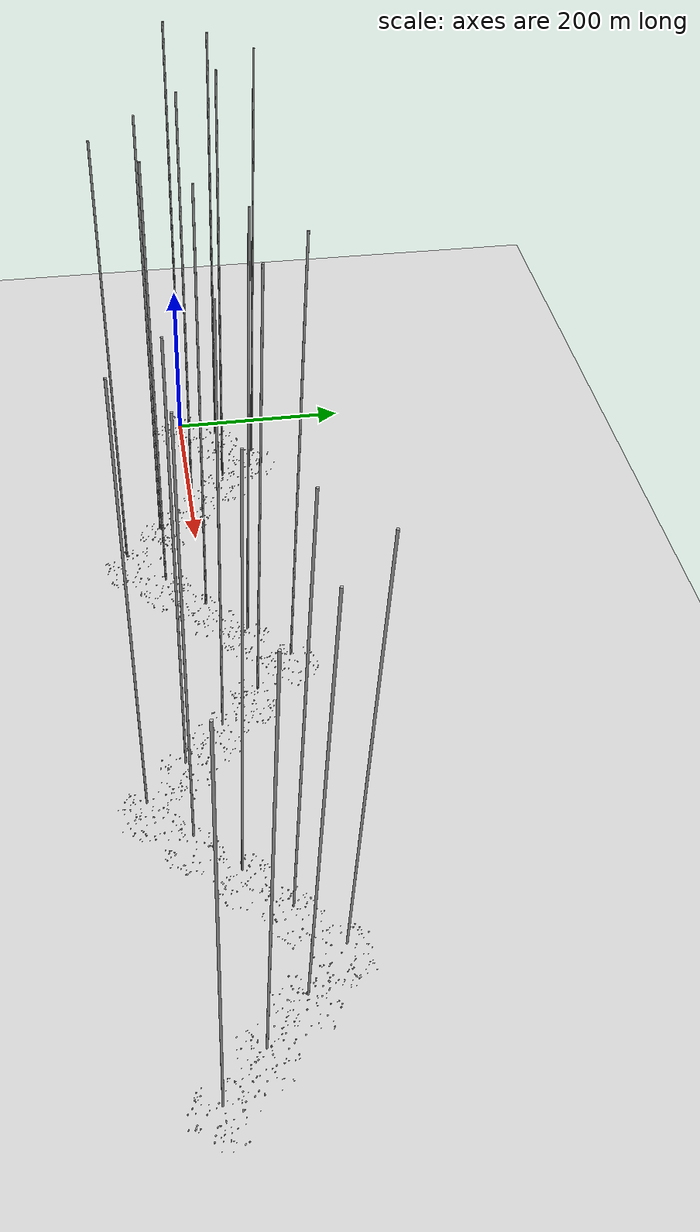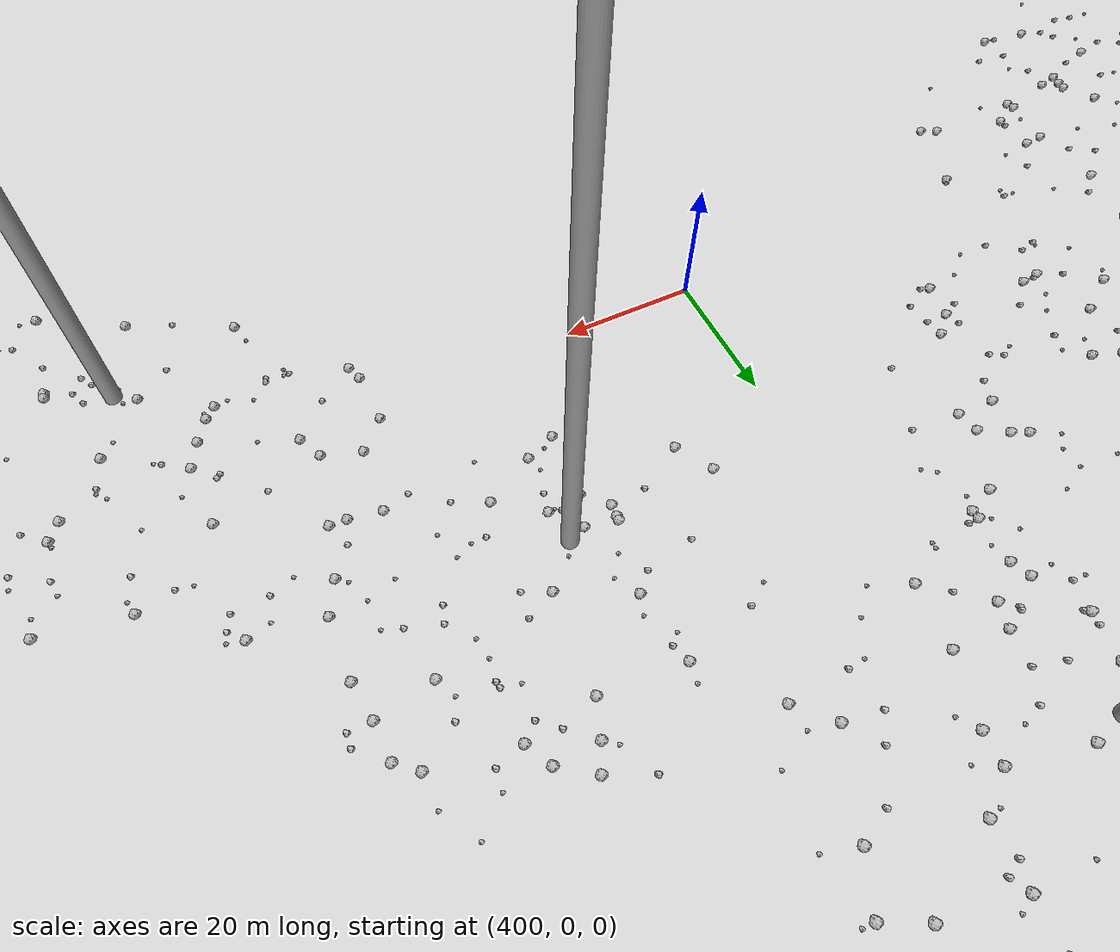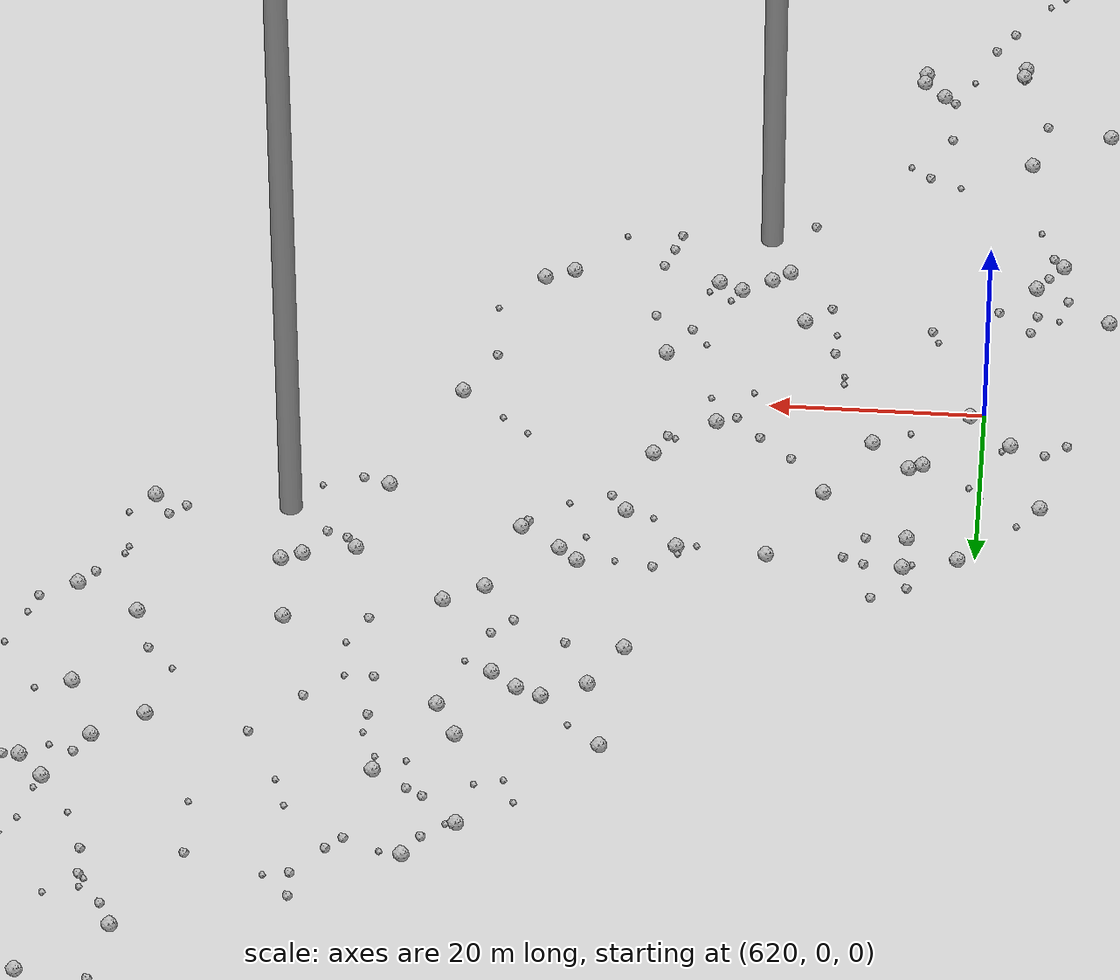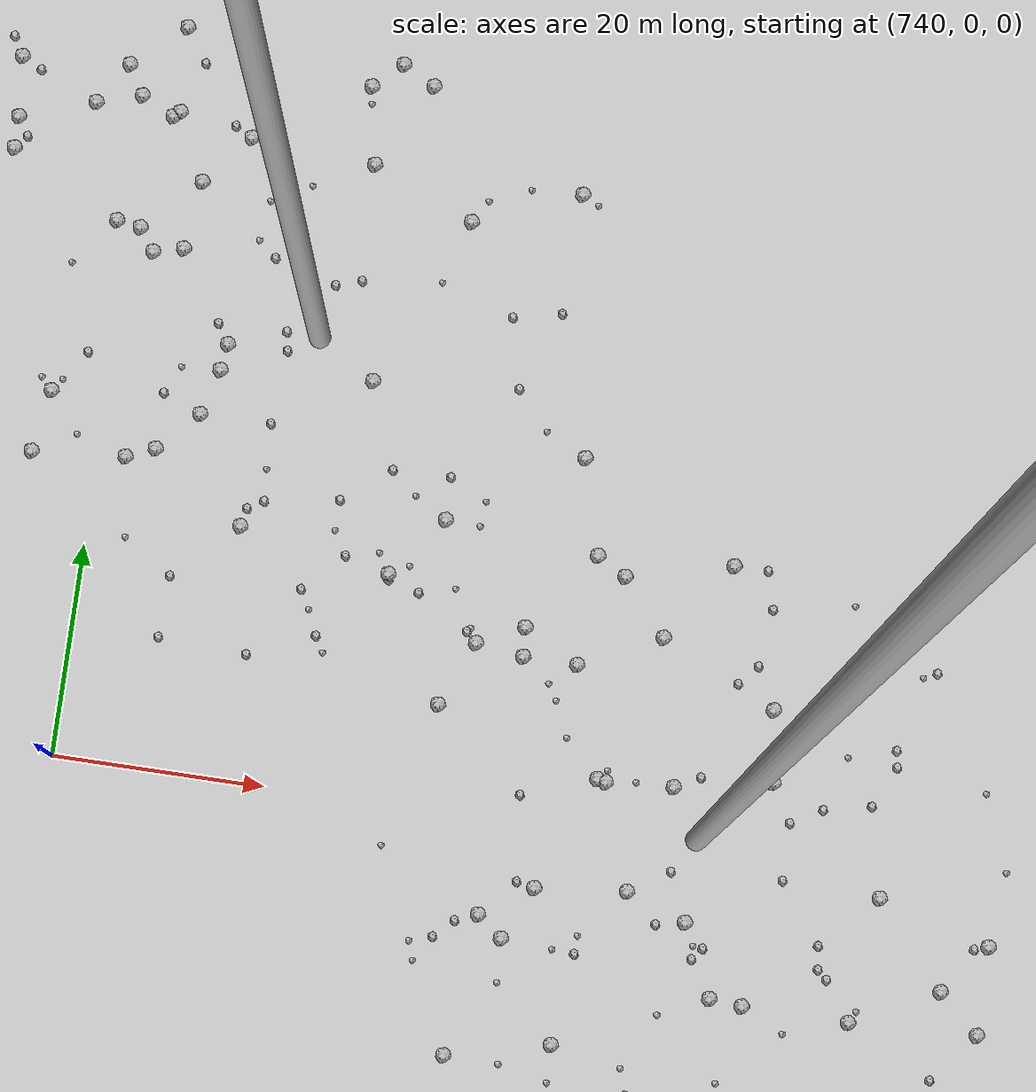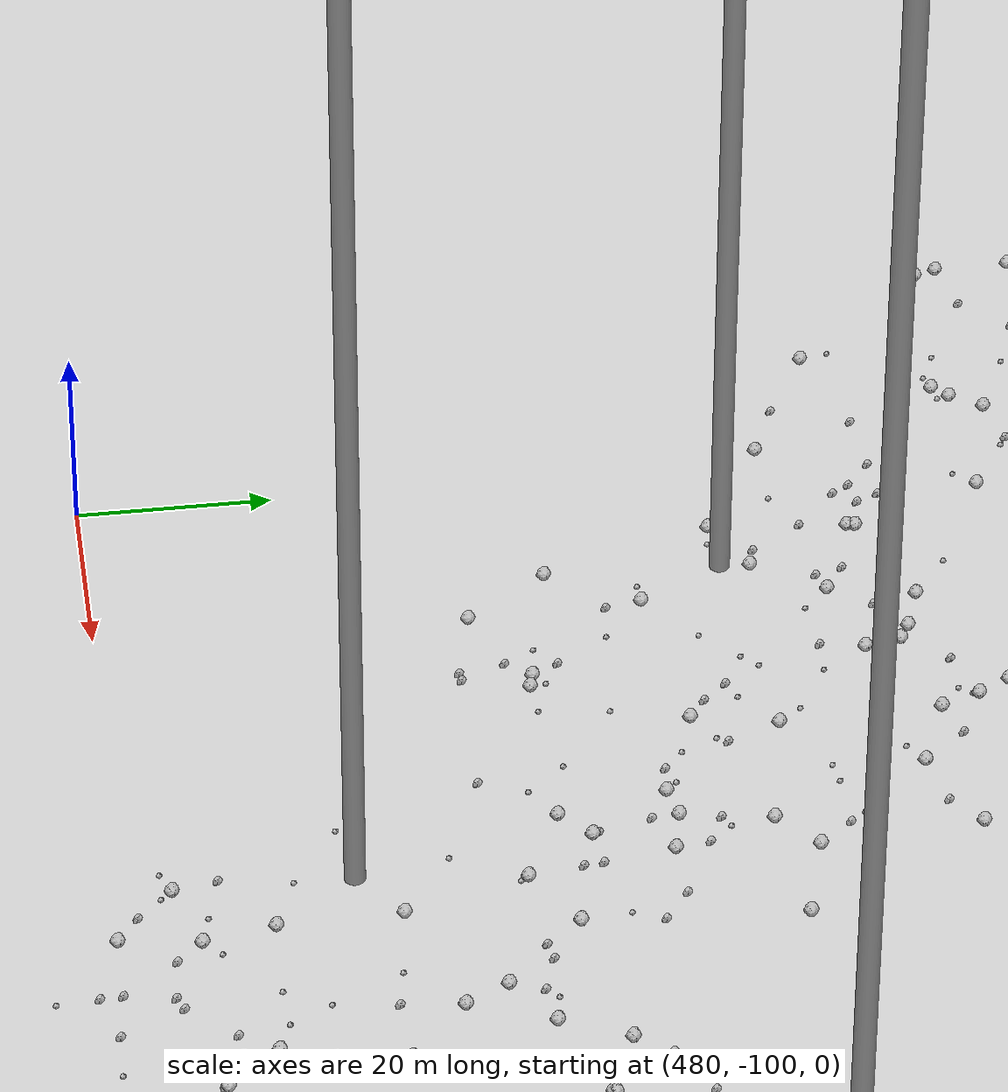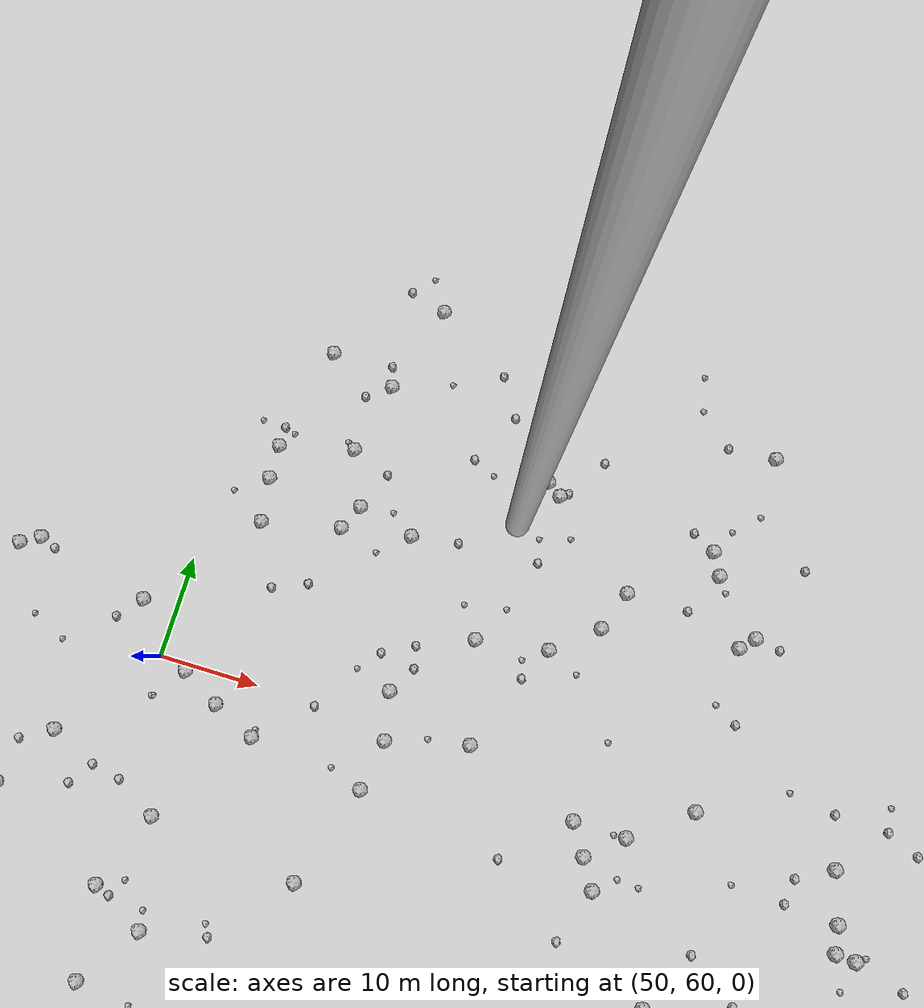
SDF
<sdf version="1.6">
 <world name="default">
  <include><uri>model://custom_ground</uri></include>
  <include><uri>model://sun</uri></include>
  <spherical_coordinates>
   <surface_model>EARTH_WGS84</surface_model>
   <latitude_deg>38.161479</latitude_deg>
   <longitude_deg>-122.454630</longitude_deg>
   <elevation>488.0</elevation>
   <heading_deg>90</heading_deg>
  </spherical_coordinates>
  <model name="rock1_0_0">
   <include><uri>model://rock1</uri><pose>-18.956871488916807 -6.428709225694224 0.5 0 0 0</pose></include>
  </model>
  <model name="rock1_0_1">
   <include><uri>model://rock1</uri><pose>-12.739056822076225 3.9244362627067773 0.5 0 0 0</pose></include>
  </model>
  <model name="rock1_0_2">
   <include><uri>model://rock1</uri><pose>-14.651029741913842 14.008849514167302 0.5 0 0 0</pose></include>
  </model>
  <model name="rock1_0_3">
   <include><uri>model://rock1</uri><pose>-17.350839913043014 -5.818428811001773 0.5 0 0 0</pose></include>
  </model>
  <model name="rock1_0_4">
   <include><uri>model://rock1</uri><pose>28.61463034515831 3.0933515747911073 0.5 0 0 0</pose></include>
  </model>
  <model name="rock1_0_5">
   <include><uri>model://rock1</uri><pose>29.07358258243754 10.011992388678479 0.5 0 0 0</pose></include>
  </model>
  <model name="rock1_0_6">
   <include><uri>model://rock1</uri><pose>8.205711523361401 -29.66538347035327 0.5 0 0 0</pose></include>
  </model>
  <model name="rock1_0_7">
   <include><uri>model://rock1</uri><pose>-10.197315172318044 12.736563768273534 0.5 0 0 0</pose></include>
  </model>
  <model name="rock1_0_8">
   <include><uri>model://rock1</uri><pose>5.076249175171839 24.956578424120515 0.5 0 0 0</pose></include>
  </model>
  <model name="rock1_0_9">
   <include><uri>model://rock1</uri><pose>6.4725363788788 -14.25711658685665 0.5 0 0 0</pose></include>
  </model>
  <model name="rock1_0_10">
   <include><uri>model://rock1</uri><pose>23.193702439122376 4.80752211604414 0.5 0 0 0</pose></include>
  </model>
  <model name="rock1_0_11">
   <include><uri>model://rock1</uri><pose>31.933968568541175 3.743928838502981 0.5 0 0 0</pose></include>
  </model>
  <model name="rock1_0_12">
   <include><uri>model://rock1</uri><pose>4.71982629203756 13.233136602800066 0.5 0 0 0</pose></include>
  </model>
  <model name="rock1_0_13">
   <include><uri>model://rock1</uri><pose>31.7997710563944 -9.89144301933701 0.5 0 0 0</pose></include>
  </model>
  <model name="rock1_0_14">
   <include><uri>model://rock1</uri><pose>12.690494936209404 -28.13307768045738 0.5 0 0 0</pose></include>
  </model>
  <model name="rock1_0_15">
   <include><uri>model://rock1</uri><pose>15.220255969352984 -24.27283025609924 0.5 0 0 0</pose></include>
  </model>
  <model name="rock1_0_16">
   <include><uri>model://rock1</uri><pose>18.006104367211314 -13.565780775570197 0.5 0 0 0</pose></include>
  </model>
  <model name="rock1_0_17">
   <include><uri>model://rock1</uri><pose>2.9504576619615044 27.12081303290688 0.5 0 0 0</pose></include>
  </model>
  <model name="rock1_0_18">
   <include><uri>model://rock1</uri><pose>26.684370083592505 -22.7862996651685 0.5 0 0 0</pose></include>
  </model>
  <model name="rock1_0_19">
   <include><uri>model://rock1</uri><pose>23.893616123760317 23.342005823988693 0.5 0 0 0</pose></include>
  </model>
  <model name="rock1_0_20">
   <include><uri>model://rock1</uri><pose>-1.9208639161137882 -22.334175429192157 0.5 0 0 0</pose></include>
  </model>
  <model name="rock1_0_21">
   <include><uri>model://rock1</uri><pose>13.563291899688544 24.863216508796846 0.5 0 0 0</pose></include>
  </model>
  <model name="rock1_0_22">
   <include><uri>model://rock1</uri><pose>36.58486282770654 1.640152870975843 0.5 0 0 0</pose></include>
  </model>
  <model name="rock1_0_23">
   <include><uri>model://rock1</uri><pose>-3.910559886144668 2.7650536570483624 0.5 0 0 0</pose></include>
  </model>
  <model name="rock1_0_24">
   <include><uri>model://rock1</uri><pose>12.279432675184466 -16.43591662336177 0.5 0 0 0</pose></include>
  </model>
  <model name="rock1_0_25">
   <include><uri>model://rock1</uri><pose>28.624722884507385 4.236336065654726 0.5 0 0 0</pose></include>
  </model>
  <model name="rock1_0_26">
   <include><uri>model://rock1</uri><pose>-10.503713354551802 6.2866988215221795 0.5 0 0 0</pose></include>
  </model>
  <model name="rock2_0_0">
   <include><uri>model://rock2</uri><pose>28.88343804604058 13.855609834512578 0.3 0 0 0</pose></include>
  </model>
  <model name="rock2_0_1">
   <include><uri>model://rock2</uri><pose>2.54162934104626 -3.8353325423018383 0.3 0 0 0</pose></include>
  </model>
  <model name="rock2_0_2">
   <include><uri>model://rock2</uri><pose>16.09632020138367 -6.612064615897516 0.3 0 0 0</pose></include>
  </model>
  <model name="rock2_0_3">
   <include><uri>model://rock2</uri><pose>-10.263136580743195 6.698756535760083 0.3 0 0 0</pose></include>
  </model>
  <model name="rock2_0_4">
   <include><uri>model://rock2</uri><pose>14.89184364164123 -9.263891733451999 0.3 0 0 0</pose></include>
  </model>
  <model name="rock2_0_5">
   <include><uri>model://rock2</uri><pose>-17.632594460740755 -2.661674428209718 0.3 0 0 0</pose></include>
  </model>
  <model name="rock2_0_6">
   <include><uri>model://rock2</uri><pose>31.586245678677457 9.656542214520641 0.3 0 0 0</pose></include>
  </model>
  <model name="rock2_0_7">
   <include><uri>model://rock2</uri><pose>-4.562963465144721 -11.529065641606334 0.3 0 0 0</pose></include>
  </model>
  <model name="rock2_0_8">
   <include><uri>model://rock2</uri><pose>11.285015316411766 -6.063052668293064 0.3 0 0 0</pose></include>
  </model>
  <model name="rock2_0_9">
   <include><uri>model://rock2</uri><pose>-12.334760793916663 -15.395534032112314 0.3 0 0 0</pose></include>
  </model>
  <model name="rock2_0_10">
   <include><uri>model://rock2</uri><pose>28.244441280824255 9.840654188680723 0.3 0 0 0</pose></include>
  </model>
  <model name="rock2_0_11">
   <include><uri>model://rock2</uri><pose>3.69449859179597 -6.6037190689728575 0.3 0 0 0</pose></include>
  </model>
  <model name="rock2_0_12">
   <include><uri>model://rock2</uri><pose>21.92123272652519 -16.36957495661587 0.3 0 0 0</pose></include>
  </model>
  <model name="rock2_0_13">
   <include><uri>model://rock2</uri><pose>2.935376198418602 4.406290444283847 0.3 0 0 0</pose></include>
  </model>
  <model name="rock2_0_14">
   <include><uri>model://rock2</uri><pose>-15.963874130123916 -5.595630352375601 0.3 0 0 0</pose></include>
  </model>
  <model name="rock2_0_15">
   <include><uri>model://rock2</uri><pose>20.527966048003677 -27.001881123970076 0.3 0 0 0</pose></include>
  </model>
  <model name="rock2_0_16">
   <include><uri>model://rock2</uri><pose>11.99645686592984 -13.036016916315997 0.3 0 0 0</pose></include>
  </model>
  <model name="rock2_0_17">
   <include><uri>model://rock2</uri><pose>-3.99903922684166 -14.332747624842867 0.3 0 0 0</pose></include>
  </model>
  <model name="rock2_0_18">
   <include><uri>model://rock2</uri><pose>2.846246576275412 -28.284096120364012 0.3 0 0 0</pose></include>
  </model>
  <model name="rock2_0_19">
   <include><uri>model://rock2</uri><pose>24.008787917906673 14.793661157309494 0.3 0 0 0</pose></include>
  </model>
  <model name="rock2_0_20">
   <include><uri>model://rock2</uri><pose>21.890216872228308 8.856240159612518 0.3 0 0 0</pose></include>
  </model>
  <model name="rock2_0_21">
   <include><uri>model://rock2</uri><pose>-4.078223687919049 -0.08104730173268848 0.3 0 0 0</pose></include>
  </model>
  <model name="rock2_0_22">
   <include><uri>model://rock2</uri><pose>18.643526739923843 -14.388556801878332 0.3 0 0 0</pose></include>
  </model>
  <model name="rock2_0_23">
   <include><uri>model://rock2</uri><pose>3.092056146760296 12.95836408187467 0.3 0 0 0</pose></include>
  </model>
  <model name="rock2_0_24">
   <include><uri>model://rock2</uri><pose>14.291389601213012 3.3978748138342354 0.3 0 0 0</pose></include>
  </model>
  <model name="rock2_0_25">
   <include><uri>model://rock2</uri><pose>5.4206761025711785 -23.263212242439337 0.3 0 0 0</pose></include>
  </model>
  <model name="rock2_0_26">
   <include><uri>model://rock2</uri><pose>20.64468690396808 7.161207256626284 0.3 0 0 0</pose></include>
  </model>
  <model name="rock3_0_0">
   <include><uri>model://rock3</uri><pose>-11.891391106129044 8.381856344635317 0.2 0 0 0</pose></include>
  </model>
  <model name="rock3_0_1">
   <include><uri>model://rock3</uri><pose>33.68153239187664 10.068843618196354 0.2 0 0 0</pose></include>
  </model>
  <model name="rock3_0_2">
   <include><uri>model://rock3</uri><pose>20.61936887816387 -8.698365923421377 0.2 0 0 0</pose></include>
  </model>
  <model name="rock3_0_3">
   <include><uri>model://rock3</uri><pose>-6.9100722871553835 12.650300579303313 0.2 0 0 0</pose></include>
  </model>
  <model name="rock3_0_4">
   <include><uri>model://rock3</uri><pose>-12.577237972975157 -10.066642130188619 0.2 0 0 0</pose></include>
  </model>
  <model name="rock3_0_5">
   <include><uri>model://rock3</uri><pose>0.15678388640674967 -20.074685645094082 0.2 0 0 0</pose></include>
  </model>
  <model name="rock3_0_6">
   <include><uri>model://rock3</uri><pose>20.456097044789132 -25.00657634844815 0.2 0 0 0</pose></include>
  </model>
  <model name="rock3_0_7">
   <include><uri>model://rock3</uri><pose>38.132963039470624 -6.202023026684316 0.2 0 0 0</pose></include>
  </model>
  <model name="rock3_0_8">
   <include><uri>model://rock3</uri><pose>35.82173171809267 7.785353042191517 0.2 0 0 0</pose></include>
  </model>
  <model name="rock3_0_9">
   <include><uri>model://rock3</uri><pose>-14.460741840449241 -3.1412369539345804 0.2 0 0 0</pose></include>
  </model>
  <model name="rock3_0_10">
   <include><uri>model://rock3</uri><pose>37.89504726284824 -5.452723577369532 0.2 0 0 0</pose></include>
  </model>
  <model name="rock3_0_11">
   <include><uri>model://rock3</uri><pose>4.75525504929044 -3.6552389493681154 0.2 0 0 0</pose></include>
  </model>
  <model name="rock3_0_12">
   <include><uri>model://rock3</uri><pose>7.569069963191335 15.902536563494877 0.2 0 0 0</pose></include>
  </model>
  <model name="rock3_0_13">
   <include><uri>model://rock3</uri><pose>-0.07861436020671775 -22.468328931335826 0.2 0 0 0</pose></include>
  </model>
  <model name="rock3_0_14">
   <include><uri>model://rock3</uri><pose>-2.0939083159852743 -18.041694639671483 0.2 0 0 0</pose></include>
  </model>
  <model name="rock3_0_15">
   <include><uri>model://rock3</uri><pose>12.455629643775673 -22.003191332446193 0.2 0 0 0</pose></include>
  </model>
  <model name="rock3_0_16">
   <include><uri>model://rock3</uri><pose>32.53082877084978 -1.332274321834955 0.2 0 0 0</pose></include>
  </model>
  <model name="rock3_0_17">
   <include><uri>model://rock3</uri><pose>0.25450758212622304 24.229059401153343 0.2 0 0 0</pose></include>
  </model>
  <model name="rock3_0_18">
   <include><uri>model://rock3</uri><pose>17.330551811752002 6.5645366367623765 0.2 0 0 0</pose></include>
  </model>
  <model name="rock3_0_19">
   <include><uri>model://rock3</uri><pose>25.24980484381348 7.654904622980936 0.2 0 0 0</pose></include>
  </model>
  <model name="rock3_0_20">
   <include><uri>model://rock3</uri><pose>0.024779961139167028 -4.789581462580244 0.2 0 0 0</pose></include>
  </model>
  <model name="rock3_0_21">
   <include><uri>model://rock3</uri><pose>0.6681404860239617 -3.712299256910775 0.2 0 0 0</pose></include>
  </model>
  <model name="rock3_0_22">
   <include><uri>model://rock3</uri><pose>33.01206699239077 -19.009920250351847 0.2 0 0 0</pose></include>
  </model>
  <model name="rock3_0_23">
   <include><uri>model://rock3</uri><pose>6.524598534855421 24.228232491315524 0.2 0 0 0</pose></include>
  </model>
  <model name="rock3_0_24">
   <include><uri>model://rock3</uri><pose>-17.061484822752096 -8.877217981348906 0.2 0 0 0</pose></include>
  </model>
  <model name="rock3_0_25">
   <include><uri>model://rock3</uri><pose>25.507907185173828 -1.9197879225624845 0.2 0 0 0</pose></include>
  </model>
  <model name="rock3_0_26">
   <include><uri>model://rock3</uri><pose>34.57359456641042 -10.068138089009771 0.2 0 0 0</pose></include>
  </model>
  <model name="rock1_1_0">
   <include><uri>model://rock1</uri><pose>42.502467689036294 50.56300290334303 0.5 0 0 0</pose></include>
  </model>
  <model name="rock1_1_1">
   <include><uri>model://rock1</uri><pose>63.577824065113816 21.638828864947488 0.5 0 0 0</pose></include>
  </model>
  <model name="rock1_1_2">
   <include><uri>model://rock1</uri><pose>56.523568759461014 35.34010824467116 0.5 0 0 0</pose></include>
  </model>
  <model name="rock1_1_3">
   <include><uri>model://rock1</uri><pose>46.64871997060225 64.86707866760193 0.5 0 0 0</pose></include>
  </model>
  <model name="rock1_1_4">
   <include><uri>model://rock1</uri><pose>36.906018236365895 36.789547636707255 0.5 0 0 0</pose></include>
  </model>
  <model name="rock1_1_5">
   <include><uri>model://rock1</uri><pose>28.635351698832164 25.990836122009053 0.5 0 0 0</pose></include>
  </model>
  <model name="rock1_1_6">
   <include><uri>model://rock1</uri><pose>52.11716248105149 18.263085889703373 0.5 0 0 0</pose></include>
  </model>
  <model name="rock1_1_7">
   <include><uri>model://rock1</uri><pose>32.91153708411678 66.74262276831493 0.5 0 0 0</pose></include>
  </model>
  <model name="rock1_1_8">
   <include><uri>model://rock1</uri><pose>34.809030384995545 67.85187743925371 0.5 0 0 0</pose></include>
  </model>
  <model name="rock1_1_9">
   <include><uri>model://rock1</uri><pose>11.188486839088618 32.73352677110623 0.5 0 0 0</pose></include>
  </model>
  <model name="rock1_1_10">
   <include><uri>model://rock1</uri><pose>14.210997977145459 44.976645628860226 0.5 0 0 0</pose></include>
  </model>
  <model name="rock1_1_11">
   <include><uri>model://rock1</uri><pose>38.768284528869415 43.39193614572736 0.5 0 0 0</pose></include>
  </model>
  <model name="rock1_1_12">
   <include><uri>model://rock1</uri><pose>27.31650235196469 59.08399723240683 0.5 0 0 0</pose></include>
  </model>
  <model name="rock1_1_13">
   <include><uri>model://rock1</uri><pose>22.813883640643777 47.49321501560166 0.5 0 0 0</pose></include>
  </model>
  <model name="rock1_1_14">
   <include><uri>model://rock1</uri><pose>38.80563707294223 44.34766811605486 0.5 0 0 0</pose></include>
  </model>
  <model name="rock1_1_15">
   <include><uri>model://rock1</uri><pose>69.20145464576018 43.57977911747913 0.5 0 0 0</pose></include>
  </model>
  <model name="rock1_1_16">
   <include><uri>model://rock1</uri><pose>36.948997872697845 42.9030204103659 0.5 0 0 0</pose></include>
  </model>
  <model name="rock1_1_17">
   <include><uri>model://rock1</uri><pose>51.20888395027135 38.124757794565994 0.5 0 0 0</pose></include>
  </model>
  <model name="rock1_1_18">
   <include><uri>model://rock1</uri><pose>52.88718099242268 59.4018894972663 0.5 0 0 0</pose></include>
  </model>
  <model name="rock1_1_19">
   <include><uri>model://rock1</uri><pose>52.36948215573501 29.51367770622189 0.5 0 0 0</pose></include>
  </model>
  <model name="rock1_1_20">
   <include><uri>model://rock1</uri><pose>17.53897481344027 52.68778790957202 0.5 0 0 0</pose></include>
  </model>
  <model name="rock1_1_21">
   <include><uri>model://rock1</uri><pose>63.75878157970259 29.239010387231588 0.5 0 0 0</pose></include>
  </model>
  <model name="rock1_1_22">
   <include><uri>model://rock1</uri><pose>61.07967631709499 55.219532524626366 0.5 0 0 0</pose></include>
  </model>
  <model name="rock1_1_23">
   <include><uri>model://rock1</uri><pose>26.909062587250858 17.700964632144974 0.5 0 0 0</pose></include>
  </model>
  <model name="rock1_1_24">
   <include><uri>model://rock1</uri><pose>54.214301717124265 45.53071445625216 0.5 0 0 0</pose></include>
  </model>
  <model name="rock1_1_25">
   <include><uri>model://rock1</uri><pose>56.77320542489969 57.197782942821014 0.5 0 0 0</pose></include>
  </model>
  <model name="rock1_1_26">
   <include><uri>model://rock1</uri><pose>18.679745943755954 36.55677895807608 0.5 0 0 0</pose></include>
  </model>
  <model name="rock2_1_0">
   <include><uri>model://rock2</uri><pose>26.542955585440087 41.01518477177575 0.3 0 0 0</pose></include>
  </model>
  <model name="rock2_1_1">
   <include><uri>model://rock2</uri><pose>47.08667864350948 48.4665264389857 0.3 0 0 0</pose></include>
  </model>
  <model name="rock2_1_2">
   <include><uri>model://rock2</uri><pose>36.38149684558194 67.13594280744567 0.3 0 0 0</pose></include>
  </model>
  <model name="rock2_1_3">
   <include><uri>model://rock2</uri><pose>66.37467401271083 32.73900500006306 0.3 0 0 0</pose></include>
  </model>
  <model name="rock2_1_4">
   <include><uri>model://rock2</uri><pose>27.084477032637935 22.2189172386021 0.3 0 0 0</pose></include>
  </model>
  <model name="rock2_1_5">
   <include><uri>model://rock2</uri><pose>56.053147973302224 20.494622963477212 0.3 0 0 0</pose></include>
  </model>
  <model name="rock2_1_6">
   <include><uri>model://rock2</uri><pose>16.425740219465176 35.39949400708331 0.3 0 0 0</pose></include>
  </model>
  <model name="rock2_1_7">
   <include><uri>model://rock2</uri><pose>24.49899728160835 60.07602565884696 0.3 0 0 0</pose></include>
  </model>
  <model name="rock2_1_8">
   <include><uri>model://rock2</uri><pose>36.35037650711798 26.158840857853612 0.3 0 0 0</pose></include>
  </model>
  <model name="rock2_1_9">
   <include><uri>model://rock2</uri><pose>38.71969588141459 22.78295769729807 0.3 0 0 0</pose></include>
  </model>
  <model name="rock2_1_10">
   <include><uri>model://rock2</uri><pose>50.018252367654284 47.84630969158592 0.3 0 0 0</pose></include>
  </model>
  <model name="rock2_1_11">
   <include><uri>model://rock2</uri><pose>26.046965754198244 29.175761646832743 0.3 0 0 0</pose></include>
  </model>
  <model name="rock2_1_12">
   <include><uri>model://rock2</uri><pose>20.126224242281747 41.03281843824098 0.3 0 0 0</pose></include>
  </model>
  <model name="rock2_1_13">
   <include><uri>model://rock2</uri><pose>52.633939767576834 37.50948416981202 0.3 0 0 0</pose></include>
  </model>
  <model name="rock2_1_14">
   <include><uri>model://rock2</uri><pose>44.55288502374774 62.531361020329925 0.3 0 0 0</pose></include>
  </model>
  <model name="rock2_1_15">
   <include><uri>model://rock2</uri><pose>18.269587187515235 46.22146635733663 0.3 0 0 0</pose></include>
  </model>
  <model name="rock2_1_16">
   <include><uri>model://rock2</uri><pose>31.819223821056685 56.77343118519055 0.3 0 0 0</pose></include>
  </model>
  <model name="rock2_1_17">
   <include><uri>model://rock2</uri><pose>27.83692668264911 52.3354752571196 0.3 0 0 0</pose></include>
  </model>
  <model name="rock2_1_18">
   <include><uri>model://rock2</uri><pose>37.178665908695365 44.01247471648336 0.3 0 0 0</pose></include>
  </model>
  <model name="rock2_1_19">
   <include><uri>model://rock2</uri><pose>65.71991263972231 27.544337708873364 0.3 0 0 0</pose></include>
  </model>
  <model name="rock2_1_20">
   <include><uri>model://rock2</uri><pose>62.842461461205126 36.575310065145096 0.3 0 0 0</pose></include>
  </model>
  <model name="rock2_1_21">
   <include><uri>model://rock2</uri><pose>53.284247020507735 22.129413173937415 0.3 0 0 0</pose></include>
  </model>
  <model name="rock2_1_22">
   <include><uri>model://rock2</uri><pose>39.384390983140584 48.79319195932236 0.3 0 0 0</pose></include>
  </model>
  <model name="rock2_1_23">
   <include><uri>model://rock2</uri><pose>43.35640994215232 18.364338434183516 0.3 0 0 0</pose></include>
  </model>
  <model name="rock2_1_24">
   <include><uri>model://rock2</uri><pose>45.429557841537935 46.17721923394457 0.3 0 0 0</pose></include>
  </model>
  <model name="rock2_1_25">
   <include><uri>model://rock2</uri><pose>20.330848137029257 60.46991276989942 0.3 0 0 0</pose></include>
  </model>
  <model name="rock2_1_26">
   <include><uri>model://rock2</uri><pose>26.452204592461673 15.305502643302042 0.3 0 0 0</pose></include>
  </model>
  <model name="rock3_1_0">
   <include><uri>model://rock3</uri><pose>44.10648978415724 22.32219207596927 0.2 0 0 0</pose></include>
  </model>
  <model name="rock3_1_1">
   <include><uri>model://rock3</uri><pose>35.631086935783685 43.927962127166715 0.2 0 0 0</pose></include>
  </model>
  <model name="rock3_1_2">
   <include><uri>model://rock3</uri><pose>56.16395148059744 37.08012051568119 0.2 0 0 0</pose></include>
  </model>
  <model name="rock3_1_3">
   <include><uri>model://rock3</uri><pose>14.088409407635003 45.52465238778695 0.2 0 0 0</pose></include>
  </model>
  <model name="rock3_1_4">
   <include><uri>model://rock3</uri><pose>62.526197581231195 28.329045757598344 0.2 0 0 0</pose></include>
  </model>
  <model name="rock3_1_5">
   <include><uri>model://rock3</uri><pose>53.634117261415106 39.19839136625892 0.2 0 0 0</pose></include>
  </model>
  <model name="rock3_1_6">
   <include><uri>model://rock3</uri><pose>16.297750793317178 27.13843074051925 0.2 0 0 0</pose></include>
  </model>
  <model name="rock3_1_7">
   <include><uri>model://rock3</uri><pose>25.793503103824786 54.90183750425457 0.2 0 0 0</pose></include>
  </model>
  <model name="rock3_1_8">
   <include><uri>model://rock3</uri><pose>29.08006351053902 67.69557270389609 0.2 0 0 0</pose></include>
  </model>
  <model name="rock3_1_9">
   <include><uri>model://rock3</uri><pose>25.943599995157847 26.8367209028765 0.2 0 0 0</pose></include>
  </model>
  <model name="rock3_1_10">
   <include><uri>model://rock3</uri><pose>40.136373002788496 58.894227869343126 0.2 0 0 0</pose></include>
  </model>
  <model name="rock3_1_11">
   <include><uri>model://rock3</uri><pose>61.165189059769304 55.927639784625434 0.2 0 0 0</pose></include>
  </model>
  <model name="rock3_1_12">
   <include><uri>model://rock3</uri><pose>36.344766367863556 39.75904629268899 0.2 0 0 0</pose></include>
  </model>
  <model name="rock3_1_13">
   <include><uri>model://rock3</uri><pose>14.887835336353422 25.051338371781988 0.2 0 0 0</pose></include>
  </model>
  <model name="rock3_1_14">
   <include><uri>model://rock3</uri><pose>50.35466519786309 56.18131108710829 0.2 0 0 0</pose></include>
  </model>
  <model name="rock3_1_15">
   <include><uri>model://rock3</uri><pose>32.37707741126448 50.24414975403455 0.2 0 0 0</pose></include>
  </model>
  <model name="rock3_1_16">
   <include><uri>model://rock3</uri><pose>20.52891853719771 44.485757445374546 0.2 0 0 0</pose></include>
  </model>
  <model name="rock3_1_17">
   <include><uri>model://rock3</uri><pose>50.5151957911636 56.2485895794595 0.2 0 0 0</pose></include>
  </model>
  <model name="rock3_1_18">
   <include><uri>model://rock3</uri><pose>57.64086037047229 28.71462900303027 0.2 0 0 0</pose></include>
  </model>
  <model name="rock3_1_19">
   <include><uri>model://rock3</uri><pose>62.25445064886427 37.62285036848833 0.2 0 0 0</pose></include>
  </model>
  <model name="rock3_1_20">
   <include><uri>model://rock3</uri><pose>22.402754933935018 57.988584286976995 0.2 0 0 0</pose></include>
  </model>
  <model name="rock3_1_21">
   <include><uri>model://rock3</uri><pose>22.34042724332252 59.64709598971986 0.2 0 0 0</pose></include>
  </model>
  <model name="rock3_1_22">
   <include><uri>model://rock3</uri><pose>68.94783074868045 34.81748284832423 0.2 0 0 0</pose></include>
  </model>
  <model name="rock3_1_23">
   <include><uri>model://rock3</uri><pose>11.968861822032961 35.731978530195306 0.2 0 0 0</pose></include>
  </model>
  <model name="rock3_1_24">
   <include><uri>model://rock3</uri><pose>36.67881218420813 60.477169499571055 0.2 0 0 0</pose></include>
  </model>
  <model name="rock3_1_25">
   <include><uri>model://rock3</uri><pose>40.629530270354365 11.36092953735226 0.2 0 0 0</pose></include>
  </model>
  <model name="rock3_1_26">
   <include><uri>model://rock3</uri><pose>50.17455513150347 17.008279499949666 0.2 0 0 0</pose></include>
  </model>
  <model name="rock1_2_0">
   <include><uri>model://rock1</uri><pose>98.40255013161104 56.41421812177321 0.5 0 0 0</pose></include>
  </model>
  <model name="rock1_2_1">
   <include><uri>model://rock1</uri><pose>63.30172969187814 77.15547212934591 0.5 0 0 0</pose></include>
  </model>
  <model name="rock1_2_2">
   <include><uri>model://rock1</uri><pose>55.409080244091086 75.50233697646948 0.5 0 0 0</pose></include>
  </model>
  <model name="rock1_2_3">
   <include><uri>model://rock1</uri><pose>82.00379299643501 87.44837343118925 0.5 0 0 0</pose></include>
  </model>
  <model name="rock1_2_4">
   <include><uri>model://rock1</uri><pose>72.67283423733504 63.186681053574404 0.5 0 0 0</pose></include>
  </model>
  <model name="rock1_2_5">
   <include><uri>model://rock1</uri><pose>104.44767991039257 76.83942438085964 0.5 0 0 0</pose></include>
  </model>
  <model name="rock1_2_6">
   <include><uri>model://rock1</uri><pose>72.67994112577912 53.50280529855154 0.5 0 0 0</pose></include>
  </model>
  <model name="rock1_2_7">
   <include><uri>model://rock1</uri><pose>105.80098034985073 78.17578460376077 0.5 0 0 0</pose></include>
  </model>
  <model name="rock1_2_8">
   <include><uri>model://rock1</uri><pose>90.93922675466092 74.86736239607293 0.5 0 0 0</pose></include>
  </model>
  <model name="rock1_2_9">
   <include><uri>model://rock1</uri><pose>64.52766352011616 79.72815351633957 0.5 0 0 0</pose></include>
  </model>
  <model name="rock1_2_10">
   <include><uri>model://rock1</uri><pose>93.14526856578209 56.48401093928719 0.5 0 0 0</pose></include>
  </model>
  <model name="rock1_2_11">
   <include><uri>model://rock1</uri><pose>63.931124470765624 92.47076771108802 0.5 0 0 0</pose></include>
  </model>
  <model name="rock1_2_12">
   <include><uri>model://rock1</uri><pose>57.154429510232475 94.17625759828496 0.5 0 0 0</pose></include>
  </model>
  <model name="rock1_2_13">
   <include><uri>model://rock1</uri><pose>100.87554103300054 83.15119645825145 0.5 0 0 0</pose></include>
  </model>
  <model name="rock1_2_14">
   <include><uri>model://rock1</uri><pose>83.47875371274705 86.4337080510469 0.5 0 0 0</pose></include>
  </model>
  <model name="rock1_2_15">
   <include><uri>model://rock1</uri><pose>81.66161261513928 60.49402102815899 0.5 0 0 0</pose></include>
  </model>
  <model name="rock1_2_16">
   <include><uri>model://rock1</uri><pose>79.31264547239523 70.31848073506984 0.5 0 0 0</pose></include>
  </model>
  <model name="rock1_2_17">
   <include><uri>model://rock1</uri><pose>92.50129871608745 78.92393006547493 0.5 0 0 0</pose></include>
  </model>
  <model name="rock1_2_18">
   <include><uri>model://rock1</uri><pose>70.29484327642358 78.32885203446423 0.5 0 0 0</pose></include>
  </model>
  <model name="rock1_2_19">
   <include><uri>model://rock1</uri><pose>54.82025495739681 79.95108302136919 0.5 0 0 0</pose></include>
  </model>
  <model name="rock1_2_20">
   <include><uri>model://rock1</uri><pose>103.48127852566253 96.23112476648342 0.5 0 0 0</pose></include>
  </model>
  <model name="rock1_2_21">
   <include><uri>model://rock1</uri><pose>99.73273412802718 85.35485273850769 0.5 0 0 0</pose></include>
  </model>
  <model name="rock1_2_22">
   <include><uri>model://rock1</uri><pose>54.753356614592015 83.37543048791926 0.5 0 0 0</pose></include>
  </model>
  <model name="rock1_2_23">
   <include><uri>model://rock1</uri><pose>66.80997482771006 101.59166278385877 0.5 0 0 0</pose></include>
  </model>
  <model name="rock1_2_24">
   <include><uri>model://rock1</uri><pose>62.206255775170746 85.13449727304445 0.5 0 0 0</pose></include>
  </model>
  <model name="rock1_2_25">
   <include><uri>model://rock1</uri><pose>86.53328011018486 71.39744376820066 0.5 0 0 0</pose></include>
  </model>
  <model name="rock1_2_26">
   <include><uri>model://rock1</uri><pose>73.58176416409879 58.52561905609012 0.5 0 0 0</pose></include>
  </model>
  <model name="rock2_2_0">
   <include><uri>model://rock2</uri><pose>84.70210215353977 67.96494974590661 0.3 0 0 0</pose></include>
  </model>
  <model name="rock2_2_1">
   <include><uri>model://rock2</uri><pose>108.95799038090706 86.03748165238565 0.3 0 0 0</pose></include>
  </model>
  <model name="rock2_2_2">
   <include><uri>model://rock2</uri><pose>63.336303389765604 94.5158646965063 0.3 0 0 0</pose></include>
  </model>
  <model name="rock2_2_3">
   <include><uri>model://rock2</uri><pose>76.98924771682425 92.86952695583071 0.3 0 0 0</pose></include>
  </model>
  <model name="rock2_2_4">
   <include><uri>model://rock2</uri><pose>84.25404612615476 86.91410442930436 0.3 0 0 0</pose></include>
  </model>
  <model name="rock2_2_5">
   <include><uri>model://rock2</uri><pose>61.59923711012072 90.73845175131665 0.3 0 0 0</pose></include>
  </model>
  <model name="rock2_2_6">
   <include><uri>model://rock2</uri><pose>58.403918165201674 69.53268223754822 0.3 0 0 0</pose></include>
  </model>
  <model name="rock2_2_7">
   <include><uri>model://rock2</uri><pose>66.1753260872229 83.5931523190613 0.3 0 0 0</pose></include>
  </model>
  <model name="rock2_2_8">
   <include><uri>model://rock2</uri><pose>61.80379162923785 70.90464182676843 0.3 0 0 0</pose></include>
  </model>
  <model name="rock2_2_9">
   <include><uri>model://rock2</uri><pose>83.15713191116188 79.29788736380566 0.3 0 0 0</pose></include>
  </model>
  <model name="rock2_2_10">
   <include><uri>model://rock2</uri><pose>54.73350178857572 85.37435940967956 0.3 0 0 0</pose></include>
  </model>
  <model name="rock2_2_11">
   <include><uri>model://rock2</uri><pose>87.17656906061725 51.07570384775861 0.3 0 0 0</pose></include>
  </model>
  <model name="rock2_2_12">
   <include><uri>model://rock2</uri><pose>63.00127867406542 102.75293428161913 0.3 0 0 0</pose></include>
  </model>
  <model name="rock2_2_13">
   <include><uri>model://rock2</uri><pose>108.37324184193508 77.72721152419933 0.3 0 0 0</pose></include>
  </model>
  <model name="rock2_2_14">
   <include><uri>model://rock2</uri><pose>86.9564373574694 90.94311195711308 0.3 0 0 0</pose></include>
  </model>
  <model name="rock2_2_15">
   <include><uri>model://rock2</uri><pose>97.41645133407803 86.60580944261537 0.3 0 0 0</pose></include>
  </model>
  <model name="rock2_2_16">
   <include><uri>model://rock2</uri><pose>66.03089007543831 59.73925605381147 0.3 0 0 0</pose></include>
  </model>
  <model name="rock2_2_17">
   <include><uri>model://rock2</uri><pose>74.30303602719597 65.90081769899973 0.3 0 0 0</pose></include>
  </model>
  <model name="rock2_2_18">
   <include><uri>model://rock2</uri><pose>74.18302135708684 87.60930816495667 0.3 0 0 0</pose></include>
  </model>
  <model name="rock2_2_19">
   <include><uri>model://rock2</uri><pose>82.18161847618936 108.29416068102623 0.3 0 0 0</pose></include>
  </model>
  <model name="rock2_2_20">
   <include><uri>model://rock2</uri><pose>74.64249018600282 96.75195293542947 0.3 0 0 0</pose></include>
  </model>
  <model name="rock2_2_21">
   <include><uri>model://rock2</uri><pose>70.76279674170418 66.47610993242449 0.3 0 0 0</pose></include>
  </model>
  <model name="rock2_2_22">
   <include><uri>model://rock2</uri><pose>73.8592717520055 68.07453058398637 0.3 0 0 0</pose></include>
  </model>
  <model name="rock2_2_23">
   <include><uri>model://rock2</uri><pose>105.90932042507275 69.55597845854025 0.3 0 0 0</pose></include>
  </model>
  <model name="rock2_2_24">
   <include><uri>model://rock2</uri><pose>98.72272350587792 78.91185479327 0.3 0 0 0</pose></include>
  </model>
  <model name="rock2_2_25">
   <include><uri>model://rock2</uri><pose>98.6216004891059 95.94262955973724 0.3 0 0 0</pose></include>
  </model>
  <model name="rock2_2_26">
   <include><uri>model://rock2</uri><pose>75.00862126866801 78.96833688802924 0.3 0 0 0</pose></include>
  </model>
  <model name="rock3_2_0">
   <include><uri>model://rock3</uri><pose>77.26516220807409 73.2768181188178 0.2 0 0 0</pose></include>
  </model>
  <model name="rock3_2_1">
   <include><uri>model://rock3</uri><pose>55.195298697999746 79.98464446363181 0.2 0 0 0</pose></include>
  </model>
  <model name="rock3_2_2">
   <include><uri>model://rock3</uri><pose>77.52841627007628 59.8212233925599 0.2 0 0 0</pose></include>
  </model>
  <model name="rock3_2_3">
   <include><uri>model://rock3</uri><pose>67.32597835244356 75.75369942266349 0.2 0 0 0</pose></include>
  </model>
  <model name="rock3_2_4">
   <include><uri>model://rock3</uri><pose>67.85968367617892 80.04781389065485 0.2 0 0 0</pose></include>
  </model>
  <model name="rock3_2_5">
   <include><uri>model://rock3</uri><pose>94.45756625530444 102.48224135256459 0.2 0 0 0</pose></include>
  </model>
  <model name="rock3_2_6">
   <include><uri>model://rock3</uri><pose>89.75894345663306 69.82695780189917 0.2 0 0 0</pose></include>
  </model>
  <model name="rock3_2_7">
   <include><uri>model://rock3</uri><pose>82.65872445716803 81.63083501154304 0.2 0 0 0</pose></include>
  </model>
  <model name="rock3_2_8">
   <include><uri>model://rock3</uri><pose>84.23143649852577 69.68294548815805 0.2 0 0 0</pose></include>
  </model>
  <model name="rock3_2_9">
   <include><uri>model://rock3</uri><pose>85.68509023937054 82.52039730486639 0.2 0 0 0</pose></include>
  </model>
  <model name="rock3_2_10">
   <include><uri>model://rock3</uri><pose>69.33539598920524 54.6178870727457 0.2 0 0 0</pose></include>
  </model>
  <model name="rock3_2_11">
   <include><uri>model://rock3</uri><pose>103.43505354364306 90.0108523624665 0.2 0 0 0</pose></include>
  </model>
  <model name="rock3_2_12">
   <include><uri>model://rock3</uri><pose>82.63579185622282 95.60292456914158 0.2 0 0 0</pose></include>
  </model>
  <model name="rock3_2_13">
   <include><uri>model://rock3</uri><pose>64.8702733091398 104.72647040727324 0.2 0 0 0</pose></include>
  </model>
  <model name="rock3_2_14">
   <include><uri>model://rock3</uri><pose>95.2475233472413 98.9866903000664 0.2 0 0 0</pose></include>
  </model>
  <model name="rock3_2_15">
   <include><uri>model://rock3</uri><pose>76.48604515787056 86.51326085255303 0.2 0 0 0</pose></include>
  </model>
  <model name="rock3_2_16">
   <include><uri>model://rock3</uri><pose>51.72409910225986 77.75446347792538 0.2 0 0 0</pose></include>
  </model>
  <model name="rock3_2_17">
   <include><uri>model://rock3</uri><pose>101.88219035154573 81.68261295851303 0.2 0 0 0</pose></include>
  </model>
  <model name="rock3_2_18">
   <include><uri>model://rock3</uri><pose>52.32834453452346 85.45870408308284 0.2 0 0 0</pose></include>
  </model>
  <model name="rock3_2_19">
   <include><uri>model://rock3</uri><pose>101.06114513200895 87.78463732080277 0.2 0 0 0</pose></include>
  </model>
  <model name="rock3_2_20">
   <include><uri>model://rock3</uri><pose>55.80494294169427 84.97162476805693 0.2 0 0 0</pose></include>
  </model>
  <model name="rock3_2_21">
   <include><uri>model://rock3</uri><pose>94.43032922345057 64.43962978247428 0.2 0 0 0</pose></include>
  </model>
  <model name="rock3_2_22">
   <include><uri>model://rock3</uri><pose>103.60329165092307 70.86947742673274 0.2 0 0 0</pose></include>
  </model>
  <model name="rock3_2_23">
   <include><uri>model://rock3</uri><pose>69.86213297775244 94.42599267060226 0.2 0 0 0</pose></include>
  </model>
  <model name="rock3_2_24">
   <include><uri>model://rock3</uri><pose>68.91712017614383 64.35231893775854 0.2 0 0 0</pose></include>
  </model>
  <model name="rock3_2_25">
   <include><uri>model://rock3</uri><pose>61.325569888570925 85.69172630242151 0.2 0 0 0</pose></include>
  </model>
  <model name="rock3_2_26">
   <include><uri>model://rock3</uri><pose>81.4427899003303 73.99266182547105 0.2 0 0 0</pose></include>
  </model>
  <model name="rock1_3_0">
   <include><uri>model://rock1</uri><pose>133.92857515808177 19.075478648117002 0.5 0 0 0</pose></include>
  </model>
  <model name="rock1_3_1">
   <include><uri>model://rock1</uri><pose>125.17531010756906 14.412286218828086 0.5 0 0 0</pose></include>
  </model>
  <model name="rock1_3_2">
   <include><uri>model://rock1</uri><pose>136.89786524673337 41.76574020554433 0.5 0 0 0</pose></include>
  </model>
  <model name="rock1_3_3">
   <include><uri>model://rock1</uri><pose>121.93667813830248 51.71974136587883 0.5 0 0 0</pose></include>
  </model>
  <model name="rock1_3_4">
   <include><uri>model://rock1</uri><pose>121.19988196480948 38.21706702419314 0.5 0 0 0</pose></include>
  </model>
  <model name="rock1_3_5">
   <include><uri>model://rock1</uri><pose>119.61679865504595 54.453567406599184 0.5 0 0 0</pose></include>
  </model>
  <model name="rock1_3_6">
   <include><uri>model://rock1</uri><pose>94.43662303221959 37.61439390545475 0.5 0 0 0</pose></include>
  </model>
  <model name="rock1_3_7">
   <include><uri>model://rock1</uri><pose>138.03396072366837 16.58643678355307 0.5 0 0 0</pose></include>
  </model>
  <model name="rock1_3_8">
   <include><uri>model://rock1</uri><pose>104.17929360809862 60.61265839725634 0.5 0 0 0</pose></include>
  </model>
  <model name="rock1_3_9">
   <include><uri>model://rock1</uri><pose>103.81653020005 42.04224204713487 0.5 0 0 0</pose></include>
  </model>
  <model name="rock1_3_10">
   <include><uri>model://rock1</uri><pose>132.19726949412436 43.903034588794995 0.5 0 0 0</pose></include>
  </model>
  <model name="rock1_3_11">
   <include><uri>model://rock1</uri><pose>96.5601659854845 28.382595935871 0.5 0 0 0</pose></include>
  </model>
  <model name="rock1_3_12">
   <include><uri>model://rock1</uri><pose>114.19584339445142 18.879986286567526 0.5 0 0 0</pose></include>
  </model>
  <model name="rock1_3_13">
   <include><uri>model://rock1</uri><pose>96.53783967419896 50.85856890058212 0.5 0 0 0</pose></include>
  </model>
  <model name="rock1_3_14">
   <include><uri>model://rock1</uri><pose>107.85795701213571 39.93371234408678 0.5 0 0 0</pose></include>
  </model>
  <model name="rock1_3_15">
   <include><uri>model://rock1</uri><pose>100.05984680833797 25.969559420629352 0.5 0 0 0</pose></include>
  </model>
  <model name="rock1_3_16">
   <include><uri>model://rock1</uri><pose>111.96165759583194 29.980617895654053 0.5 0 0 0</pose></include>
  </model>
  <model name="rock1_3_17">
   <include><uri>model://rock1</uri><pose>143.49426641314784 44.571932178432455 0.5 0 0 0</pose></include>
  </model>
  <model name="rock1_3_18">
   <include><uri>model://rock1</uri><pose>118.26237156355589 59.22551827161426 0.5 0 0 0</pose></include>
  </model>
  <model name="rock1_3_19">
   <include><uri>model://rock1</uri><pose>94.92749933894054 53.60379809031818 0.5 0 0 0</pose></include>
  </model>
  <model name="rock1_3_20">
   <include><uri>model://rock1</uri><pose>136.5344622142979 27.10081555230715 0.5 0 0 0</pose></include>
  </model>
  <model name="rock1_3_21">
   <include><uri>model://rock1</uri><pose>122.72200403998568 10.668771186529515 0.5 0 0 0</pose></include>
  </model>
  <model name="rock1_3_22">
   <include><uri>model://rock1</uri><pose>106.97266998932068 20.869372112339697 0.5 0 0 0</pose></include>
  </model>
  <model name="rock1_3_23">
   <include><uri>model://rock1</uri><pose>141.49907755699965 38.3600356167011 0.5 0 0 0</pose></include>
  </model>
  <model name="rock1_3_24">
   <include><uri>model://rock1</uri><pose>140.45199742467096 61.27936403447759 0.5 0 0 0</pose></include>
  </model>
  <model name="rock1_3_25">
   <include><uri>model://rock1</uri><pose>119.97759924931691 51.87713958346302 0.5 0 0 0</pose></include>
  </model>
  <model name="rock1_3_26">
   <include><uri>model://rock1</uri><pose>142.16823551573628 40.91668395859779 0.5 0 0 0</pose></include>
  </model>
  <model name="rock2_3_0">
   <include><uri>model://rock2</uri><pose>107.01681535098137 47.91082885273097 0.3 0 0 0</pose></include>
  </model>
  <model name="rock2_3_1">
   <include><uri>model://rock2</uri><pose>140.7979814271743 44.41137487001061 0.3 0 0 0</pose></include>
  </model>
  <model name="rock2_3_2">
   <include><uri>model://rock2</uri><pose>102.79709552219443 29.03674005287295 0.3 0 0 0</pose></include>
  </model>
  <model name="rock2_3_3">
   <include><uri>model://rock2</uri><pose>121.53380839326898 43.792030443767494 0.3 0 0 0</pose></include>
  </model>
  <model name="rock2_3_4">
   <include><uri>model://rock2</uri><pose>118.85962969734379 31.121359236908365 0.3 0 0 0</pose></include>
  </model>
  <model name="rock2_3_5">
   <include><uri>model://rock2</uri><pose>125.57606337202952 62.55748541556617 0.3 0 0 0</pose></include>
  </model>
  <model name="rock2_3_6">
   <include><uri>model://rock2</uri><pose>126.82222041601004 21.622415268300752 0.3 0 0 0</pose></include>
  </model>
  <model name="rock2_3_7">
   <include><uri>model://rock2</uri><pose>95.55344160625707 36.3121827127225 0.3 0 0 0</pose></include>
  </model>
  <model name="rock2_3_8">
   <include><uri>model://rock2</uri><pose>142.70998803147185 28.508069018564317 0.3 0 0 0</pose></include>
  </model>
  <model name="rock2_3_9">
   <include><uri>model://rock2</uri><pose>96.8738366355961 34.28091081599056 0.3 0 0 0</pose></include>
  </model>
  <model name="rock2_3_10">
   <include><uri>model://rock2</uri><pose>114.76278852961632 57.31047635308307 0.3 0 0 0</pose></include>
  </model>
  <model name="rock2_3_11">
   <include><uri>model://rock2</uri><pose>106.2107887410038 42.32188589926401 0.3 0 0 0</pose></include>
  </model>
  <model name="rock2_3_12">
   <include><uri>model://rock2</uri><pose>109.85418542405216 17.54188733631861 0.3 0 0 0</pose></include>
  </model>
  <model name="rock2_3_13">
   <include><uri>model://rock2</uri><pose>114.34304624473698 54.80353852448793 0.3 0 0 0</pose></include>
  </model>
  <model name="rock2_3_14">
   <include><uri>model://rock2</uri><pose>128.40654753589047 48.711480273812356 0.3 0 0 0</pose></include>
  </model>
  <model name="rock2_3_15">
   <include><uri>model://rock2</uri><pose>139.6986988969767 56.4831296711738 0.3 0 0 0</pose></include>
  </model>
  <model name="rock2_3_16">
   <include><uri>model://rock2</uri><pose>109.86990148892649 24.43678152018241 0.3 0 0 0</pose></include>
  </model>
  <model name="rock2_3_17">
   <include><uri>model://rock2</uri><pose>104.9731412210299 19.55123625606511 0.3 0 0 0</pose></include>
  </model>
  <model name="rock2_3_18">
   <include><uri>model://rock2</uri><pose>121.30247721766787 19.438331352266474 0.3 0 0 0</pose></include>
  </model>
  <model name="rock2_3_19">
   <include><uri>model://rock2</uri><pose>136.15632463824667 64.61902463918256 0.3 0 0 0</pose></include>
  </model>
  <model name="rock2_3_20">
   <include><uri>model://rock2</uri><pose>139.3967710503964 50.09891443588323 0.3 0 0 0</pose></include>
  </model>
  <model name="rock2_3_21">
   <include><uri>model://rock2</uri><pose>139.2257155169268 52.94725724513763 0.3 0 0 0</pose></include>
  </model>
  <model name="rock2_3_22">
   <include><uri>model://rock2</uri><pose>111.8644795209396 44.547767306305616 0.3 0 0 0</pose></include>
  </model>
  <model name="rock2_3_23">
   <include><uri>model://rock2</uri><pose>94.51784258431819 45.46913679816845 0.3 0 0 0</pose></include>
  </model>
  <model name="rock2_3_24">
   <include><uri>model://rock2</uri><pose>122.40573933340832 63.94003394232267 0.3 0 0 0</pose></include>
  </model>
  <model name="rock2_3_25">
   <include><uri>model://rock2</uri><pose>117.13553856171254 64.12101027370589 0.3 0 0 0</pose></include>
  </model>
  <model name="rock2_3_26">
   <include><uri>model://rock2</uri><pose>126.87286115273297 50.23554064063023 0.3 0 0 0</pose></include>
  </model>
  <model name="rock3_3_0">
   <include><uri>model://rock3</uri><pose>122.36326177655442 30.78705836893369 0.2 0 0 0</pose></include>
  </model>
  <model name="rock3_3_1">
   <include><uri>model://rock3</uri><pose>140.20705754055615 38.24648138900849 0.2 0 0 0</pose></include>
  </model>
  <model name="rock3_3_2">
   <include><uri>model://rock3</uri><pose>125.64279975250824 31.008762272549532 0.2 0 0 0</pose></include>
  </model>
  <model name="rock3_3_3">
   <include><uri>model://rock3</uri><pose>100.71152810168343 52.254278611268575 0.2 0 0 0</pose></include>
  </model>
  <model name="rock3_3_4">
   <include><uri>model://rock3</uri><pose>109.1022255447311 55.04253484260779 0.2 0 0 0</pose></include>
  </model>
  <model name="rock3_3_5">
   <include><uri>model://rock3</uri><pose>93.27761032127704 29.125407994409482 0.2 0 0 0</pose></include>
  </model>
  <model name="rock3_3_6">
   <include><uri>model://rock3</uri><pose>139.48618708728793 37.52675973819367 0.2 0 0 0</pose></include>
  </model>
  <model name="rock3_3_7">
   <include><uri>model://rock3</uri><pose>97.2107176152971 56.28359590116056 0.2 0 0 0</pose></include>
  </model>
  <model name="rock3_3_8">
   <include><uri>model://rock3</uri><pose>103.46986229876221 20.026207746034984 0.2 0 0 0</pose></include>
  </model>
  <model name="rock3_3_9">
   <include><uri>model://rock3</uri><pose>112.49167492015256 64.8351585253591 0.2 0 0 0</pose></include>
  </model>
  <model name="rock3_3_10">
   <include><uri>model://rock3</uri><pose>149.09896884632943 32.847586901405 0.2 0 0 0</pose></include>
  </model>
  <model name="rock3_3_11">
   <include><uri>model://rock3</uri><pose>126.40954651422064 41.84732392781733 0.2 0 0 0</pose></include>
  </model>
  <model name="rock3_3_12">
   <include><uri>model://rock3</uri><pose>142.0206221069307 51.924626385506926 0.2 0 0 0</pose></include>
  </model>
  <model name="rock3_3_13">
   <include><uri>model://rock3</uri><pose>138.28887940228032 25.111054683036553 0.2 0 0 0</pose></include>
  </model>
  <model name="rock3_3_14">
   <include><uri>model://rock3</uri><pose>122.20844544761798 66.19721463338897 0.2 0 0 0</pose></include>
  </model>
  <model name="rock3_3_15">
   <include><uri>model://rock3</uri><pose>118.00682543386903 30.73890956077605 0.2 0 0 0</pose></include>
  </model>
  <model name="rock3_3_16">
   <include><uri>model://rock3</uri><pose>129.54721993024486 55.414287782256636 0.2 0 0 0</pose></include>
  </model>
  <model name="rock3_3_17">
   <include><uri>model://rock3</uri><pose>127.96171555857592 58.67162530221966 0.2 0 0 0</pose></include>
  </model>
  <model name="rock3_3_18">
   <include><uri>model://rock3</uri><pose>121.2093086956386 48.6367439829612 0.2 0 0 0</pose></include>
  </model>
  <model name="rock3_3_19">
   <include><uri>model://rock3</uri><pose>147.4168563602727 49.63764968879318 0.2 0 0 0</pose></include>
  </model>
  <model name="rock3_3_20">
   <include><uri>model://rock3</uri><pose>117.16378041516414 34.45698675101653 0.2 0 0 0</pose></include>
  </model>
  <model name="rock3_3_21">
   <include><uri>model://rock3</uri><pose>139.63492797616027 43.28338229078284 0.2 0 0 0</pose></include>
  </model>
  <model name="rock3_3_22">
   <include><uri>model://rock3</uri><pose>148.2227428839853 43.748102700611845 0.2 0 0 0</pose></include>
  </model>
  <model name="rock3_3_23">
   <include><uri>model://rock3</uri><pose>122.88716100969395 52.195315180882744 0.2 0 0 0</pose></include>
  </model>
  <model name="rock3_3_24">
   <include><uri>model://rock3</uri><pose>98.59331747857041 52.44718800688146 0.2 0 0 0</pose></include>
  </model>
  <model name="rock3_3_25">
   <include><uri>model://rock3</uri><pose>144.5578044773387 54.530395054036745 0.2 0 0 0</pose></include>
  </model>
  <model name="rock3_3_26">
   <include><uri>model://rock3</uri><pose>124.34218795922337 42.26773627837204 0.2 0 0 0</pose></include>
  </model>
  <model name="rock1_4_0">
   <include><uri>model://rock1</uri><pose>157.69803554081653 12.063162445945466 0.5 0 0 0</pose></include>
  </model>
  <model name="rock1_4_1">
   <include><uri>model://rock1</uri><pose>168.53070430921596 16.192969249889074 0.5 0 0 0</pose></include>
  </model>
  <model name="rock1_4_2">
   <include><uri>model://rock1</uri><pose>130.2411711896644 -0.8537063964251388 0.5 0 0 0</pose></include>
  </model>
  <model name="rock1_4_3">
   <include><uri>model://rock1</uri><pose>165.62581824436324 -27.17805482268331 0.5 0 0 0</pose></include>
  </model>
  <model name="rock1_4_4">
   <include><uri>model://rock1</uri><pose>165.2420118457728 13.93926839306804 0.5 0 0 0</pose></include>
  </model>
  <model name="rock1_4_5">
   <include><uri>model://rock1</uri><pose>137.543886155401 -6.624899043247623 0.5 0 0 0</pose></include>
  </model>
  <model name="rock1_4_6">
   <include><uri>model://rock1</uri><pose>156.2655946205466 -27.902321764697604 0.5 0 0 0</pose></include>
  </model>
  <model name="rock1_4_7">
   <include><uri>model://rock1</uri><pose>184.09042960832102 3.1695899838742463 0.5 0 0 0</pose></include>
  </model>
  <model name="rock1_4_8">
   <include><uri>model://rock1</uri><pose>157.65559761005724 -14.233404548777388 0.5 0 0 0</pose></include>
  </model>
  <model name="rock1_4_9">
   <include><uri>model://rock1</uri><pose>183.3739024511928 -9.261954677605136 0.5 0 0 0</pose></include>
  </model>
  <model name="rock1_4_10">
   <include><uri>model://rock1</uri><pose>135.50683859655877 -1.1281729378776326 0.5 0 0 0</pose></include>
  </model>
  <model name="rock1_4_11">
   <include><uri>model://rock1</uri><pose>154.52032541363604 10.121439526416033 0.5 0 0 0</pose></include>
  </model>
  <model name="rock1_4_12">
   <include><uri>model://rock1</uri><pose>151.21709663366732 -15.24078341190371 0.5 0 0 0</pose></include>
  </model>
  <model name="rock1_4_13">
   <include><uri>model://rock1</uri><pose>152.16054988889658 -16.42485629104513 0.5 0 0 0</pose></include>
  </model>
  <model name="rock1_4_14">
   <include><uri>model://rock1</uri><pose>184.633770745017 8.860150954697154 0.5 0 0 0</pose></include>
  </model>
  <model name="rock1_4_15">
   <include><uri>model://rock1</uri><pose>133.58472509144136 -7.36235034478004 0.5 0 0 0</pose></include>
  </model>
  <model name="rock1_4_16">
   <include><uri>model://rock1</uri><pose>158.01102980060477 -10.487255489857802 0.5 0 0 0</pose></include>
  </model>
  <model name="rock1_4_17">
   <include><uri>model://rock1</uri><pose>144.224008722262 -22.13495767263398 0.5 0 0 0</pose></include>
  </model>
  <model name="rock1_4_18">
   <include><uri>model://rock1</uri><pose>135.41272826386384 13.78133704148243 0.5 0 0 0</pose></include>
  </model>
  <model name="rock1_4_19">
   <include><uri>model://rock1</uri><pose>184.97302720463387 5.421990649288105 0.5 0 0 0</pose></include>
  </model>
  <model name="rock1_4_20">
   <include><uri>model://rock1</uri><pose>153.3800213848812 -14.589437826268618 0.5 0 0 0</pose></include>
  </model>
  <model name="rock1_4_21">
   <include><uri>model://rock1</uri><pose>131.17114118562037 4.758652159624937 0.5 0 0 0</pose></include>
  </model>
  <model name="rock1_4_22">
   <include><uri>model://rock1</uri><pose>167.23242859179663 9.018504520272728 0.5 0 0 0</pose></include>
  </model>
  <model name="rock1_4_23">
   <include><uri>model://rock1</uri><pose>160.6274104335899 -19.91300297957435 0.5 0 0 0</pose></include>
  </model>
  <model name="rock1_4_24">
   <include><uri>model://rock1</uri><pose>157.31579782574468 -15.652934238794614 0.5 0 0 0</pose></include>
  </model>
  <model name="rock1_4_25">
   <include><uri>model://rock1</uri><pose>167.08942708522704 -1.7771004289326413 0.5 0 0 0</pose></include>
  </model>
  <model name="rock1_4_26">
   <include><uri>model://rock1</uri><pose>177.11729128466453 0.20937169416892587 0.5 0 0 0</pose></include>
  </model>
  <model name="rock2_4_0">
   <include><uri>model://rock2</uri><pose>152.4995099596981 2.469670121387736 0.3 0 0 0</pose></include>
  </model>
  <model name="rock2_4_1">
   <include><uri>model://rock2</uri><pose>181.36939267257085 13.573484221607039 0.3 0 0 0</pose></include>
  </model>
  <model name="rock2_4_2">
   <include><uri>model://rock2</uri><pose>172.76805081426483 9.471352292812526 0.3 0 0 0</pose></include>
  </model>
  <model name="rock2_4_3">
   <include><uri>model://rock2</uri><pose>166.17392409690297 19.454390037280895 0.3 0 0 0</pose></include>
  </model>
  <model name="rock2_4_4">
   <include><uri>model://rock2</uri><pose>172.4374569508299 11.171942613637064 0.3 0 0 0</pose></include>
  </model>
  <model name="rock2_4_5">
   <include><uri>model://rock2</uri><pose>154.9171916100913 26.601839478622963 0.3 0 0 0</pose></include>
  </model>
  <model name="rock2_4_6">
   <include><uri>model://rock2</uri><pose>172.69235253702297 -7.638780682843755 0.3 0 0 0</pose></include>
  </model>
  <model name="rock2_4_7">
   <include><uri>model://rock2</uri><pose>149.21627533586022 18.09400547118888 0.3 0 0 0</pose></include>
  </model>
  <model name="rock2_4_8">
   <include><uri>model://rock2</uri><pose>187.0837033437298 -5.95116001081443 0.3 0 0 0</pose></include>
  </model>
  <model name="rock2_4_9">
   <include><uri>model://rock2</uri><pose>144.25148286946904 17.11630234745074 0.3 0 0 0</pose></include>
  </model>
  <model name="rock2_4_10">
   <include><uri>model://rock2</uri><pose>149.71853404848042 -9.413492150024329 0.3 0 0 0</pose></include>
  </model>
  <model name="rock2_4_11">
   <include><uri>model://rock2</uri><pose>155.7935738319648 -17.835968388001163 0.3 0 0 0</pose></include>
  </model>
  <model name="rock2_4_12">
   <include><uri>model://rock2</uri><pose>142.54762622487868 23.838103205426208 0.3 0 0 0</pose></include>
  </model>
  <model name="rock2_4_13">
   <include><uri>model://rock2</uri><pose>162.10248512786478 -3.68815170444919 0.3 0 0 0</pose></include>
  </model>
  <model name="rock2_4_14">
   <include><uri>model://rock2</uri><pose>170.16762875391558 17.612299968975073 0.3 0 0 0</pose></include>
  </model>
  <model name="rock2_4_15">
   <include><uri>model://rock2</uri><pose>140.3396333549689 16.30058124955842 0.3 0 0 0</pose></include>
  </model>
  <model name="rock2_4_16">
   <include><uri>model://rock2</uri><pose>135.59969610473757 9.592007842981879 0.3 0 0 0</pose></include>
  </model>
  <model name="rock2_4_17">
   <include><uri>model://rock2</uri><pose>166.11070066004885 10.107271347387709 0.3 0 0 0</pose></include>
  </model>
  <model name="rock2_4_18">
   <include><uri>model://rock2</uri><pose>141.79586761767692 -21.30212332502866 0.3 0 0 0</pose></include>
  </model>
  <model name="rock2_4_19">
   <include><uri>model://rock2</uri><pose>180.80879256815848 -3.4267484703628774 0.3 0 0 0</pose></include>
  </model>
  <model name="rock2_4_20">
   <include><uri>model://rock2</uri><pose>155.98607591931275 -0.6349342764717107 0.3 0 0 0</pose></include>
  </model>
  <model name="rock2_4_21">
   <include><uri>model://rock2</uri><pose>178.92589683214595 -0.7511427792036258 0.3 0 0 0</pose></include>
  </model>
  <model name="rock2_4_22">
   <include><uri>model://rock2</uri><pose>172.44827771012035 -16.574543055325023 0.3 0 0 0</pose></include>
  </model>
  <model name="rock2_4_23">
   <include><uri>model://rock2</uri><pose>166.30571811794394 -13.147909602234186 0.3 0 0 0</pose></include>
  </model>
  <model name="rock2_4_24">
   <include><uri>model://rock2</uri><pose>178.48622521498595 4.835398105521776 0.3 0 0 0</pose></include>
  </model>
  <model name="rock2_4_25">
   <include><uri>model://rock2</uri><pose>140.7336397119308 -6.595912600560666 0.3 0 0 0</pose></include>
  </model>
  <model name="rock2_4_26">
   <include><uri>model://rock2</uri><pose>175.60820182911925 -24.407870932093434 0.3 0 0 0</pose></include>
  </model>
  <model name="rock3_4_0">
   <include><uri>model://rock3</uri><pose>157.75346789198176 6.034895501155674 0.2 0 0 0</pose></include>
  </model>
  <model name="rock3_4_1">
   <include><uri>model://rock3</uri><pose>136.00087278045228 17.810113683460635 0.2 0 0 0</pose></include>
  </model>
  <model name="rock3_4_2">
   <include><uri>model://rock3</uri><pose>150.8957234372544 18.92612792867383 0.2 0 0 0</pose></include>
  </model>
  <model name="rock3_4_3">
   <include><uri>model://rock3</uri><pose>145.05605041887515 7.41630876228777 0.2 0 0 0</pose></include>
  </model>
  <model name="rock3_4_4">
   <include><uri>model://rock3</uri><pose>184.99563873743935 12.893759294541013 0.2 0 0 0</pose></include>
  </model>
  <model name="rock3_4_5">
   <include><uri>model://rock3</uri><pose>149.37158266786489 26.26636033690339 0.2 0 0 0</pose></include>
  </model>
  <model name="rock3_4_6">
   <include><uri>model://rock3</uri><pose>172.74597585335707 0.31352465696527787 0.2 0 0 0</pose></include>
  </model>
  <model name="rock3_4_7">
   <include><uri>model://rock3</uri><pose>170.20309268483 -26.349853914966484 0.2 0 0 0</pose></include>
  </model>
  <model name="rock3_4_8">
   <include><uri>model://rock3</uri><pose>165.50466561287462 -13.178645648205908 0.2 0 0 0</pose></include>
  </model>
  <model name="rock3_4_9">
   <include><uri>model://rock3</uri><pose>151.71139735734175 10.161969132641417 0.2 0 0 0</pose></include>
  </model>
  <model name="rock3_4_10">
   <include><uri>model://rock3</uri><pose>149.35570491683944 -21.101585484880225 0.2 0 0 0</pose></include>
  </model>
  <model name="rock3_4_11">
   <include><uri>model://rock3</uri><pose>155.92490019895536 -6.367028849358121 0.2 0 0 0</pose></include>
  </model>
  <model name="rock3_4_12">
   <include><uri>model://rock3</uri><pose>175.29330507389759 12.689208161690438 0.2 0 0 0</pose></include>
  </model>
  <model name="rock3_4_13">
   <include><uri>model://rock3</uri><pose>165.37119710074026 19.660048074970582 0.2 0 0 0</pose></include>
  </model>
  <model name="rock3_4_14">
   <include><uri>model://rock3</uri><pose>181.4810058120789 -4.5665594658150646 0.2 0 0 0</pose></include>
  </model>
  <model name="rock3_4_15">
   <include><uri>model://rock3</uri><pose>187.35366667503456 4.796981920310664 0.2 0 0 0</pose></include>
  </model>
  <model name="rock3_4_16">
   <include><uri>model://rock3</uri><pose>133.34521865876428 -13.244106672029151 0.2 0 0 0</pose></include>
  </model>
  <model name="rock3_4_17">
   <include><uri>model://rock3</uri><pose>164.39794605282233 11.844444909759972 0.2 0 0 0</pose></include>
  </model>
  <model name="rock3_4_18">
   <include><uri>model://rock3</uri><pose>138.35688918093047 -17.159116131530514 0.2 0 0 0</pose></include>
  </model>
  <model name="rock3_4_19">
   <include><uri>model://rock3</uri><pose>176.61210596950997 21.668822922069154 0.2 0 0 0</pose></include>
  </model>
  <model name="rock3_4_20">
   <include><uri>model://rock3</uri><pose>170.59427014952564 17.40447520704201 0.2 0 0 0</pose></include>
  </model>
  <model name="rock3_4_21">
   <include><uri>model://rock3</uri><pose>172.9290590887627 8.909435643295154 0.2 0 0 0</pose></include>
  </model>
  <model name="rock3_4_22">
   <include><uri>model://rock3</uri><pose>180.1767000793212 -17.283840330607628 0.2 0 0 0</pose></include>
  </model>
  <model name="rock3_4_23">
   <include><uri>model://rock3</uri><pose>150.52693376908815 -10.612331413479563 0.2 0 0 0</pose></include>
  </model>
  <model name="rock3_4_24">
   <include><uri>model://rock3</uri><pose>161.63817802740186 9.909240844241495 0.2 0 0 0</pose></include>
  </model>
  <model name="rock3_4_25">
   <include><uri>model://rock3</uri><pose>154.18889785255257 10.708092073732153 0.2 0 0 0</pose></include>
  </model>
  <model name="rock3_4_26">
   <include><uri>model://rock3</uri><pose>154.35277226136026 8.624489569327523 0.2 0 0 0</pose></include>
  </model>
  <model name="rock1_5_0">
   <include><uri>model://rock1</uri><pose>209.0111723607596 -33.423453570916294 0.5 0 0 0</pose></include>
  </model>
  <model name="rock1_5_1">
   <include><uri>model://rock1</uri><pose>206.8056835343892 -34.955995765056095 0.5 0 0 0</pose></include>
  </model>
  <model name="rock1_5_2">
   <include><uri>model://rock1</uri><pose>181.17613851333945 -42.32727136535679 0.5 0 0 0</pose></include>
  </model>
  <model name="rock1_5_3">
   <include><uri>model://rock1</uri><pose>174.44063868444616 -54.27318805011834 0.5 0 0 0</pose></include>
  </model>
  <model name="rock1_5_4">
   <include><uri>model://rock1</uri><pose>180.7055889033408 -34.08761538840367 0.5 0 0 0</pose></include>
  </model>
  <model name="rock1_5_5">
   <include><uri>model://rock1</uri><pose>175.1072617023743 -30.566224039825528 0.5 0 0 0</pose></include>
  </model>
  <model name="rock1_5_6">
   <include><uri>model://rock1</uri><pose>205.72331148622678 -15.889988685218142 0.5 0 0 0</pose></include>
  </model>
  <model name="rock1_5_7">
   <include><uri>model://rock1</uri><pose>191.54863696022943 -53.60550618074788 0.5 0 0 0</pose></include>
  </model>
  <model name="rock1_5_8">
   <include><uri>model://rock1</uri><pose>229.58925664119425 -43.115953750268105 0.5 0 0 0</pose></include>
  </model>
  <model name="rock1_5_9">
   <include><uri>model://rock1</uri><pose>211.00414869435969 -57.1740160219384 0.5 0 0 0</pose></include>
  </model>
  <model name="rock1_5_10">
   <include><uri>model://rock1</uri><pose>208.34275336908442 -28.03884668238581 0.5 0 0 0</pose></include>
  </model>
  <model name="rock1_5_11">
   <include><uri>model://rock1</uri><pose>186.0870145748578 -45.22993351111462 0.5 0 0 0</pose></include>
  </model>
  <model name="rock1_5_12">
   <include><uri>model://rock1</uri><pose>196.38233649603436 -32.260026786177114 0.5 0 0 0</pose></include>
  </model>
  <model name="rock1_5_13">
   <include><uri>model://rock1</uri><pose>193.2862224209481 -60.12763962028695 0.5 0 0 0</pose></include>
  </model>
  <model name="rock1_5_14">
   <include><uri>model://rock1</uri><pose>210.52385827739508 -15.051584904181986 0.5 0 0 0</pose></include>
  </model>
  <model name="rock1_5_15">
   <include><uri>model://rock1</uri><pose>183.64674864778627 -26.723074058433305 0.5 0 0 0</pose></include>
  </model>
  <model name="rock1_5_16">
   <include><uri>model://rock1</uri><pose>198.01591310037534 -41.09700804427462 0.5 0 0 0</pose></include>
  </model>
  <model name="rock1_5_17">
   <include><uri>model://rock1</uri><pose>197.2805170356632 -49.09493050092448 0.5 0 0 0</pose></include>
  </model>
  <model name="rock1_5_18">
   <include><uri>model://rock1</uri><pose>196.5920489771317 -63.383604194365894 0.5 0 0 0</pose></include>
  </model>
  <model name="rock1_5_19">
   <include><uri>model://rock1</uri><pose>227.83585360503105 -42.19773754157414 0.5 0 0 0</pose></include>
  </model>
  <model name="rock1_5_20">
   <include><uri>model://rock1</uri><pose>195.77534292051618 -23.27544659662972 0.5 0 0 0</pose></include>
  </model>
  <model name="rock1_5_21">
   <include><uri>model://rock1</uri><pose>199.24189894723372 -59.33261047275596 0.5 0 0 0</pose></include>
  </model>
  <model name="rock1_5_22">
   <include><uri>model://rock1</uri><pose>180.13028665106214 -39.720270557971574 0.5 0 0 0</pose></include>
  </model>
  <model name="rock1_5_23">
   <include><uri>model://rock1</uri><pose>191.64128520783777 -21.76282422341741 0.5 0 0 0</pose></include>
  </model>
  <model name="rock1_5_24">
   <include><uri>model://rock1</uri><pose>194.04624154752665 -46.413536574047356 0.5 0 0 0</pose></include>
  </model>
  <model name="rock1_5_25">
   <include><uri>model://rock1</uri><pose>200.7815087929995 -35.14925377681179 0.5 0 0 0</pose></include>
  </model>
  <model name="rock1_5_26">
   <include><uri>model://rock1</uri><pose>201.83815250522173 -42.96879031866306 0.5 0 0 0</pose></include>
  </model>
  <model name="rock2_5_0">
   <include><uri>model://rock2</uri><pose>211.17624153364258 -13.864468412214435 0.3 0 0 0</pose></include>
  </model>
  <model name="rock2_5_1">
   <include><uri>model://rock2</uri><pose>214.89056350426964 -30.174167004629645 0.3 0 0 0</pose></include>
  </model>
  <model name="rock2_5_2">
   <include><uri>model://rock2</uri><pose>184.68673107206885 -60.48436649965891 0.3 0 0 0</pose></include>
  </model>
  <model name="rock2_5_3">
   <include><uri>model://rock2</uri><pose>224.81097032130558 -31.936396762059033 0.3 0 0 0</pose></include>
  </model>
  <model name="rock2_5_4">
   <include><uri>model://rock2</uri><pose>206.17133057522045 -26.203866628310564 0.3 0 0 0</pose></include>
  </model>
  <model name="rock2_5_5">
   <include><uri>model://rock2</uri><pose>198.72482588240013 -48.661271336526866 0.3 0 0 0</pose></include>
  </model>
  <model name="rock2_5_6">
   <include><uri>model://rock2</uri><pose>191.3048603447755 -17.70074235672162 0.3 0 0 0</pose></include>
  </model>
  <model name="rock2_5_7">
   <include><uri>model://rock2</uri><pose>225.72363980983664 -25.123776342289432 0.3 0 0 0</pose></include>
  </model>
  <model name="rock2_5_8">
   <include><uri>model://rock2</uri><pose>196.79163713997937 -29.72045421823922 0.3 0 0 0</pose></include>
  </model>
  <model name="rock2_5_9">
   <include><uri>model://rock2</uri><pose>202.62661029543062 -30.62950120405535 0.3 0 0 0</pose></include>
  </model>
  <model name="rock2_5_10">
   <include><uri>model://rock2</uri><pose>216.15520411760448 -57.33773351146862 0.3 0 0 0</pose></include>
  </model>
  <model name="rock2_5_11">
   <include><uri>model://rock2</uri><pose>206.21027687066697 -15.084957422065486 0.3 0 0 0</pose></include>
  </model>
  <model name="rock2_5_12">
   <include><uri>model://rock2</uri><pose>172.4000474167828 -46.14854604648173 0.3 0 0 0</pose></include>
  </model>
  <model name="rock2_5_13">
   <include><uri>model://rock2</uri><pose>174.2400412189677 -44.23259877380042 0.3 0 0 0</pose></include>
  </model>
  <model name="rock2_5_14">
   <include><uri>model://rock2</uri><pose>187.9410093824658 -61.3725092110918 0.3 0 0 0</pose></include>
  </model>
  <model name="rock2_5_15">
   <include><uri>model://rock2</uri><pose>207.3461625771654 -26.797020274836136 0.3 0 0 0</pose></include>
  </model>
  <model name="rock2_5_16">
   <include><uri>model://rock2</uri><pose>197.36154119675683 -19.27756657093162 0.3 0 0 0</pose></include>
  </model>
  <model name="rock2_5_17">
   <include><uri>model://rock2</uri><pose>181.34089944685851 -48.781176193231985 0.3 0 0 0</pose></include>
  </model>
  <model name="rock2_5_18">
   <include><uri>model://rock2</uri><pose>197.52579918997253 -36.739365352487006 0.3 0 0 0</pose></include>
  </model>
  <model name="rock2_5_19">
   <include><uri>model://rock2</uri><pose>193.31631826458477 -34.37006739069475 0.3 0 0 0</pose></include>
  </model>
  <model name="rock2_5_20">
   <include><uri>model://rock2</uri><pose>208.95288375181536 -13.915557389120728 0.3 0 0 0</pose></include>
  </model>
  <model name="rock2_5_21">
   <include><uri>model://rock2</uri><pose>206.92337426764448 -46.68085231405638 0.3 0 0 0</pose></include>
  </model>
  <model name="rock2_5_22">
   <include><uri>model://rock2</uri><pose>190.73471971098928 -17.38209511775417 0.3 0 0 0</pose></include>
  </model>
  <model name="rock2_5_23">
   <include><uri>model://rock2</uri><pose>183.1776760874773 -33.214007780048874 0.3 0 0 0</pose></include>
  </model>
  <model name="rock2_5_24">
   <include><uri>model://rock2</uri><pose>189.29282025507052 -21.602611885447885 0.3 0 0 0</pose></include>
  </model>
  <model name="rock2_5_25">
   <include><uri>model://rock2</uri><pose>195.95740703368082 -56.54191981895858 0.3 0 0 0</pose></include>
  </model>
  <model name="rock2_5_26">
   <include><uri>model://rock2</uri><pose>189.3783909287774 -45.525775284022444 0.3 0 0 0</pose></include>
  </model>
  <model name="rock3_5_0">
   <include><uri>model://rock3</uri><pose>219.52093912368997 -45.79795865247836 0.2 0 0 0</pose></include>
  </model>
  <model name="rock3_5_1">
   <include><uri>model://rock3</uri><pose>205.52210432291787 -19.37310210685326 0.2 0 0 0</pose></include>
  </model>
  <model name="rock3_5_2">
   <include><uri>model://rock3</uri><pose>215.12163633487552 -41.8246573287702 0.2 0 0 0</pose></include>
  </model>
  <model name="rock3_5_3">
   <include><uri>model://rock3</uri><pose>176.60483589314288 -31.418634774372727 0.2 0 0 0</pose></include>
  </model>
  <model name="rock3_5_4">
   <include><uri>model://rock3</uri><pose>194.1264054857085 -49.40698011703133 0.2 0 0 0</pose></include>
  </model>
  <model name="rock3_5_5">
   <include><uri>model://rock3</uri><pose>208.216360786989 -64.5045454939063 0.2 0 0 0</pose></include>
  </model>
  <model name="rock3_5_6">
   <include><uri>model://rock3</uri><pose>182.24129864009296 -37.200986164483496 0.2 0 0 0</pose></include>
  </model>
  <model name="rock3_5_7">
   <include><uri>model://rock3</uri><pose>205.24108160825423 -37.69378957596493 0.2 0 0 0</pose></include>
  </model>
  <model name="rock3_5_8">
   <include><uri>model://rock3</uri><pose>183.30343063231396 -18.89262507397371 0.2 0 0 0</pose></include>
  </model>
  <model name="rock3_5_9">
   <include><uri>model://rock3</uri><pose>198.8227841352191 -55.90902956374332 0.2 0 0 0</pose></include>
  </model>
  <model name="rock3_5_10">
   <include><uri>model://rock3</uri><pose>211.36279722895148 -32.6240973692607 0.2 0 0 0</pose></include>
  </model>
  <model name="rock3_5_11">
   <include><uri>model://rock3</uri><pose>185.27861328572138 -36.432919923181856 0.2 0 0 0</pose></include>
  </model>
  <model name="rock3_5_12">
   <include><uri>model://rock3</uri><pose>228.55918805014414 -39.90441692587754 0.2 0 0 0</pose></include>
  </model>
  <model name="rock3_5_13">
   <include><uri>model://rock3</uri><pose>175.33423063800032 -48.34041670613599 0.2 0 0 0</pose></include>
  </model>
  <model name="rock3_5_14">
   <include><uri>model://rock3</uri><pose>194.21664204602723 -20.231317725574023 0.2 0 0 0</pose></include>
  </model>
  <model name="rock3_5_15">
   <include><uri>model://rock3</uri><pose>204.49116345541137 -56.26444268384935 0.2 0 0 0</pose></include>
  </model>
  <model name="rock3_5_16">
   <include><uri>model://rock3</uri><pose>212.610332248323 -53.30623987760511 0.2 0 0 0</pose></include>
  </model>
  <model name="rock3_5_17">
   <include><uri>model://rock3</uri><pose>221.4032252834702 -20.88877803852688 0.2 0 0 0</pose></include>
  </model>
  <model name="rock3_5_18">
   <include><uri>model://rock3</uri><pose>180.00507660978857 -44.42360812438438 0.2 0 0 0</pose></include>
  </model>
  <model name="rock3_5_19">
   <include><uri>model://rock3</uri><pose>199.2386548972074 -26.120029308282504 0.2 0 0 0</pose></include>
  </model>
  <model name="rock3_5_20">
   <include><uri>model://rock3</uri><pose>205.15607259992527 -37.75826757348311 0.2 0 0 0</pose></include>
  </model>
  <model name="rock3_5_21">
   <include><uri>model://rock3</uri><pose>184.40886916789188 -44.3559604541179 0.2 0 0 0</pose></include>
  </model>
  <model name="rock3_5_22">
   <include><uri>model://rock3</uri><pose>215.7680524179392 -61.879219582066526 0.2 0 0 0</pose></include>
  </model>
  <model name="rock3_5_23">
   <include><uri>model://rock3</uri><pose>205.40403185850832 -40.49846686339884 0.2 0 0 0</pose></include>
  </model>
  <model name="rock3_5_24">
   <include><uri>model://rock3</uri><pose>225.48317659863793 -33.001886772511156 0.2 0 0 0</pose></include>
  </model>
  <model name="rock3_5_25">
   <include><uri>model://rock3</uri><pose>208.29107425001263 -37.838119455066284 0.2 0 0 0</pose></include>
  </model>
  <model name="rock3_5_26">
   <include><uri>model://rock3</uri><pose>202.91222142433622 -40.56148104338256 0.2 0 0 0</pose></include>
  </model>
  <model name="rock1_6_0">
   <include><uri>model://rock1</uri><pose>214.23555251659425 -82.93487003286495 0.5 0 0 0</pose></include>
  </model>
  <model name="rock1_6_1">
   <include><uri>model://rock1</uri><pose>228.64558334871916 -95.0252299838481 0.5 0 0 0</pose></include>
  </model>
  <model name="rock1_6_2">
   <include><uri>model://rock1</uri><pose>230.05408805621641 -103.30725435962292 0.5 0 0 0</pose></include>
  </model>
  <model name="rock1_6_3">
   <include><uri>model://rock1</uri><pose>231.79749420153726 -100.96692398616385 0.5 0 0 0</pose></include>
  </model>
  <model name="rock1_6_4">
   <include><uri>model://rock1</uri><pose>241.58417209141345 -67.38751976150883 0.5 0 0 0</pose></include>
  </model>
  <model name="rock1_6_5">
   <include><uri>model://rock1</uri><pose>263.37278370908376 -86.8167650031855 0.5 0 0 0</pose></include>
  </model>
  <model name="rock1_6_6">
   <include><uri>model://rock1</uri><pose>214.28867982490974 -80.07474696398407 0.5 0 0 0</pose></include>
  </model>
  <model name="rock1_6_7">
   <include><uri>model://rock1</uri><pose>259.25640670511484 -98.02871398882374 0.5 0 0 0</pose></include>
  </model>
  <model name="rock1_6_8">
   <include><uri>model://rock1</uri><pose>235.40264643830062 -68.04973978013028 0.5 0 0 0</pose></include>
  </model>
  <model name="rock1_6_9">
   <include><uri>model://rock1</uri><pose>260.8971577341289 -98.85067672922368 0.5 0 0 0</pose></include>
  </model>
  <model name="rock1_6_10">
   <include><uri>model://rock1</uri><pose>247.1885668162293 -69.90569956040918 0.5 0 0 0</pose></include>
  </model>
  <model name="rock1_6_11">
   <include><uri>model://rock1</uri><pose>216.67854399691464 -73.82972133907504 0.5 0 0 0</pose></include>
  </model>
  <model name="rock1_6_12">
   <include><uri>model://rock1</uri><pose>224.96969113701982 -73.67081130297086 0.5 0 0 0</pose></include>
  </model>
  <model name="rock1_6_13">
   <include><uri>model://rock1</uri><pose>220.91942830267817 -78.33452714724862 0.5 0 0 0</pose></include>
  </model>
  <model name="rock1_6_14">
   <include><uri>model://rock1</uri><pose>237.60094395325547 -100.21508931954438 0.5 0 0 0</pose></include>
  </model>
  <model name="rock1_6_15">
   <include><uri>model://rock1</uri><pose>231.10550341245428 -61.78608740145108 0.5 0 0 0</pose></include>
  </model>
  <model name="rock1_6_16">
   <include><uri>model://rock1</uri><pose>241.78214937558 -101.4526254404559 0.5 0 0 0</pose></include>
  </model>
  <model name="rock1_6_17">
   <include><uri>model://rock1</uri><pose>243.682996765797 -83.2572756372668 0.5 0 0 0</pose></include>
  </model>
  <model name="rock1_6_18">
   <include><uri>model://rock1</uri><pose>236.68179450700046 -90.90264891399771 0.5 0 0 0</pose></include>
  </model>
  <model name="rock1_6_19">
   <include><uri>model://rock1</uri><pose>220.5908508433669 -68.69594945207629 0.5 0 0 0</pose></include>
  </model>
  <model name="rock1_6_20">
   <include><uri>model://rock1</uri><pose>257.02189074301856 -66.64403632356591 0.5 0 0 0</pose></include>
  </model>
  <model name="rock1_6_21">
   <include><uri>model://rock1</uri><pose>248.10684023560177 -93.28806877582973 0.5 0 0 0</pose></include>
  </model>
  <model name="rock1_6_22">
   <include><uri>model://rock1</uri><pose>261.4935278595957 -75.68254116875124 0.5 0 0 0</pose></include>
  </model>
  <model name="rock1_6_23">
   <include><uri>model://rock1</uri><pose>241.9399394141373 -67.77326025867833 0.5 0 0 0</pose></include>
  </model>
  <model name="rock1_6_24">
   <include><uri>model://rock1</uri><pose>263.7174076791029 -93.48430144513804 0.5 0 0 0</pose></include>
  </model>
  <model name="rock1_6_25">
   <include><uri>model://rock1</uri><pose>262.4302427399617 -96.68926065110055 0.5 0 0 0</pose></include>
  </model>
  <model name="rock1_6_26">
   <include><uri>model://rock1</uri><pose>258.44261868764977 -81.61913678892995 0.5 0 0 0</pose></include>
  </model>
  <model name="rock2_6_0">
   <include><uri>model://rock2</uri><pose>218.42404529830478 -59.258452462087654 0.3 0 0 0</pose></include>
  </model>
  <model name="rock2_6_1">
   <include><uri>model://rock2</uri><pose>240.33430197966496 -85.31358856489062 0.3 0 0 0</pose></include>
  </model>
  <model name="rock2_6_2">
   <include><uri>model://rock2</uri><pose>221.83263758616079 -57.53527508039077 0.3 0 0 0</pose></include>
  </model>
  <model name="rock2_6_3">
   <include><uri>model://rock2</uri><pose>261.3571283447229 -68.04185082397534 0.3 0 0 0</pose></include>
  </model>
  <model name="rock2_6_4">
   <include><uri>model://rock2</uri><pose>212.25622488882414 -73.00684267939432 0.3 0 0 0</pose></include>
  </model>
  <model name="rock2_6_5">
   <include><uri>model://rock2</uri><pose>245.54636368976264 -60.699924033202834 0.3 0 0 0</pose></include>
  </model>
  <model name="rock2_6_6">
   <include><uri>model://rock2</uri><pose>245.38919728771322 -102.43459928036899 0.3 0 0 0</pose></include>
  </model>
  <model name="rock2_6_7">
   <include><uri>model://rock2</uri><pose>231.26165639261578 -104.8624167125999 0.3 0 0 0</pose></include>
  </model>
  <model name="rock2_6_8">
   <include><uri>model://rock2</uri><pose>210.4556395871145 -84.15811860116477 0.3 0 0 0</pose></include>
  </model>
  <model name="rock2_6_9">
   <include><uri>model://rock2</uri><pose>257.7120357951214 -59.50380110773146 0.3 0 0 0</pose></include>
  </model>
  <model name="rock2_6_10">
   <include><uri>model://rock2</uri><pose>228.86570328459396 -102.29551087036604 0.3 0 0 0</pose></include>
  </model>
  <model name="rock2_6_11">
   <include><uri>model://rock2</uri><pose>267.1615416104147 -78.40819295691696 0.3 0 0 0</pose></include>
  </model>
  <model name="rock2_6_12">
   <include><uri>model://rock2</uri><pose>240.19073430687249 -95.49327948297089 0.3 0 0 0</pose></include>
  </model>
  <model name="rock2_6_13">
   <include><uri>model://rock2</uri><pose>248.2117566070392 -93.78413658297347 0.3 0 0 0</pose></include>
  </model>
  <model name="rock2_6_14">
   <include><uri>model://rock2</uri><pose>268.62730220482894 -72.82048947709217 0.3 0 0 0</pose></include>
  </model>
  <model name="rock2_6_15">
   <include><uri>model://rock2</uri><pose>214.1431665773459 -81.67780697293108 0.3 0 0 0</pose></include>
  </model>
  <model name="rock2_6_16">
   <include><uri>model://rock2</uri><pose>252.9074464378098 -72.17712623003035 0.3 0 0 0</pose></include>
  </model>
  <model name="rock2_6_17">
   <include><uri>model://rock2</uri><pose>231.39661142714766 -100.31657334468372 0.3 0 0 0</pose></include>
  </model>
  <model name="rock2_6_18">
   <include><uri>model://rock2</uri><pose>218.1636556409899 -96.5167781534234 0.3 0 0 0</pose></include>
  </model>
  <model name="rock2_6_19">
   <include><uri>model://rock2</uri><pose>236.53724803958 -54.46824845973992 0.3 0 0 0</pose></include>
  </model>
  <model name="rock2_6_20">
   <include><uri>model://rock2</uri><pose>234.56472212446369 -96.61092547995743 0.3 0 0 0</pose></include>
  </model>
  <model name="rock2_6_21">
   <include><uri>model://rock2</uri><pose>225.27874209360294 -79.52113239980126 0.3 0 0 0</pose></include>
  </model>
  <model name="rock2_6_22">
   <include><uri>model://rock2</uri><pose>261.20191965560275 -83.27186513205902 0.3 0 0 0</pose></include>
  </model>
  <model name="rock2_6_23">
   <include><uri>model://rock2</uri><pose>239.14182069094852 -57.44266915933238 0.3 0 0 0</pose></include>
  </model>
  <model name="rock2_6_24">
   <include><uri>model://rock2</uri><pose>221.09060763296807 -72.14248276039656 0.3 0 0 0</pose></include>
  </model>
  <model name="rock2_6_25">
   <include><uri>model://rock2</uri><pose>247.84768117187656 -60.02023327585433 0.3 0 0 0</pose></include>
  </model>
  <model name="rock2_6_26">
   <include><uri>model://rock2</uri><pose>253.41005445080157 -54.50137638322697 0.3 0 0 0</pose></include>
  </model>
  <model name="rock3_6_0">
   <include><uri>model://rock3</uri><pose>230.90416550336352 -64.83297074707727 0.2 0 0 0</pose></include>
  </model>
  <model name="rock3_6_1">
   <include><uri>model://rock3</uri><pose>254.95419079297278 -80.28062656117288 0.2 0 0 0</pose></include>
  </model>
  <model name="rock3_6_2">
   <include><uri>model://rock3</uri><pose>258.42065909446706 -72.91617085347283 0.2 0 0 0</pose></include>
  </model>
  <model name="rock3_6_3">
   <include><uri>model://rock3</uri><pose>257.5655367997321 -95.38749905189971 0.2 0 0 0</pose></include>
  </model>
  <model name="rock3_6_4">
   <include><uri>model://rock3</uri><pose>238.58087351471352 -78.39982925399902 0.2 0 0 0</pose></include>
  </model>
  <model name="rock3_6_5">
   <include><uri>model://rock3</uri><pose>219.87980785457825 -92.63943525605806 0.2 0 0 0</pose></include>
  </model>
  <model name="rock3_6_6">
   <include><uri>model://rock3</uri><pose>220.38885284000267 -65.7815329818169 0.2 0 0 0</pose></include>
  </model>
  <model name="rock3_6_7">
   <include><uri>model://rock3</uri><pose>254.8841242087667 -93.8931516196889 0.2 0 0 0</pose></include>
  </model>
  <model name="rock3_6_8">
   <include><uri>model://rock3</uri><pose>254.18924211042648 -72.99475522860354 0.2 0 0 0</pose></include>
  </model>
  <model name="rock3_6_9">
   <include><uri>model://rock3</uri><pose>250.22086128098323 -85.39637268352423 0.2 0 0 0</pose></include>
  </model>
  <model name="rock3_6_10">
   <include><uri>model://rock3</uri><pose>240.27780754289677 -73.25012927580462 0.2 0 0 0</pose></include>
  </model>
  <model name="rock3_6_11">
   <include><uri>model://rock3</uri><pose>242.97486470350532 -108.49846114947712 0.2 0 0 0</pose></include>
  </model>
  <model name="rock3_6_12">
   <include><uri>model://rock3</uri><pose>242.42236119430396 -60.39170005747706 0.2 0 0 0</pose></include>
  </model>
  <model name="rock3_6_13">
   <include><uri>model://rock3</uri><pose>215.8337415775478 -96.64985608535362 0.2 0 0 0</pose></include>
  </model>
  <model name="rock3_6_14">
   <include><uri>model://rock3</uri><pose>264.85784894913456 -69.23751110022974 0.2 0 0 0</pose></include>
  </model>
  <model name="rock3_6_15">
   <include><uri>model://rock3</uri><pose>249.60358968956865 -81.24951363192459 0.2 0 0 0</pose></include>
  </model>
  <model name="rock3_6_16">
   <include><uri>model://rock3</uri><pose>254.74725555715702 -99.83726230499764 0.2 0 0 0</pose></include>
  </model>
  <model name="rock3_6_17">
   <include><uri>model://rock3</uri><pose>261.35553559572867 -74.96032464159609 0.2 0 0 0</pose></include>
  </model>
  <model name="rock3_6_18">
   <include><uri>model://rock3</uri><pose>211.32560142185858 -72.0481181085456 0.2 0 0 0</pose></include>
  </model>
  <model name="rock3_6_19">
   <include><uri>model://rock3</uri><pose>267.18242131662265 -92.64063996464685 0.2 0 0 0</pose></include>
  </model>
  <model name="rock3_6_20">
   <include><uri>model://rock3</uri><pose>239.3611029579655 -87.61866845405899 0.2 0 0 0</pose></include>
  </model>
  <model name="rock3_6_21">
   <include><uri>model://rock3</uri><pose>224.06309619356387 -55.74755100725979 0.2 0 0 0</pose></include>
  </model>
  <model name="rock3_6_22">
   <include><uri>model://rock3</uri><pose>259.85419849562595 -82.17951389081682 0.2 0 0 0</pose></include>
  </model>
  <model name="rock3_6_23">
   <include><uri>model://rock3</uri><pose>221.01406517274535 -59.81579693233864 0.2 0 0 0</pose></include>
  </model>
  <model name="rock3_6_24">
   <include><uri>model://rock3</uri><pose>226.0659012441286 -88.88545673694419 0.2 0 0 0</pose></include>
  </model>
  <model name="rock3_6_25">
   <include><uri>model://rock3</uri><pose>244.636930236445 -57.76368260561389 0.2 0 0 0</pose></include>
  </model>
  <model name="rock3_6_26">
   <include><uri>model://rock3</uri><pose>227.61691611802772 -67.84723636356202 0.2 0 0 0</pose></include>
  </model>
  <model name="rock1_7_0">
   <include><uri>model://rock1</uri><pose>280.7521156944338 -67.79948217756666 0.5 0 0 0</pose></include>
  </model>
  <model name="rock1_7_1">
   <include><uri>model://rock1</uri><pose>277.214133805764 -20.80998779854903 0.5 0 0 0</pose></include>
  </model>
  <model name="rock1_7_2">
   <include><uri>model://rock1</uri><pose>258.9409159737823 -20.347003333468628 0.5 0 0 0</pose></include>
  </model>
  <model name="rock1_7_3">
   <include><uri>model://rock1</uri><pose>272.21630067745303 -19.81730482798961 0.5 0 0 0</pose></include>
  </model>
  <model name="rock1_7_4">
   <include><uri>model://rock1</uri><pose>269.74300160221514 -26.767197502253197 0.5 0 0 0</pose></include>
  </model>
  <model name="rock1_7_5">
   <include><uri>model://rock1</uri><pose>280.9364759683984 -21.235137748004696 0.5 0 0 0</pose></include>
  </model>
  <model name="rock1_7_6">
   <include><uri>model://rock1</uri><pose>281.13922552446 -68.75024299831472 0.5 0 0 0</pose></include>
  </model>
  <model name="rock1_7_7">
   <include><uri>model://rock1</uri><pose>265.88482271128413 -61.994743496922894 0.5 0 0 0</pose></include>
  </model>
  <model name="rock1_7_8">
   <include><uri>model://rock1</uri><pose>259.5625371993474 -58.10166600331878 0.5 0 0 0</pose></include>
  </model>
  <model name="rock1_7_9">
   <include><uri>model://rock1</uri><pose>280.606376302016 -45.25183975188304 0.5 0 0 0</pose></include>
  </model>
  <model name="rock1_7_10">
   <include><uri>model://rock1</uri><pose>256.9613425920124 -42.4382227009263 0.5 0 0 0</pose></include>
  </model>
  <model name="rock1_7_11">
   <include><uri>model://rock1</uri><pose>268.0127554009111 -31.621906999575273 0.5 0 0 0</pose></include>
  </model>
  <model name="rock1_7_12">
   <include><uri>model://rock1</uri><pose>284.7880823121701 -36.79153480089513 0.5 0 0 0</pose></include>
  </model>
  <model name="rock1_7_13">
   <include><uri>model://rock1</uri><pose>268.94975610392095 -50.18688889814002 0.5 0 0 0</pose></include>
  </model>
  <model name="rock1_7_14">
   <include><uri>model://rock1</uri><pose>257.3721733947638 -38.604287586772614 0.5 0 0 0</pose></include>
  </model>
  <model name="rock1_7_15">
   <include><uri>model://rock1</uri><pose>284.2422888216878 -62.944746310852935 0.5 0 0 0</pose></include>
  </model>
  <model name="rock1_7_16">
   <include><uri>model://rock1</uri><pose>273.486019000111 -24.370003912203956 0.5 0 0 0</pose></include>
  </model>
  <model name="rock1_7_17">
   <include><uri>model://rock1</uri><pose>294.6871930980575 -33.89766579343912 0.5 0 0 0</pose></include>
  </model>
  <model name="rock1_7_18">
   <include><uri>model://rock1</uri><pose>280.74727448575 -64.16093620014718 0.5 0 0 0</pose></include>
  </model>
  <model name="rock1_7_19">
   <include><uri>model://rock1</uri><pose>270.1498414983591 -26.6795057677229 0.5 0 0 0</pose></include>
  </model>
  <model name="rock1_7_20">
   <include><uri>model://rock1</uri><pose>301.6556850388354 -55.40379786943156 0.5 0 0 0</pose></include>
  </model>
  <model name="rock1_7_21">
   <include><uri>model://rock1</uri><pose>295.93805224591614 -56.91436436889886 0.5 0 0 0</pose></include>
  </model>
  <model name="rock1_7_22">
   <include><uri>model://rock1</uri><pose>274.61365849999197 -13.270333676955772 0.5 0 0 0</pose></include>
  </model>
  <model name="rock1_7_23">
   <include><uri>model://rock1</uri><pose>273.5172621808062 -37.64958899592961 0.5 0 0 0</pose></include>
  </model>
  <model name="rock1_7_24">
   <include><uri>model://rock1</uri><pose>292.1001500047326 -35.04690710653422 0.5 0 0 0</pose></include>
  </model>
  <model name="rock1_7_25">
   <include><uri>model://rock1</uri><pose>306.44379621549336 -42.01469470910988 0.5 0 0 0</pose></include>
  </model>
  <model name="rock1_7_26">
   <include><uri>model://rock1</uri><pose>293.4870299642006 -61.459345086625206 0.5 0 0 0</pose></include>
  </model>
  <model name="rock2_7_0">
   <include><uri>model://rock2</uri><pose>298.1036941214835 -55.13949879887138 0.3 0 0 0</pose></include>
  </model>
  <model name="rock2_7_1">
   <include><uri>model://rock2</uri><pose>285.4078126990797 -47.78596800648447 0.3 0 0 0</pose></include>
  </model>
  <model name="rock2_7_2">
   <include><uri>model://rock2</uri><pose>278.73241320303123 -14.00780371606789 0.3 0 0 0</pose></include>
  </model>
  <model name="rock2_7_3">
   <include><uri>model://rock2</uri><pose>277.0575062334478 -61.31597426096293 0.3 0 0 0</pose></include>
  </model>
  <model name="rock2_7_4">
   <include><uri>model://rock2</uri><pose>300.6687849673106 -45.430688735923525 0.3 0 0 0</pose></include>
  </model>
  <model name="rock2_7_5">
   <include><uri>model://rock2</uri><pose>289.5160283978633 -23.084737140364915 0.3 0 0 0</pose></include>
  </model>
  <model name="rock2_7_6">
   <include><uri>model://rock2</uri><pose>253.60593491674246 -32.02494770696091 0.3 0 0 0</pose></include>
  </model>
  <model name="rock2_7_7">
   <include><uri>model://rock2</uri><pose>283.13489219248214 -67.85185179666784 0.3 0 0 0</pose></include>
  </model>
  <model name="rock2_7_8">
   <include><uri>model://rock2</uri><pose>288.4241274820948 -52.94186645711847 0.3 0 0 0</pose></include>
  </model>
  <model name="rock2_7_9">
   <include><uri>model://rock2</uri><pose>270.9490463128013 -28.5699724797131 0.3 0 0 0</pose></include>
  </model>
  <model name="rock2_7_10">
   <include><uri>model://rock2</uri><pose>286.0893976204885 -59.37473386956807 0.3 0 0 0</pose></include>
  </model>
  <model name="rock2_7_11">
   <include><uri>model://rock2</uri><pose>277.53038342762426 -67.56637526330942 0.3 0 0 0</pose></include>
  </model>
  <model name="rock2_7_12">
   <include><uri>model://rock2</uri><pose>306.3315334925576 -44.794488785048685 0.3 0 0 0</pose></include>
  </model>
  <model name="rock2_7_13">
   <include><uri>model://rock2</uri><pose>257.87266371127254 -39.576819978639236 0.3 0 0 0</pose></include>
  </model>
  <model name="rock2_7_14">
   <include><uri>model://rock2</uri><pose>265.1813622657283 -31.180496851244484 0.3 0 0 0</pose></include>
  </model>
  <model name="rock2_7_15">
   <include><uri>model://rock2</uri><pose>308.2899220283466 -46.54155691427202 0.3 0 0 0</pose></include>
  </model>
  <model name="rock2_7_16">
   <include><uri>model://rock2</uri><pose>287.7094067214014 -11.437987710887164 0.3 0 0 0</pose></include>
  </model>
  <model name="rock2_7_17">
   <include><uri>model://rock2</uri><pose>279.90942652453685 -58.12074314136834 0.3 0 0 0</pose></include>
  </model>
  <model name="rock2_7_18">
   <include><uri>model://rock2</uri><pose>302.6775500662273 -28.787060789756993 0.3 0 0 0</pose></include>
  </model>
  <model name="rock2_7_19">
   <include><uri>model://rock2</uri><pose>274.20383180948244 -44.14626001764562 0.3 0 0 0</pose></include>
  </model>
  <model name="rock2_7_20">
   <include><uri>model://rock2</uri><pose>284.2307791490027 -28.560591992697105 0.3 0 0 0</pose></include>
  </model>
  <model name="rock2_7_21">
   <include><uri>model://rock2</uri><pose>284.01557516342405 -35.624285144658124 0.3 0 0 0</pose></include>
  </model>
  <model name="rock2_7_22">
   <include><uri>model://rock2</uri><pose>254.45219176666578 -51.71465232957961 0.3 0 0 0</pose></include>
  </model>
  <model name="rock2_7_23">
   <include><uri>model://rock2</uri><pose>304.7201600680035 -45.92619877806763 0.3 0 0 0</pose></include>
  </model>
  <model name="rock2_7_24">
   <include><uri>model://rock2</uri><pose>276.6247502097482 -67.24260287192256 0.3 0 0 0</pose></include>
  </model>
  <model name="rock2_7_25">
   <include><uri>model://rock2</uri><pose>299.50036332029686 -28.179183150891717 0.3 0 0 0</pose></include>
  </model>
  <model name="rock2_7_26">
   <include><uri>model://rock2</uri><pose>262.3594783208514 -16.625643892622655 0.3 0 0 0</pose></include>
  </model>
  <model name="rock3_7_0">
   <include><uri>model://rock3</uri><pose>277.7880016895473 -44.76307779949397 0.2 0 0 0</pose></include>
  </model>
  <model name="rock3_7_1">
   <include><uri>model://rock3</uri><pose>270.96913773523795 -43.143835180685954 0.2 0 0 0</pose></include>
  </model>
  <model name="rock3_7_2">
   <include><uri>model://rock3</uri><pose>279.8607902049862 -33.53828848033838 0.2 0 0 0</pose></include>
  </model>
  <model name="rock3_7_3">
   <include><uri>model://rock3</uri><pose>250.92020563371378 -37.22070654712593 0.2 0 0 0</pose></include>
  </model>
  <model name="rock3_7_4">
   <include><uri>model://rock3</uri><pose>291.6592619182544 -37.14952910437779 0.2 0 0 0</pose></include>
  </model>
  <model name="rock3_7_5">
   <include><uri>model://rock3</uri><pose>284.2453223649094 -43.59104426595828 0.2 0 0 0</pose></include>
  </model>
  <model name="rock3_7_6">
   <include><uri>model://rock3</uri><pose>272.51384901303686 -54.19808566077458 0.2 0 0 0</pose></include>
  </model>
  <model name="rock3_7_7">
   <include><uri>model://rock3</uri><pose>270.0837634742559 -52.772322546734834 0.2 0 0 0</pose></include>
  </model>
  <model name="rock3_7_8">
   <include><uri>model://rock3</uri><pose>276.22931682093855 -21.630592342137135 0.2 0 0 0</pose></include>
  </model>
  <model name="rock3_7_9">
   <include><uri>model://rock3</uri><pose>289.61446120583855 -59.5376655445237 0.2 0 0 0</pose></include>
  </model>
  <model name="rock3_7_10">
   <include><uri>model://rock3</uri><pose>292.27690266731486 -32.99192613819054 0.2 0 0 0</pose></include>
  </model>
  <model name="rock3_7_11">
   <include><uri>model://rock3</uri><pose>273.31286225527174 -15.544950137449746 0.2 0 0 0</pose></include>
  </model>
  <model name="rock3_7_12">
   <include><uri>model://rock3</uri><pose>302.97302140227447 -37.875812787294464 0.2 0 0 0</pose></include>
  </model>
  <model name="rock3_7_13">
   <include><uri>model://rock3</uri><pose>270.48885157869887 -15.683117341755825 0.2 0 0 0</pose></include>
  </model>
  <model name="rock3_7_14">
   <include><uri>model://rock3</uri><pose>302.8552064339378 -22.74446111671523 0.2 0 0 0</pose></include>
  </model>
  <model name="rock3_7_15">
   <include><uri>model://rock3</uri><pose>256.94779146857707 -29.790800675533298 0.2 0 0 0</pose></include>
  </model>
  <model name="rock3_7_16">
   <include><uri>model://rock3</uri><pose>304.7180146637651 -35.572482609311805 0.2 0 0 0</pose></include>
  </model>
  <model name="rock3_7_17">
   <include><uri>model://rock3</uri><pose>278.1390443380788 -27.86675988529899 0.2 0 0 0</pose></include>
  </model>
  <model name="rock3_7_18">
   <include><uri>model://rock3</uri><pose>270.0465130125273 -17.206878763893265 0.2 0 0 0</pose></include>
  </model>
  <model name="rock3_7_19">
   <include><uri>model://rock3</uri><pose>285.521608967873 -31.789843451692533 0.2 0 0 0</pose></include>
  </model>
  <model name="rock3_7_20">
   <include><uri>model://rock3</uri><pose>288.6425613604993 -50.38255228980995 0.2 0 0 0</pose></include>
  </model>
  <model name="rock3_7_21">
   <include><uri>model://rock3</uri><pose>295.96350632732634 -27.973680489049165 0.2 0 0 0</pose></include>
  </model>
  <model name="rock3_7_22">
   <include><uri>model://rock3</uri><pose>294.0170699988836 -20.382072886102286 0.2 0 0 0</pose></include>
  </model>
  <model name="rock3_7_23">
   <include><uri>model://rock3</uri><pose>280.9005513317921 -16.318517934294633 0.2 0 0 0</pose></include>
  </model>
  <model name="rock3_7_24">
   <include><uri>model://rock3</uri><pose>273.8040338107278 -41.90884936847607 0.2 0 0 0</pose></include>
  </model>
  <model name="rock3_7_25">
   <include><uri>model://rock3</uri><pose>268.18275873361165 -34.381364333509325 0.2 0 0 0</pose></include>
  </model>
  <model name="rock3_7_26">
   <include><uri>model://rock3</uri><pose>282.7959033012069 -65.80717173268016 0.2 0 0 0</pose></include>
  </model>
  <model name="rock1_8_0">
   <include><uri>model://rock1</uri><pose>291.45698757078503 -8.824846821600424 0.5 0 0 0</pose></include>
  </model>
  <model name="rock1_8_1">
   <include><uri>model://rock1</uri><pose>290.20016674851473 -1.1596412134766005 0.5 0 0 0</pose></include>
  </model>
  <model name="rock1_8_2">
   <include><uri>model://rock1</uri><pose>294.38127146501915 7.241805360778656 0.5 0 0 0</pose></include>
  </model>
  <model name="rock1_8_3">
   <include><uri>model://rock1</uri><pose>331.3989924292279 -9.938230232970888 0.5 0 0 0</pose></include>
  </model>
  <model name="rock1_8_4">
   <include><uri>model://rock1</uri><pose>316.75359681760347 24.97042763574872 0.5 0 0 0</pose></include>
  </model>
  <model name="rock1_8_5">
   <include><uri>model://rock1</uri><pose>328.4799804927032 16.805955781997852 0.5 0 0 0</pose></include>
  </model>
  <model name="rock1_8_6">
   <include><uri>model://rock1</uri><pose>319.3169033558424 -28.949869382722447 0.5 0 0 0</pose></include>
  </model>
  <model name="rock1_8_7">
   <include><uri>model://rock1</uri><pose>313.6287707795521 16.44297092769365 0.5 0 0 0</pose></include>
  </model>
  <model name="rock1_8_8">
   <include><uri>model://rock1</uri><pose>316.6998044868651 27.482872072120408 0.5 0 0 0</pose></include>
  </model>
  <model name="rock1_8_9">
   <include><uri>model://rock1</uri><pose>314.9099049398738 -15.386830967002618 0.5 0 0 0</pose></include>
  </model>
  <model name="rock1_8_10">
   <include><uri>model://rock1</uri><pose>342.9855009893213 -12.623730060258943 0.5 0 0 0</pose></include>
  </model>
  <model name="rock1_8_11">
   <include><uri>model://rock1</uri><pose>311.51384054599214 -27.92384741160655 0.5 0 0 0</pose></include>
  </model>
  <model name="rock1_8_12">
   <include><uri>model://rock1</uri><pose>318.1807513644534 -14.597742403295417 0.5 0 0 0</pose></include>
  </model>
  <model name="rock1_8_13">
   <include><uri>model://rock1</uri><pose>327.89809150450606 -3.8377702165149508 0.5 0 0 0</pose></include>
  </model>
  <model name="rock1_8_14">
   <include><uri>model://rock1</uri><pose>302.3212001910158 11.268507688863451 0.5 0 0 0</pose></include>
  </model>
  <model name="rock1_8_15">
   <include><uri>model://rock1</uri><pose>315.05871466376414 11.42181940258542 0.5 0 0 0</pose></include>
  </model>
  <model name="rock1_8_16">
   <include><uri>model://rock1</uri><pose>326.6773407482979 7.2382610233985645 0.5 0 0 0</pose></include>
  </model>
  <model name="rock1_8_17">
   <include><uri>model://rock1</uri><pose>295.45225850351716 -2.5274958222904402 0.5 0 0 0</pose></include>
  </model>
  <model name="rock1_8_18">
   <include><uri>model://rock1</uri><pose>326.8813669103283 -11.915543976785557 0.5 0 0 0</pose></include>
  </model>
  <model name="rock1_8_19">
   <include><uri>model://rock1</uri><pose>345.4385347614555 -13.77156772516712 0.5 0 0 0</pose></include>
  </model>
  <model name="rock1_8_20">
   <include><uri>model://rock1</uri><pose>315.30211743729427 -12.333441591088302 0.5 0 0 0</pose></include>
  </model>
  <model name="rock1_8_21">
   <include><uri>model://rock1</uri><pose>349.05501395790486 -2.2040206205062987 0.5 0 0 0</pose></include>
  </model>
  <model name="rock1_8_22">
   <include><uri>model://rock1</uri><pose>327.30319590214924 -13.093863238376677 0.5 0 0 0</pose></include>
  </model>
  <model name="rock1_8_23">
   <include><uri>model://rock1</uri><pose>331.02995621752285 -3.525669313705464 0.5 0 0 0</pose></include>
  </model>
  <model name="rock1_8_24">
   <include><uri>model://rock1</uri><pose>315.1594606764899 -13.694856540662514 0.5 0 0 0</pose></include>
  </model>
  <model name="rock1_8_25">
   <include><uri>model://rock1</uri><pose>305.26977443402916 -18.913850936881815 0.5 0 0 0</pose></include>
  </model>
  <model name="rock1_8_26">
   <include><uri>model://rock1</uri><pose>312.17970516633125 -7.804147924876027 0.5 0 0 0</pose></include>
  </model>
  <model name="rock2_8_0">
   <include><uri>model://rock2</uri><pose>296.0146326696164 -14.602342586643317 0.3 0 0 0</pose></include>
  </model>
  <model name="rock2_8_1">
   <include><uri>model://rock2</uri><pose>307.73344028086495 -26.87741605838405 0.3 0 0 0</pose></include>
  </model>
  <model name="rock2_8_2">
   <include><uri>model://rock2</uri><pose>313.5609306744777 26.124390388842087 0.3 0 0 0</pose></include>
  </model>
  <model name="rock2_8_3">
   <include><uri>model://rock2</uri><pose>302.55026056647756 -0.1850741864839094 0.3 0 0 0</pose></include>
  </model>
  <model name="rock2_8_4">
   <include><uri>model://rock2</uri><pose>309.61629227771977 -17.805813863402413 0.3 0 0 0</pose></include>
  </model>
  <model name="rock2_8_5">
   <include><uri>model://rock2</uri><pose>334.42521520505494 0.7973598618516711 0.3 0 0 0</pose></include>
  </model>
  <model name="rock2_8_6">
   <include><uri>model://rock2</uri><pose>317.03326059199196 -28.912721174400858 0.3 0 0 0</pose></include>
  </model>
  <model name="rock2_8_7">
   <include><uri>model://rock2</uri><pose>317.2115075629888 15.898671245312919 0.3 0 0 0</pose></include>
  </model>
  <model name="rock2_8_8">
   <include><uri>model://rock2</uri><pose>318.6174469615825 -24.35104210485852 0.3 0 0 0</pose></include>
  </model>
  <model name="rock2_8_9">
   <include><uri>model://rock2</uri><pose>322.1086682066208 29.43370065220153 0.3 0 0 0</pose></include>
  </model>
  <model name="rock2_8_10">
   <include><uri>model://rock2</uri><pose>342.6581998462332 4.799746277951336 0.3 0 0 0</pose></include>
  </model>
  <model name="rock2_8_11">
   <include><uri>model://rock2</uri><pose>310.58324096378954 20.999853483622317 0.3 0 0 0</pose></include>
  </model>
  <model name="rock2_8_12">
   <include><uri>model://rock2</uri><pose>321.44078043212596 2.7617690561547548 0.3 0 0 0</pose></include>
  </model>
  <model name="rock2_8_13">
   <include><uri>model://rock2</uri><pose>331.1058450055759 -8.84860677138606 0.3 0 0 0</pose></include>
  </model>
  <model name="rock2_8_14">
   <include><uri>model://rock2</uri><pose>329.51307645270873 10.089919809707588 0.3 0 0 0</pose></include>
  </model>
  <model name="rock2_8_15">
   <include><uri>model://rock2</uri><pose>296.4134510832728 -18.187370457673964 0.3 0 0 0</pose></include>
  </model>
  <model name="rock2_8_16">
   <include><uri>model://rock2</uri><pose>317.21625203479636 7.523570639993466 0.3 0 0 0</pose></include>
  </model>
  <model name="rock2_8_17">
   <include><uri>model://rock2</uri><pose>308.82868511788996 4.319881334278492 0.3 0 0 0</pose></include>
  </model>
  <model name="rock2_8_18">
   <include><uri>model://rock2</uri><pose>323.658604929459 -24.960033192740063 0.3 0 0 0</pose></include>
  </model>
  <model name="rock2_8_19">
   <include><uri>model://rock2</uri><pose>297.83469138926847 -10.20581116480544 0.3 0 0 0</pose></include>
  </model>
  <model name="rock2_8_20">
   <include><uri>model://rock2</uri><pose>349.26233450161925 -1.8011702374834329 0.3 0 0 0</pose></include>
  </model>
  <model name="rock2_8_21">
   <include><uri>model://rock2</uri><pose>306.33216589691716 -12.418820947324946 0.3 0 0 0</pose></include>
  </model>
  <model name="rock2_8_22">
   <include><uri>model://rock2</uri><pose>300.05254756519116 -20.13773339505935 0.3 0 0 0</pose></include>
  </model>
  <model name="rock2_8_23">
   <include><uri>model://rock2</uri><pose>345.4991026522694 15.01663246763843 0.3 0 0 0</pose></include>
  </model>
  <model name="rock2_8_24">
   <include><uri>model://rock2</uri><pose>317.4276224310966 -18.98092614427053 0.3 0 0 0</pose></include>
  </model>
  <model name="rock2_8_25">
   <include><uri>model://rock2</uri><pose>325.17799316675007 0.5087952518081558 0.3 0 0 0</pose></include>
  </model>
  <model name="rock2_8_26">
   <include><uri>model://rock2</uri><pose>306.4791291178044 -24.901585707753267 0.3 0 0 0</pose></include>
  </model>
  <model name="rock3_8_0">
   <include><uri>model://rock3</uri><pose>321.33949790742207 13.668656249532859 0.2 0 0 0</pose></include>
  </model>
  <model name="rock3_8_1">
   <include><uri>model://rock3</uri><pose>312.189949373414 4.641396829191862 0.2 0 0 0</pose></include>
  </model>
  <model name="rock3_8_2">
   <include><uri>model://rock3</uri><pose>304.5512507238433 -19.183499276304097 0.2 0 0 0</pose></include>
  </model>
  <model name="rock3_8_3">
   <include><uri>model://rock3</uri><pose>340.81504732002065 4.784725724655878 0.2 0 0 0</pose></include>
  </model>
  <model name="rock3_8_4">
   <include><uri>model://rock3</uri><pose>319.9872357643606 -21.073042567748622 0.2 0 0 0</pose></include>
  </model>
  <model name="rock3_8_5">
   <include><uri>model://rock3</uri><pose>331.7721201609658 -14.537522155383728 0.2 0 0 0</pose></include>
  </model>
  <model name="rock3_8_6">
   <include><uri>model://rock3</uri><pose>303.4253212864938 -12.117531556313676 0.2 0 0 0</pose></include>
  </model>
  <model name="rock3_8_7">
   <include><uri>model://rock3</uri><pose>312.17522026336337 6.701395588800239 0.2 0 0 0</pose></include>
  </model>
  <model name="rock3_8_8">
   <include><uri>model://rock3</uri><pose>322.8315593252213 14.49417497173161 0.2 0 0 0</pose></include>
  </model>
  <model name="rock3_8_9">
   <include><uri>model://rock3</uri><pose>322.3682858412758 28.940899734350303 0.2 0 0 0</pose></include>
  </model>
  <model name="rock3_8_10">
   <include><uri>model://rock3</uri><pose>309.4824743651656 12.49720517303954 0.2 0 0 0</pose></include>
  </model>
  <model name="rock3_8_11">
   <include><uri>model://rock3</uri><pose>327.3890777880383 -9.168689801229739 0.2 0 0 0</pose></include>
  </model>
  <model name="rock3_8_12">
   <include><uri>model://rock3</uri><pose>308.8917714392809 -5.377711834874951 0.2 0 0 0</pose></include>
  </model>
  <model name="rock3_8_13">
   <include><uri>model://rock3</uri><pose>320.07740787267363 -3.0068378215568003 0.2 0 0 0</pose></include>
  </model>
  <model name="rock3_8_14">
   <include><uri>model://rock3</uri><pose>322.04440358946647 21.723150018466576 0.2 0 0 0</pose></include>
  </model>
  <model name="rock3_8_15">
   <include><uri>model://rock3</uri><pose>342.2806312447846 3.446275175614531 0.2 0 0 0</pose></include>
  </model>
  <model name="rock3_8_16">
   <include><uri>model://rock3</uri><pose>335.6806018185489 -3.054595356453092 0.2 0 0 0</pose></include>
  </model>
  <model name="rock3_8_17">
   <include><uri>model://rock3</uri><pose>336.3774001580829 -22.666631190295917 0.2 0 0 0</pose></include>
  </model>
  <model name="rock3_8_18">
   <include><uri>model://rock3</uri><pose>306.27001898566255 7.913402442949675 0.2 0 0 0</pose></include>
  </model>
  <model name="rock3_8_19">
   <include><uri>model://rock3</uri><pose>309.49289109563415 15.96581176442151 0.2 0 0 0</pose></include>
  </model>
  <model name="rock3_8_20">
   <include><uri>model://rock3</uri><pose>313.5688505419373 -1.0395070041927603 0.2 0 0 0</pose></include>
  </model>
  <model name="rock3_8_21">
   <include><uri>model://rock3</uri><pose>298.876343787557 8.4140882104684 0.2 0 0 0</pose></include>
  </model>
  <model name="rock3_8_22">
   <include><uri>model://rock3</uri><pose>330.52416442604573 26.284578193263954 0.2 0 0 0</pose></include>
  </model>
  <model name="rock3_8_23">
   <include><uri>model://rock3</uri><pose>312.91147164653046 23.016492091543846 0.2 0 0 0</pose></include>
  </model>
  <model name="rock3_8_24">
   <include><uri>model://rock3</uri><pose>334.0513940694801 6.925849364920701 0.2 0 0 0</pose></include>
  </model>
  <model name="rock3_8_25">
   <include><uri>model://rock3</uri><pose>329.7561332581926 19.332201817404638 0.2 0 0 0</pose></include>
  </model>
  <model name="rock3_8_26">
   <include><uri>model://rock3</uri><pose>341.0198957686925 18.365001807456068 0.2 0 0 0</pose></include>
  </model>
  <model name="rock1_9_0">
   <include><uri>model://rock1</uri><pose>376.73742455963827 39.86220289339093 0.5 0 0 0</pose></include>
  </model>
  <model name="rock1_9_1">
   <include><uri>model://rock1</uri><pose>350.1943832509 43.12104199559544 0.5 0 0 0</pose></include>
  </model>
  <model name="rock1_9_2">
   <include><uri>model://rock1</uri><pose>347.19754546968534 29.659312556194127 0.5 0 0 0</pose></include>
  </model>
  <model name="rock1_9_3">
   <include><uri>model://rock1</uri><pose>361.6556749795651 54.54695429820837 0.5 0 0 0</pose></include>
  </model>
  <model name="rock1_9_4">
   <include><uri>model://rock1</uri><pose>342.48078004697425 37.9032903545105 0.5 0 0 0</pose></include>
  </model>
  <model name="rock1_9_5">
   <include><uri>model://rock1</uri><pose>352.63620816216195 21.033329459485635 0.5 0 0 0</pose></include>
  </model>
  <model name="rock1_9_6">
   <include><uri>model://rock1</uri><pose>355.2300491969621 47.96129141191197 0.5 0 0 0</pose></include>
  </model>
  <model name="rock1_9_7">
   <include><uri>model://rock1</uri><pose>345.8978325870238 62.09535804843606 0.5 0 0 0</pose></include>
  </model>
  <model name="rock1_9_8">
   <include><uri>model://rock1</uri><pose>348.7415182131185 38.15995644171371 0.5 0 0 0</pose></include>
  </model>
  <model name="rock1_9_9">
   <include><uri>model://rock1</uri><pose>385.45952919280955 51.006644194528555 0.5 0 0 0</pose></include>
  </model>
  <model name="rock1_9_10">
   <include><uri>model://rock1</uri><pose>349.7368272806506 20.689846430885144 0.5 0 0 0</pose></include>
  </model>
  <model name="rock1_9_11">
   <include><uri>model://rock1</uri><pose>370.35987012851206 43.27367904038191 0.5 0 0 0</pose></include>
  </model>
  <model name="rock1_9_12">
   <include><uri>model://rock1</uri><pose>385.5183387203712 49.78646156821341 0.5 0 0 0</pose></include>
  </model>
  <model name="rock1_9_13">
   <include><uri>model://rock1</uri><pose>341.1971170810265 25.98418882453455 0.5 0 0 0</pose></include>
  </model>
  <model name="rock1_9_14">
   <include><uri>model://rock1</uri><pose>370.45726641253896 23.93202032745922 0.5 0 0 0</pose></include>
  </model>
  <model name="rock1_9_15">
   <include><uri>model://rock1</uri><pose>346.5271785603984 61.192394783413285 0.5 0 0 0</pose></include>
  </model>
  <model name="rock1_9_16">
   <include><uri>model://rock1</uri><pose>377.27847472611234 36.59679300617418 0.5 0 0 0</pose></include>
  </model>
  <model name="rock1_9_17">
   <include><uri>model://rock1</uri><pose>372.7162354783319 42.13865382023832 0.5 0 0 0</pose></include>
  </model>
  <model name="rock1_9_18">
   <include><uri>model://rock1</uri><pose>353.12265966667707 36.56961985314529 0.5 0 0 0</pose></include>
  </model>
  <model name="rock1_9_19">
   <include><uri>model://rock1</uri><pose>381.3213755303645 48.176375195989294 0.5 0 0 0</pose></include>
  </model>
  <model name="rock1_9_20">
   <include><uri>model://rock1</uri><pose>339.47827223701546 52.05990574982277 0.5 0 0 0</pose></include>
  </model>
  <model name="rock1_9_21">
   <include><uri>model://rock1</uri><pose>366.4171256395488 15.975873672825553 0.5 0 0 0</pose></include>
  </model>
  <model name="rock1_9_22">
   <include><uri>model://rock1</uri><pose>340.3614572462208 33.09887339047384 0.5 0 0 0</pose></include>
  </model>
  <model name="rock1_9_23">
   <include><uri>model://rock1</uri><pose>346.2023083594538 39.09075062466334 0.5 0 0 0</pose></include>
  </model>
  <model name="rock1_9_24">
   <include><uri>model://rock1</uri><pose>349.30488426009816 59.69327170802929 0.5 0 0 0</pose></include>
  </model>
  <model name="rock1_9_25">
   <include><uri>model://rock1</uri><pose>371.59741208531926 36.806721798071656 0.5 0 0 0</pose></include>
  </model>
  <model name="rock1_9_26">
   <include><uri>model://rock1</uri><pose>367.44958390148514 21.19472485971162 0.5 0 0 0</pose></include>
  </model>
  <model name="rock2_9_0">
   <include><uri>model://rock2</uri><pose>384.5961105313357 35.95619170300344 0.3 0 0 0</pose></include>
  </model>
  <model name="rock2_9_1">
   <include><uri>model://rock2</uri><pose>349.5238814342958 39.532789140116364 0.3 0 0 0</pose></include>
  </model>
  <model name="rock2_9_2">
   <include><uri>model://rock2</uri><pose>367.61942497629155 15.386507868809588 0.3 0 0 0</pose></include>
  </model>
  <model name="rock2_9_3">
   <include><uri>model://rock2</uri><pose>371.13284504597283 17.616874334122556 0.3 0 0 0</pose></include>
  </model>
  <model name="rock2_9_4">
   <include><uri>model://rock2</uri><pose>355.9957566778269 24.4549170196548 0.3 0 0 0</pose></include>
  </model>
  <model name="rock2_9_5">
   <include><uri>model://rock2</uri><pose>366.58394535612643 23.325986219385296 0.3 0 0 0</pose></include>
  </model>
  <model name="rock2_9_6">
   <include><uri>model://rock2</uri><pose>350.39206471015086 21.008526198839043 0.3 0 0 0</pose></include>
  </model>
  <model name="rock2_9_7">
   <include><uri>model://rock2</uri><pose>352.7096904657061 12.409009064920083 0.3 0 0 0</pose></include>
  </model>
  <model name="rock2_9_8">
   <include><uri>model://rock2</uri><pose>371.08116298217675 17.554054858952654 0.3 0 0 0</pose></include>
  </model>
  <model name="rock2_9_9">
   <include><uri>model://rock2</uri><pose>364.37836277636575 56.741904130504246 0.3 0 0 0</pose></include>
  </model>
  <model name="rock2_9_10">
   <include><uri>model://rock2</uri><pose>370.15493753578096 33.46455032601803 0.3 0 0 0</pose></include>
  </model>
  <model name="rock2_9_11">
   <include><uri>model://rock2</uri><pose>386.9362345601905 51.06298034755086 0.3 0 0 0</pose></include>
  </model>
  <model name="rock2_9_12">
   <include><uri>model://rock2</uri><pose>355.3256772292498 31.27511229229041 0.3 0 0 0</pose></include>
  </model>
  <model name="rock2_9_13">
   <include><uri>model://rock2</uri><pose>354.82906620965 58.64828436635731 0.3 0 0 0</pose></include>
  </model>
  <model name="rock2_9_14">
   <include><uri>model://rock2</uri><pose>346.17331906996344 34.62535897663041 0.3 0 0 0</pose></include>
  </model>
  <model name="rock2_9_15">
   <include><uri>model://rock2</uri><pose>370.66786480018413 21.12042171713943 0.3 0 0 0</pose></include>
  </model>
  <model name="rock2_9_16">
   <include><uri>model://rock2</uri><pose>364.7396468574578 19.976846969974883 0.3 0 0 0</pose></include>
  </model>
  <model name="rock2_9_17">
   <include><uri>model://rock2</uri><pose>345.8302471319068 55.44879857443177 0.3 0 0 0</pose></include>
  </model>
  <model name="rock2_9_18">
   <include><uri>model://rock2</uri><pose>364.45177085365594 31.022197652539678 0.3 0 0 0</pose></include>
  </model>
  <model name="rock2_9_19">
   <include><uri>model://rock2</uri><pose>341.93416903743497 31.95746160212234 0.3 0 0 0</pose></include>
  </model>
  <model name="rock2_9_20">
   <include><uri>model://rock2</uri><pose>348.11541558237434 15.665452485330047 0.3 0 0 0</pose></include>
  </model>
  <model name="rock2_9_21">
   <include><uri>model://rock2</uri><pose>380.71453644738597 25.91849917133131 0.3 0 0 0</pose></include>
  </model>
  <model name="rock2_9_22">
   <include><uri>model://rock2</uri><pose>350.6347325787968 64.02707508669482 0.3 0 0 0</pose></include>
  </model>
  <model name="rock2_9_23">
   <include><uri>model://rock2</uri><pose>366.3513089690576 29.95978257245679 0.3 0 0 0</pose></include>
  </model>
  <model name="rock2_9_24">
   <include><uri>model://rock2</uri><pose>352.5141026545886 62.725734371172784 0.3 0 0 0</pose></include>
  </model>
  <model name="rock2_9_25">
   <include><uri>model://rock2</uri><pose>345.76654151743253 22.30655532499554 0.3 0 0 0</pose></include>
  </model>
  <model name="rock2_9_26">
   <include><uri>model://rock2</uri><pose>346.9949827074201 61.3031013839865 0.3 0 0 0</pose></include>
  </model>
  <model name="rock3_9_0">
   <include><uri>model://rock3</uri><pose>360.9642280074907 15.162182222663583 0.2 0 0 0</pose></include>
  </model>
  <model name="rock3_9_1">
   <include><uri>model://rock3</uri><pose>371.6775425148164 52.49252584836375 0.2 0 0 0</pose></include>
  </model>
  <model name="rock3_9_2">
   <include><uri>model://rock3</uri><pose>384.4766692587905 47.60744970149291 0.2 0 0 0</pose></include>
  </model>
  <model name="rock3_9_3">
   <include><uri>model://rock3</uri><pose>352.9320037320811 26.946965299604443 0.2 0 0 0</pose></include>
  </model>
  <model name="rock3_9_4">
   <include><uri>model://rock3</uri><pose>350.83208514980134 24.31242234372629 0.2 0 0 0</pose></include>
  </model>
  <model name="rock3_9_5">
   <include><uri>model://rock3</uri><pose>345.43608558427496 15.569751356044947 0.2 0 0 0</pose></include>
  </model>
  <model name="rock3_9_6">
   <include><uri>model://rock3</uri><pose>383.72106034802954 51.68646157334715 0.2 0 0 0</pose></include>
  </model>
  <model name="rock3_9_7">
   <include><uri>model://rock3</uri><pose>367.6227698814928 50.54789152620532 0.2 0 0 0</pose></include>
  </model>
  <model name="rock3_9_8">
   <include><uri>model://rock3</uri><pose>356.01563588235655 33.858648184850296 0.2 0 0 0</pose></include>
  </model>
  <model name="rock3_9_9">
   <include><uri>model://rock3</uri><pose>339.5722559251977 24.226505756133353 0.2 0 0 0</pose></include>
  </model>
  <model name="rock3_9_10">
   <include><uri>model://rock3</uri><pose>332.20530476110883 36.619096264401854 0.2 0 0 0</pose></include>
  </model>
  <model name="rock3_9_11">
   <include><uri>model://rock3</uri><pose>385.647619185333 42.91879914517416 0.2 0 0 0</pose></include>
  </model>
  <model name="rock3_9_12">
   <include><uri>model://rock3</uri><pose>357.4396911112783 67.28229460900657 0.2 0 0 0</pose></include>
  </model>
  <model name="rock3_9_13">
   <include><uri>model://rock3</uri><pose>387.40876803533735 41.610325829160075 0.2 0 0 0</pose></include>
  </model>
  <model name="rock3_9_14">
   <include><uri>model://rock3</uri><pose>337.8861697053313 38.69633196863561 0.2 0 0 0</pose></include>
  </model>
  <model name="rock3_9_15">
   <include><uri>model://rock3</uri><pose>366.2236456861448 45.290256466979876 0.2 0 0 0</pose></include>
  </model>
  <model name="rock3_9_16">
   <include><uri>model://rock3</uri><pose>359.0804551812737 54.147418911302964 0.2 0 0 0</pose></include>
  </model>
  <model name="rock3_9_17">
   <include><uri>model://rock3</uri><pose>351.66534589833446 33.6733491114297 0.2 0 0 0</pose></include>
  </model>
  <model name="rock3_9_18">
   <include><uri>model://rock3</uri><pose>342.78368746443925 61.27082442495917 0.2 0 0 0</pose></include>
  </model>
  <model name="rock3_9_19">
   <include><uri>model://rock3</uri><pose>334.8548883881157 25.803674670041826 0.2 0 0 0</pose></include>
  </model>
  <model name="rock3_9_20">
   <include><uri>model://rock3</uri><pose>381.3538680110985 54.51107775586807 0.2 0 0 0</pose></include>
  </model>
  <model name="rock3_9_21">
   <include><uri>model://rock3</uri><pose>367.75691014021646 47.32522153459168 0.2 0 0 0</pose></include>
  </model>
  <model name="rock3_9_22">
   <include><uri>model://rock3</uri><pose>357.37030504079377 12.100986678790107 0.2 0 0 0</pose></include>
  </model>
  <model name="rock3_9_23">
   <include><uri>model://rock3</uri><pose>333.48773887595104 32.349196195527085 0.2 0 0 0</pose></include>
  </model>
  <model name="rock3_9_24">
   <include><uri>model://rock3</uri><pose>361.5776655800649 51.1305961652511 0.2 0 0 0</pose></include>
  </model>
  <model name="rock3_9_25">
   <include><uri>model://rock3</uri><pose>345.2416130055336 55.94286349896309 0.2 0 0 0</pose></include>
  </model>
  <model name="rock3_9_26">
   <include><uri>model://rock3</uri><pose>362.53375510304784 29.94020010104231 0.2 0 0 0</pose></include>
  </model>
  <model name="rock1_10_0">
   <include><uri>model://rock1</uri><pose>385.88563895317316 57.77338026548351 0.5 0 0 0</pose></include>
  </model>
  <model name="rock1_10_1">
   <include><uri>model://rock1</uri><pose>403.4936086785899 77.78746194880436 0.5 0 0 0</pose></include>
  </model>
  <model name="rock1_10_2">
   <include><uri>model://rock1</uri><pose>403.09189325869056 108.97387887755714 0.5 0 0 0</pose></include>
  </model>
  <model name="rock1_10_3">
   <include><uri>model://rock1</uri><pose>417.22641301397135 65.69424668794103 0.5 0 0 0</pose></include>
  </model>
  <model name="rock1_10_4">
   <include><uri>model://rock1</uri><pose>403.07188788980164 73.41221120725561 0.5 0 0 0</pose></include>
  </model>
  <model name="rock1_10_5">
   <include><uri>model://rock1</uri><pose>394.5614551958226 98.73368674922196 0.5 0 0 0</pose></include>
  </model>
  <model name="rock1_10_6">
   <include><uri>model://rock1</uri><pose>385.03241751031334 97.98530473813418 0.5 0 0 0</pose></include>
  </model>
  <model name="rock1_10_7">
   <include><uri>model://rock1</uri><pose>410.01465512440876 96.20491701515436 0.5 0 0 0</pose></include>
  </model>
  <model name="rock1_10_8">
   <include><uri>model://rock1</uri><pose>409.5264897506259 89.57129245913055 0.5 0 0 0</pose></include>
  </model>
  <model name="rock1_10_9">
   <include><uri>model://rock1</uri><pose>420.66765923186995 87.47966756495151 0.5 0 0 0</pose></include>
  </model>
  <model name="rock1_10_10">
   <include><uri>model://rock1</uri><pose>405.8563037628771 108.31195439159585 0.5 0 0 0</pose></include>
  </model>
  <model name="rock1_10_11">
   <include><uri>model://rock1</uri><pose>381.3164213308791 67.49347915631944 0.5 0 0 0</pose></include>
  </model>
  <model name="rock1_10_12">
   <include><uri>model://rock1</uri><pose>426.1244346701951 84.71821565876772 0.5 0 0 0</pose></include>
  </model>
  <model name="rock1_10_13">
   <include><uri>model://rock1</uri><pose>397.1383261261818 99.83317018428079 0.5 0 0 0</pose></include>
  </model>
  <model name="rock1_10_14">
   <include><uri>model://rock1</uri><pose>371.4088545208291 73.31211596032178 0.5 0 0 0</pose></include>
  </model>
  <model name="rock1_10_15">
   <include><uri>model://rock1</uri><pose>399.95326690349265 64.0956204651759 0.5 0 0 0</pose></include>
  </model>
  <model name="rock1_10_16">
   <include><uri>model://rock1</uri><pose>382.59605212042266 74.03911347414218 0.5 0 0 0</pose></include>
  </model>
  <model name="rock1_10_17">
   <include><uri>model://rock1</uri><pose>421.52969540128925 61.19341574236389 0.5 0 0 0</pose></include>
  </model>
  <model name="rock1_10_18">
   <include><uri>model://rock1</uri><pose>398.7151678411568 55.05441038051245 0.5 0 0 0</pose></include>
  </model>
  <model name="rock1_10_19">
   <include><uri>model://rock1</uri><pose>402.72953129260077 103.92082396763482 0.5 0 0 0</pose></include>
  </model>
  <model name="rock1_10_20">
   <include><uri>model://rock1</uri><pose>384.89506015922694 104.1874958732883 0.5 0 0 0</pose></include>
  </model>
  <model name="rock1_10_21">
   <include><uri>model://rock1</uri><pose>422.82597110752926 77.9613580970272 0.5 0 0 0</pose></include>
  </model>
  <model name="rock1_10_22">
   <include><uri>model://rock1</uri><pose>390.93480175836487 61.45601331819418 0.5 0 0 0</pose></include>
  </model>
  <model name="rock1_10_23">
   <include><uri>model://rock1</uri><pose>408.66194917334724 81.56271022596563 0.5 0 0 0</pose></include>
  </model>
  <model name="rock1_10_24">
   <include><uri>model://rock1</uri><pose>392.09499132707424 80.25176730595378 0.5 0 0 0</pose></include>
  </model>
  <model name="rock1_10_25">
   <include><uri>model://rock1</uri><pose>392.0016939427784 64.94251467761174 0.5 0 0 0</pose></include>
  </model>
  <model name="rock1_10_26">
   <include><uri>model://rock1</uri><pose>384.8319700951916 60.45805508599294 0.5 0 0 0</pose></include>
  </model>
  <model name="rock2_10_0">
   <include><uri>model://rock2</uri><pose>411.6664082854203 66.62128317588096 0.3 0 0 0</pose></include>
  </model>
  <model name="rock2_10_1">
   <include><uri>model://rock2</uri><pose>397.3373540385824 108.8210338315327 0.3 0 0 0</pose></include>
  </model>
  <model name="rock2_10_2">
   <include><uri>model://rock2</uri><pose>397.39037837711925 101.95984733978389 0.3 0 0 0</pose></include>
  </model>
  <model name="rock2_10_3">
   <include><uri>model://rock2</uri><pose>412.5745217531971 60.685545467621324 0.3 0 0 0</pose></include>
  </model>
  <model name="rock2_10_4">
   <include><uri>model://rock2</uri><pose>408.34887122017756 86.28036910062357 0.3 0 0 0</pose></include>
  </model>
  <model name="rock2_10_5">
   <include><uri>model://rock2</uri><pose>383.96969196578937 76.26626735059257 0.3 0 0 0</pose></include>
  </model>
  <model name="rock2_10_6">
   <include><uri>model://rock2</uri><pose>376.0631233195422 77.25559538366323 0.3 0 0 0</pose></include>
  </model>
  <model name="rock2_10_7">
   <include><uri>model://rock2</uri><pose>380.2975170898878 63.23973921361214 0.3 0 0 0</pose></include>
  </model>
  <model name="rock2_10_8">
   <include><uri>model://rock2</uri><pose>388.75338434263455 63.2106885748575 0.3 0 0 0</pose></include>
  </model>
  <model name="rock2_10_9">
   <include><uri>model://rock2</uri><pose>394.92634501622354 74.03947619051826 0.3 0 0 0</pose></include>
  </model>
  <model name="rock2_10_10">
   <include><uri>model://rock2</uri><pose>418.0997992859354 75.82292723427382 0.3 0 0 0</pose></include>
  </model>
  <model name="rock2_10_11">
   <include><uri>model://rock2</uri><pose>380.5929431183023 79.27821849743182 0.3 0 0 0</pose></include>
  </model>
  <model name="rock2_10_12">
   <include><uri>model://rock2</uri><pose>381.51564545937106 69.28928248331904 0.3 0 0 0</pose></include>
  </model>
  <model name="rock2_10_13">
   <include><uri>model://rock2</uri><pose>370.9907618671465 76.25841205521631 0.3 0 0 0</pose></include>
  </model>
  <model name="rock2_10_14">
   <include><uri>model://rock2</uri><pose>392.6142489418385 69.90637816287231 0.3 0 0 0</pose></include>
  </model>
  <model name="rock2_10_15">
   <include><uri>model://rock2</uri><pose>388.865841524662 63.58320291248301 0.3 0 0 0</pose></include>
  </model>
  <model name="rock2_10_16">
   <include><uri>model://rock2</uri><pose>410.617726330267 87.28131398409973 0.3 0 0 0</pose></include>
  </model>
  <model name="rock2_10_17">
   <include><uri>model://rock2</uri><pose>383.87299951457834 78.4162815653327 0.3 0 0 0</pose></include>
  </model>
  <model name="rock2_10_18">
   <include><uri>model://rock2</uri><pose>384.0168250641304 85.54695725113598 0.3 0 0 0</pose></include>
  </model>
  <model name="rock2_10_19">
   <include><uri>model://rock2</uri><pose>414.0377713179879 70.08028199032182 0.3 0 0 0</pose></include>
  </model>
  <model name="rock2_10_20">
   <include><uri>model://rock2</uri><pose>388.17032207306954 71.13348106050975 0.3 0 0 0</pose></include>
  </model>
  <model name="rock2_10_21">
   <include><uri>model://rock2</uri><pose>408.04627436581126 106.1144577797333 0.3 0 0 0</pose></include>
  </model>
  <model name="rock2_10_22">
   <include><uri>model://rock2</uri><pose>381.89280347155426 67.00970080616722 0.3 0 0 0</pose></include>
  </model>
  <model name="rock2_10_23">
   <include><uri>model://rock2</uri><pose>413.8096507985093 103.02190081387725 0.3 0 0 0</pose></include>
  </model>
  <model name="rock2_10_24">
   <include><uri>model://rock2</uri><pose>389.15298616498615 106.20051256204874 0.3 0 0 0</pose></include>
  </model>
  <model name="rock2_10_25">
   <include><uri>model://rock2</uri><pose>376.8324274445096 97.48862918291493 0.3 0 0 0</pose></include>
  </model>
  <model name="rock2_10_26">
   <include><uri>model://rock2</uri><pose>394.965469829172 57.99075672149788 0.3 0 0 0</pose></include>
  </model>
  <model name="rock3_10_0">
   <include><uri>model://rock3</uri><pose>404.697387534176 70.84427641425063 0.2 0 0 0</pose></include>
  </model>
  <model name="rock3_10_1">
   <include><uri>model://rock3</uri><pose>394.35055848106026 88.30706845729509 0.2 0 0 0</pose></include>
  </model>
  <model name="rock3_10_2">
   <include><uri>model://rock3</uri><pose>427.5119274745215 76.57835895009639 0.2 0 0 0</pose></include>
  </model>
  <model name="rock3_10_3">
   <include><uri>model://rock3</uri><pose>393.00139354471867 52.07581087251937 0.2 0 0 0</pose></include>
  </model>
  <model name="rock3_10_4">
   <include><uri>model://rock3</uri><pose>382.7894378456259 76.56706786144143 0.2 0 0 0</pose></include>
  </model>
  <model name="rock3_10_5">
   <include><uri>model://rock3</uri><pose>382.58630410564086 101.1523286614669 0.2 0 0 0</pose></include>
  </model>
  <model name="rock3_10_6">
   <include><uri>model://rock3</uri><pose>400.81378361227837 89.94418045845418 0.2 0 0 0</pose></include>
  </model>
  <model name="rock3_10_7">
   <include><uri>model://rock3</uri><pose>402.40244645800215 105.36357168341017 0.2 0 0 0</pose></include>
  </model>
  <model name="rock3_10_8">
   <include><uri>model://rock3</uri><pose>397.8887701268313 75.01302006095092 0.2 0 0 0</pose></include>
  </model>
  <model name="rock3_10_9">
   <include><uri>model://rock3</uri><pose>421.1458427445526 64.76156684179732 0.2 0 0 0</pose></include>
  </model>
  <model name="rock3_10_10">
   <include><uri>model://rock3</uri><pose>394.8328686677621 107.5030240907021 0.2 0 0 0</pose></include>
  </model>
  <model name="rock3_10_11">
   <include><uri>model://rock3</uri><pose>393.30739747011984 85.83628945085347 0.2 0 0 0</pose></include>
  </model>
  <model name="rock3_10_12">
   <include><uri>model://rock3</uri><pose>381.141456243422 60.275661294033426 0.2 0 0 0</pose></include>
  </model>
  <model name="rock3_10_13">
   <include><uri>model://rock3</uri><pose>427.65104544491425 84.63226380562739 0.2 0 0 0</pose></include>
  </model>
  <model name="rock3_10_14">
   <include><uri>model://rock3</uri><pose>378.2713088572619 63.29552286132786 0.2 0 0 0</pose></include>
  </model>
  <model name="rock3_10_15">
   <include><uri>model://rock3</uri><pose>411.62609549989264 90.7254042992722 0.2 0 0 0</pose></include>
  </model>
  <model name="rock3_10_16">
   <include><uri>model://rock3</uri><pose>371.1293285461079 77.8578585364864 0.2 0 0 0</pose></include>
  </model>
  <model name="rock3_10_17">
   <include><uri>model://rock3</uri><pose>406.58455273180664 76.06767478110102 0.2 0 0 0</pose></include>
  </model>
  <model name="rock3_10_18">
   <include><uri>model://rock3</uri><pose>406.66271859249974 81.204622294221 0.2 0 0 0</pose></include>
  </model>
  <model name="rock3_10_19">
   <include><uri>model://rock3</uri><pose>410.0297384539857 60.42135336898823 0.2 0 0 0</pose></include>
  </model>
  <model name="rock3_10_20">
   <include><uri>model://rock3</uri><pose>404.13975902845266 52.60769645162801 0.2 0 0 0</pose></include>
  </model>
  <model name="rock3_10_21">
   <include><uri>model://rock3</uri><pose>392.9573205039203 51.27200106682652 0.2 0 0 0</pose></include>
  </model>
  <model name="rock3_10_22">
   <include><uri>model://rock3</uri><pose>386.2731915747488 54.83322230010349 0.2 0 0 0</pose></include>
  </model>
  <model name="rock3_10_23">
   <include><uri>model://rock3</uri><pose>426.290140763752 67.30550783129891 0.2 0 0 0</pose></include>
  </model>
  <model name="rock3_10_24">
   <include><uri>model://rock3</uri><pose>395.3738015207614 88.88546326665946 0.2 0 0 0</pose></include>
  </model>
  <model name="rock3_10_25">
   <include><uri>model://rock3</uri><pose>407.3048015573565 55.827758542283746 0.2 0 0 0</pose></include>
  </model>
  <model name="rock3_10_26">
   <include><uri>model://rock3</uri><pose>424.1371116371837 92.0867010765827 0.2 0 0 0</pose></include>
  </model>
  <model name="rock1_11_0">
   <include><uri>model://rock1</uri><pose>466.48793590903716 27.621917520332715 0.5 0 0 0</pose></include>
  </model>
  <model name="rock1_11_1">
   <include><uri>model://rock1</uri><pose>429.3538936354096 51.71118878734145 0.5 0 0 0</pose></include>
  </model>
  <model name="rock1_11_2">
   <include><uri>model://rock1</uri><pose>427.96553717103893 30.380528755512128 0.5 0 0 0</pose></include>
  </model>
  <model name="rock1_11_3">
   <include><uri>model://rock1</uri><pose>430.4640971063969 41.42681619726696 0.5 0 0 0</pose></include>
  </model>
  <model name="rock1_11_4">
   <include><uri>model://rock1</uri><pose>441.98220328662336 21.382967437758268 0.5 0 0 0</pose></include>
  </model>
  <model name="rock1_11_5">
   <include><uri>model://rock1</uri><pose>430.8658161510519 25.458401163953184 0.5 0 0 0</pose></include>
  </model>
  <model name="rock1_11_6">
   <include><uri>model://rock1</uri><pose>432.4918942184909 30.00314517358688 0.5 0 0 0</pose></include>
  </model>
  <model name="rock1_11_7">
   <include><uri>model://rock1</uri><pose>443.2085136759447 55.56509506704156 0.5 0 0 0</pose></include>
  </model>
  <model name="rock1_11_8">
   <include><uri>model://rock1</uri><pose>434.57782963125203 17.349985338879925 0.5 0 0 0</pose></include>
  </model>
  <model name="rock1_11_9">
   <include><uri>model://rock1</uri><pose>415.78144452999646 24.347266229093528 0.5 0 0 0</pose></include>
  </model>
  <model name="rock1_11_10">
   <include><uri>model://rock1</uri><pose>464.137458457245 23.11401493814902 0.5 0 0 0</pose></include>
  </model>
  <model name="rock1_11_11">
   <include><uri>model://rock1</uri><pose>457.6355387455102 40.68182253168453 0.5 0 0 0</pose></include>
  </model>
  <model name="rock1_11_12">
   <include><uri>model://rock1</uri><pose>428.0159042510145 31.019632918159232 0.5 0 0 0</pose></include>
  </model>
  <model name="rock1_11_13">
   <include><uri>model://rock1</uri><pose>430.1321355663045 15.524218587621208 0.5 0 0 0</pose></include>
  </model>
  <model name="rock1_11_14">
   <include><uri>model://rock1</uri><pose>449.5303803973629 55.771586973873184 0.5 0 0 0</pose></include>
  </model>
  <model name="rock1_11_15">
   <include><uri>model://rock1</uri><pose>445.011384904141 59.03880754222274 0.5 0 0 0</pose></include>
  </model>
  <model name="rock1_11_16">
   <include><uri>model://rock1</uri><pose>428.3242473205747 18.605572895331747 0.5 0 0 0</pose></include>
  </model>
  <model name="rock1_11_17">
   <include><uri>model://rock1</uri><pose>466.79452654348455 36.653282159880675 0.5 0 0 0</pose></include>
  </model>
  <model name="rock1_11_18">
   <include><uri>model://rock1</uri><pose>427.78167563030263 28.598523129726196 0.5 0 0 0</pose></include>
  </model>
  <model name="rock1_11_19">
   <include><uri>model://rock1</uri><pose>412.81787397842925 29.564394342690026 0.5 0 0 0</pose></include>
  </model>
  <model name="rock1_11_20">
   <include><uri>model://rock1</uri><pose>463.0973245483382 49.99959065976551 0.5 0 0 0</pose></include>
  </model>
  <model name="rock1_11_21">
   <include><uri>model://rock1</uri><pose>466.0515217441681 42.161330156503446 0.5 0 0 0</pose></include>
  </model>
  <model name="rock1_11_22">
   <include><uri>model://rock1</uri><pose>451.35474144518275 52.12698580937433 0.5 0 0 0</pose></include>
  </model>
  <model name="rock1_11_23">
   <include><uri>model://rock1</uri><pose>441.34846770209396 50.671362834071346 0.5 0 0 0</pose></include>
  </model>
  <model name="rock1_11_24">
   <include><uri>model://rock1</uri><pose>435.73486771700846 26.02166386175461 0.5 0 0 0</pose></include>
  </model>
  <model name="rock1_11_25">
   <include><uri>model://rock1</uri><pose>465.84897982515724 47.578606466562086 0.5 0 0 0</pose></include>
  </model>
  <model name="rock1_11_26">
   <include><uri>model://rock1</uri><pose>440.1794019038615 36.47146917639316 0.5 0 0 0</pose></include>
  </model>
  <model name="rock2_11_0">
   <include><uri>model://rock2</uri><pose>435.0252139370782 23.11803654094605 0.3 0 0 0</pose></include>
  </model>
  <model name="rock2_11_1">
   <include><uri>model://rock2</uri><pose>451.3147221697744 15.405537447988578 0.3 0 0 0</pose></include>
  </model>
  <model name="rock2_11_2">
   <include><uri>model://rock2</uri><pose>453.2142107939003 32.17321138421748 0.3 0 0 0</pose></include>
  </model>
  <model name="rock2_11_3">
   <include><uri>model://rock2</uri><pose>454.0088961179408 34.54190115319588 0.3 0 0 0</pose></include>
  </model>
  <model name="rock2_11_4">
   <include><uri>model://rock2</uri><pose>449.07297408869033 50.16838226739847 0.3 0 0 0</pose></include>
  </model>
  <model name="rock2_11_5">
   <include><uri>model://rock2</uri><pose>446.7033964060286 19.01916101601384 0.3 0 0 0</pose></include>
  </model>
  <model name="rock2_11_6">
   <include><uri>model://rock2</uri><pose>446.5928676783021 52.43394797244385 0.3 0 0 0</pose></include>
  </model>
  <model name="rock2_11_7">
   <include><uri>model://rock2</uri><pose>430.09843368085416 49.10140712829894 0.3 0 0 0</pose></include>
  </model>
  <model name="rock2_11_8">
   <include><uri>model://rock2</uri><pose>451.2611096036803 43.98003065282479 0.3 0 0 0</pose></include>
  </model>
  <model name="rock2_11_9">
   <include><uri>model://rock2</uri><pose>443.77205788401636 34.73143840345401 0.3 0 0 0</pose></include>
  </model>
  <model name="rock2_11_10">
   <include><uri>model://rock2</uri><pose>455.42399899998907 53.22284192407895 0.3 0 0 0</pose></include>
  </model>
  <model name="rock2_11_11">
   <include><uri>model://rock2</uri><pose>427.96444247341685 38.9346606234354 0.3 0 0 0</pose></include>
  </model>
  <model name="rock2_11_12">
   <include><uri>model://rock2</uri><pose>441.2113226293965 50.63961978324717 0.3 0 0 0</pose></include>
  </model>
  <model name="rock2_11_13">
   <include><uri>model://rock2</uri><pose>444.3127689581329 38.37692391840798 0.3 0 0 0</pose></include>
  </model>
  <model name="rock2_11_14">
   <include><uri>model://rock2</uri><pose>425.5695395331078 14.092222156970243 0.3 0 0 0</pose></include>
  </model>
  <model name="rock2_11_15">
   <include><uri>model://rock2</uri><pose>444.5429926271336 25.802655053494853 0.3 0 0 0</pose></include>
  </model>
  <model name="rock2_11_16">
   <include><uri>model://rock2</uri><pose>433.97698968826114 26.43457505431487 0.3 0 0 0</pose></include>
  </model>
  <model name="rock2_11_17">
   <include><uri>model://rock2</uri><pose>422.54648455890305 28.223852095256944 0.3 0 0 0</pose></include>
  </model>
  <model name="rock2_11_18">
   <include><uri>model://rock2</uri><pose>429.2958343494276 22.237445875431696 0.3 0 0 0</pose></include>
  </model>
  <model name="rock2_11_19">
   <include><uri>model://rock2</uri><pose>451.15188088693526 44.82618360084333 0.3 0 0 0</pose></include>
  </model>
  <model name="rock2_11_20">
   <include><uri>model://rock2</uri><pose>457.47973744341135 46.32272443203746 0.3 0 0 0</pose></include>
  </model>
  <model name="rock2_11_21">
   <include><uri>model://rock2</uri><pose>418.7024374768898 48.72372620870208 0.3 0 0 0</pose></include>
  </model>
  <model name="rock2_11_22">
   <include><uri>model://rock2</uri><pose>420.741968728084 37.48134648154193 0.3 0 0 0</pose></include>
  </model>
  <model name="rock2_11_23">
   <include><uri>model://rock2</uri><pose>458.71129782032085 32.94055273499637 0.3 0 0 0</pose></include>
  </model>
  <model name="rock2_11_24">
   <include><uri>model://rock2</uri><pose>439.09641248690366 61.696600032387074 0.3 0 0 0</pose></include>
  </model>
  <model name="rock2_11_25">
   <include><uri>model://rock2</uri><pose>469.48683454175733 44.0713178064538 0.3 0 0 0</pose></include>
  </model>
  <model name="rock2_11_26">
   <include><uri>model://rock2</uri><pose>469.3139651327439 42.12531231729565 0.3 0 0 0</pose></include>
  </model>
  <model name="rock3_11_0">
   <include><uri>model://rock3</uri><pose>431.8097979410048 16.62936179681379 0.2 0 0 0</pose></include>
  </model>
  <model name="rock3_11_1">
   <include><uri>model://rock3</uri><pose>450.0887787673694 22.748153725188534 0.2 0 0 0</pose></include>
  </model>
  <model name="rock3_11_2">
   <include><uri>model://rock3</uri><pose>441.453414361593 56.82644839610627 0.2 0 0 0</pose></include>
  </model>
  <model name="rock3_11_3">
   <include><uri>model://rock3</uri><pose>451.2265790205732 37.94455265739141 0.2 0 0 0</pose></include>
  </model>
  <model name="rock3_11_4">
   <include><uri>model://rock3</uri><pose>455.76198548251716 55.93003841939944 0.2 0 0 0</pose></include>
  </model>
  <model name="rock3_11_5">
   <include><uri>model://rock3</uri><pose>448.5695392780012 45.40836511271294 0.2 0 0 0</pose></include>
  </model>
  <model name="rock3_11_6">
   <include><uri>model://rock3</uri><pose>446.6080760175704 25.72974684127523 0.2 0 0 0</pose></include>
  </model>
  <model name="rock3_11_7">
   <include><uri>model://rock3</uri><pose>449.02739739984315 26.781565761770864 0.2 0 0 0</pose></include>
  </model>
  <model name="rock3_11_8">
   <include><uri>model://rock3</uri><pose>456.28436377261744 43.46317844137164 0.2 0 0 0</pose></include>
  </model>
  <model name="rock3_11_9">
   <include><uri>model://rock3</uri><pose>463.00948095238465 54.67678439302633 0.2 0 0 0</pose></include>
  </model>
  <model name="rock3_11_10">
   <include><uri>model://rock3</uri><pose>431.3618122817643 44.062392562149796 0.2 0 0 0</pose></include>
  </model>
  <model name="rock3_11_11">
   <include><uri>model://rock3</uri><pose>415.5678781216216 46.57584841730742 0.2 0 0 0</pose></include>
  </model>
  <model name="rock3_11_12">
   <include><uri>model://rock3</uri><pose>450.78112023562926 40.92468915624421 0.2 0 0 0</pose></include>
  </model>
  <model name="rock3_11_13">
   <include><uri>model://rock3</uri><pose>461.2888513243458 31.889291838099222 0.2 0 0 0</pose></include>
  </model>
  <model name="rock3_11_14">
   <include><uri>model://rock3</uri><pose>428.6912661229842 47.75691343912077 0.2 0 0 0</pose></include>
  </model>
  <model name="rock3_11_15">
   <include><uri>model://rock3</uri><pose>431.3715340940016 24.626416579777548 0.2 0 0 0</pose></include>
  </model>
  <model name="rock3_11_16">
   <include><uri>model://rock3</uri><pose>432.27034880914766 38.04781762322952 0.2 0 0 0</pose></include>
  </model>
  <model name="rock3_11_17">
   <include><uri>model://rock3</uri><pose>429.7337137580138 54.41865320873864 0.2 0 0 0</pose></include>
  </model>
  <model name="rock3_11_18">
   <include><uri>model://rock3</uri><pose>462.73423686246696 24.103638284092085 0.2 0 0 0</pose></include>
  </model>
  <model name="rock3_11_19">
   <include><uri>model://rock3</uri><pose>460.00081348582705 59.6764516706916 0.2 0 0 0</pose></include>
  </model>
  <model name="rock3_11_20">
   <include><uri>model://rock3</uri><pose>441.34944547459077 14.548198268027209 0.2 0 0 0</pose></include>
  </model>
  <model name="rock3_11_21">
   <include><uri>model://rock3</uri><pose>433.79172351220035 19.563125598121676 0.2 0 0 0</pose></include>
  </model>
  <model name="rock3_11_22">
   <include><uri>model://rock3</uri><pose>434.7297131633291 25.812272074860566 0.2 0 0 0</pose></include>
  </model>
  <model name="rock3_11_23">
   <include><uri>model://rock3</uri><pose>457.2751182842329 26.18946976190667 0.2 0 0 0</pose></include>
  </model>
  <model name="rock3_11_24">
   <include><uri>model://rock3</uri><pose>461.4247861277256 27.516586780032245 0.2 0 0 0</pose></include>
  </model>
  <model name="rock3_11_25">
   <include><uri>model://rock3</uri><pose>436.0803652485048 32.76735491391833 0.2 0 0 0</pose></include>
  </model>
  <model name="rock3_11_26">
   <include><uri>model://rock3</uri><pose>430.1593850158393 35.190106477385115 0.2 0 0 0</pose></include>
  </model>
  <model name="rock1_12_0">
   <include><uri>model://rock1</uri><pose>500.1725819183441 14.77686363375318 0.5 0 0 0</pose></include>
  </model>
  <model name="rock1_12_1">
   <include><uri>model://rock1</uri><pose>459.90822979033294 15.690938484405102 0.5 0 0 0</pose></include>
  </model>
  <model name="rock1_12_2">
   <include><uri>model://rock1</uri><pose>450.444622612978 2.481229635373296 0.5 0 0 0</pose></include>
  </model>
  <model name="rock1_12_3">
   <include><uri>model://rock1</uri><pose>454.3749222876838 6.652329224649044 0.5 0 0 0</pose></include>
  </model>
  <model name="rock1_12_4">
   <include><uri>model://rock1</uri><pose>451.4517636230232 -7.73545584243811 0.5 0 0 0</pose></include>
  </model>
  <model name="rock1_12_5">
   <include><uri>model://rock1</uri><pose>487.00326017262296 -7.634673151344209 0.5 0 0 0</pose></include>
  </model>
  <model name="rock1_12_6">
   <include><uri>model://rock1</uri><pose>487.95880552699407 17.00534435106639 0.5 0 0 0</pose></include>
  </model>
  <model name="rock1_12_7">
   <include><uri>model://rock1</uri><pose>491.9702931758066 -22.054136260486878 0.5 0 0 0</pose></include>
  </model>
  <model name="rock1_12_8">
   <include><uri>model://rock1</uri><pose>470.7421248925894 -9.467526260490661 0.5 0 0 0</pose></include>
  </model>
  <model name="rock1_12_9">
   <include><uri>model://rock1</uri><pose>493.93369966885956 -0.20356047868938276 0.5 0 0 0</pose></include>
  </model>
  <model name="rock1_12_10">
   <include><uri>model://rock1</uri><pose>478.74926042357345 -29.44287019694908 0.5 0 0 0</pose></include>
  </model>
  <model name="rock1_12_11">
   <include><uri>model://rock1</uri><pose>474.4433863108926 -4.591220106261929 0.5 0 0 0</pose></include>
  </model>
  <model name="rock1_12_12">
   <include><uri>model://rock1</uri><pose>462.3415902885372 15.572549298814337 0.5 0 0 0</pose></include>
  </model>
  <model name="rock1_12_13">
   <include><uri>model://rock1</uri><pose>476.31949622312163 -0.8384492967835051 0.5 0 0 0</pose></include>
  </model>
  <model name="rock1_12_14">
   <include><uri>model://rock1</uri><pose>476.5541477987768 26.240305031526717 0.5 0 0 0</pose></include>
  </model>
  <model name="rock1_12_15">
   <include><uri>model://rock1</uri><pose>508.300681257075 -0.7211586374815511 0.5 0 0 0</pose></include>
  </model>
  <model name="rock1_12_16">
   <include><uri>model://rock1</uri><pose>480.1975876323543 -15.382924573540272 0.5 0 0 0</pose></include>
  </model>
  <model name="rock1_12_17">
   <include><uri>model://rock1</uri><pose>503.5689179950921 -16.92997524170341 0.5 0 0 0</pose></include>
  </model>
  <model name="rock1_12_18">
   <include><uri>model://rock1</uri><pose>459.9231774206212 4.741431583013153 0.5 0 0 0</pose></include>
  </model>
  <model name="rock1_12_19">
   <include><uri>model://rock1</uri><pose>475.90163486611675 8.789317535944306 0.5 0 0 0</pose></include>
  </model>
  <model name="rock1_12_20">
   <include><uri>model://rock1</uri><pose>464.2012384632687 -22.302317483548904 0.5 0 0 0</pose></include>
  </model>
  <model name="rock1_12_21">
   <include><uri>model://rock1</uri><pose>495.7803011936895 2.2435741873814123 0.5 0 0 0</pose></include>
  </model>
  <model name="rock1_12_22">
   <include><uri>model://rock1</uri><pose>492.1023803617585 -21.207621797986853 0.5 0 0 0</pose></include>
  </model>
  <model name="rock1_12_23">
   <include><uri>model://rock1</uri><pose>455.1796016246735 16.50030059653099 0.5 0 0 0</pose></include>
  </model>
  <model name="rock1_12_24">
   <include><uri>model://rock1</uri><pose>450.6670644794558 -5.387782876503277 0.5 0 0 0</pose></include>
  </model>
  <model name="rock1_12_25">
   <include><uri>model://rock1</uri><pose>472.35280033218044 -7.8517345192666035 0.5 0 0 0</pose></include>
  </model>
  <model name="rock1_12_26">
   <include><uri>model://rock1</uri><pose>461.5979954807348 1.061025782452763 0.5 0 0 0</pose></include>
  </model>
  <model name="rock2_12_0">
   <include><uri>model://rock2</uri><pose>461.0901363261214 19.129740369166562 0.3 0 0 0</pose></include>
  </model>
  <model name="rock2_12_1">
   <include><uri>model://rock2</uri><pose>482.3946048506394 -18.255457774160924 0.3 0 0 0</pose></include>
  </model>
  <model name="rock2_12_2">
   <include><uri>model://rock2</uri><pose>501.2931040942139 5.0630296749947235 0.3 0 0 0</pose></include>
  </model>
  <model name="rock2_12_3">
   <include><uri>model://rock2</uri><pose>462.76928056554965 -11.214704960240379 0.3 0 0 0</pose></include>
  </model>
  <model name="rock2_12_4">
   <include><uri>model://rock2</uri><pose>472.1909116814803 21.72313926280281 0.3 0 0 0</pose></include>
  </model>
  <model name="rock2_12_5">
   <include><uri>model://rock2</uri><pose>491.27412404842613 -26.883101563557396 0.3 0 0 0</pose></include>
  </model>
  <model name="rock2_12_6">
   <include><uri>model://rock2</uri><pose>496.57421490019044 7.951416855570194 0.3 0 0 0</pose></include>
  </model>
  <model name="rock2_12_7">
   <include><uri>model://rock2</uri><pose>475.2370865559402 -18.837521770661915 0.3 0 0 0</pose></include>
  </model>
  <model name="rock2_12_8">
   <include><uri>model://rock2</uri><pose>509.5561659178429 3.0607819020064113 0.3 0 0 0</pose></include>
  </model>
  <model name="rock2_12_9">
   <include><uri>model://rock2</uri><pose>478.40577226888405 24.125135253969958 0.3 0 0 0</pose></include>
  </model>
  <model name="rock2_12_10">
   <include><uri>model://rock2</uri><pose>477.3552536243975 21.986216829327894 0.3 0 0 0</pose></include>
  </model>
  <model name="rock2_12_11">
   <include><uri>model://rock2</uri><pose>479.762622524284 -3.2568570623237107 0.3 0 0 0</pose></include>
  </model>
  <model name="rock2_12_12">
   <include><uri>model://rock2</uri><pose>459.49778054722145 -10.653913101217416 0.3 0 0 0</pose></include>
  </model>
  <model name="rock2_12_13">
   <include><uri>model://rock2</uri><pose>456.736124316883 -3.973277829394924 0.3 0 0 0</pose></include>
  </model>
  <model name="rock2_12_14">
   <include><uri>model://rock2</uri><pose>487.2692580761808 -18.069349188670614 0.3 0 0 0</pose></include>
  </model>
  <model name="rock2_12_15">
   <include><uri>model://rock2</uri><pose>485.5034088737996 -20.806221442603555 0.3 0 0 0</pose></include>
  </model>
  <model name="rock2_12_16">
   <include><uri>model://rock2</uri><pose>462.9689120728187 -10.620490430152707 0.3 0 0 0</pose></include>
  </model>
  <model name="rock2_12_17">
   <include><uri>model://rock2</uri><pose>472.4285159092044 -26.801751799417218 0.3 0 0 0</pose></include>
  </model>
  <model name="rock2_12_18">
   <include><uri>model://rock2</uri><pose>473.59450214201934 2.0787518719861566 0.3 0 0 0</pose></include>
  </model>
  <model name="rock2_12_19">
   <include><uri>model://rock2</uri><pose>473.0248304219672 1.6525520301111811 0.3 0 0 0</pose></include>
  </model>
  <model name="rock2_12_20">
   <include><uri>model://rock2</uri><pose>482.72057167659693 15.837424541271417 0.3 0 0 0</pose></include>
  </model>
  <model name="rock2_12_21">
   <include><uri>model://rock2</uri><pose>467.9654204858462 6.994086019665858 0.3 0 0 0</pose></include>
  </model>
  <model name="rock2_12_22">
   <include><uri>model://rock2</uri><pose>488.30032746973546 -20.339779752768123 0.3 0 0 0</pose></include>
  </model>
  <model name="rock2_12_23">
   <include><uri>model://rock2</uri><pose>488.53836924291727 -3.1680325270685685 0.3 0 0 0</pose></include>
  </model>
  <model name="rock2_12_24">
   <include><uri>model://rock2</uri><pose>498.8597466362292 -0.42617304734162786 0.3 0 0 0</pose></include>
  </model>
  <model name="rock2_12_25">
   <include><uri>model://rock2</uri><pose>486.6322683311688 -22.60120838428797 0.3 0 0 0</pose></include>
  </model>
  <model name="rock2_12_26">
   <include><uri>model://rock2</uri><pose>487.28918492046745 11.620216216006881 0.3 0 0 0</pose></include>
  </model>
  <model name="rock3_12_0">
   <include><uri>model://rock3</uri><pose>505.960216549419 9.62225715979502 0.2 0 0 0</pose></include>
  </model>
  <model name="rock3_12_1">
   <include><uri>model://rock3</uri><pose>484.90996778720546 -9.747355617214136 0.2 0 0 0</pose></include>
  </model>
  <model name="rock3_12_2">
   <include><uri>model://rock3</uri><pose>480.7474480293934 -3.9090208352403337 0.2 0 0 0</pose></include>
  </model>
  <model name="rock3_12_3">
   <include><uri>model://rock3</uri><pose>463.3372600742286 -19.298398075926283 0.2 0 0 0</pose></include>
  </model>
  <model name="rock3_12_4">
   <include><uri>model://rock3</uri><pose>478.53298240216634 2.896086306595379 0.2 0 0 0</pose></include>
  </model>
  <model name="rock3_12_5">
   <include><uri>model://rock3</uri><pose>468.7465539261811 20.467192209278146 0.2 0 0 0</pose></include>
  </model>
  <model name="rock3_12_6">
   <include><uri>model://rock3</uri><pose>466.9664111745104 -1.2795495145271154 0.2 0 0 0</pose></include>
  </model>
  <model name="rock3_12_7">
   <include><uri>model://rock3</uri><pose>465.4116453115132 -8.421707070624883 0.2 0 0 0</pose></include>
  </model>
  <model name="rock3_12_8">
   <include><uri>model://rock3</uri><pose>496.1507314775992 10.24165045618453 0.2 0 0 0</pose></include>
  </model>
  <model name="rock3_12_9">
   <include><uri>model://rock3</uri><pose>459.9946213786366 -11.732624831625309 0.2 0 0 0</pose></include>
  </model>
  <model name="rock3_12_10">
   <include><uri>model://rock3</uri><pose>472.39310741261346 -9.069470464374866 0.2 0 0 0</pose></include>
  </model>
  <model name="rock3_12_11">
   <include><uri>model://rock3</uri><pose>499.6920636735795 11.99062081692118 0.2 0 0 0</pose></include>
  </model>
  <model name="rock3_12_12">
   <include><uri>model://rock3</uri><pose>487.571546545183 -1.1368664803010446 0.2 0 0 0</pose></include>
  </model>
  <model name="rock3_12_13">
   <include><uri>model://rock3</uri><pose>498.58348433515783 -13.206650394993748 0.2 0 0 0</pose></include>
  </model>
  <model name="rock3_12_14">
   <include><uri>model://rock3</uri><pose>478.87858810650755 25.481313776486054 0.2 0 0 0</pose></include>
  </model>
  <model name="rock3_12_15">
   <include><uri>model://rock3</uri><pose>486.4769815597978 -29.267335207222608 0.2 0 0 0</pose></include>
  </model>
  <model name="rock3_12_16">
   <include><uri>model://rock3</uri><pose>488.4932165107331 14.888604691718378 0.2 0 0 0</pose></include>
  </model>
  <model name="rock3_12_17">
   <include><uri>model://rock3</uri><pose>460.25132850923103 -10.730319388387056 0.2 0 0 0</pose></include>
  </model>
  <model name="rock3_12_18">
   <include><uri>model://rock3</uri><pose>488.7303134761694 -2.4638059494470497 0.2 0 0 0</pose></include>
  </model>
  <model name="rock3_12_19">
   <include><uri>model://rock3</uri><pose>468.765010825586 -9.906984692341833 0.2 0 0 0</pose></include>
  </model>
  <model name="rock3_12_20">
   <include><uri>model://rock3</uri><pose>509.29385734382066 -5.760994859872646 0.2 0 0 0</pose></include>
  </model>
  <model name="rock3_12_21">
   <include><uri>model://rock3</uri><pose>482.20594908919 -15.750969531160958 0.2 0 0 0</pose></include>
  </model>
  <model name="rock3_12_22">
   <include><uri>model://rock3</uri><pose>473.1566646378089 25.182806183412616 0.2 0 0 0</pose></include>
  </model>
  <model name="rock3_12_23">
   <include><uri>model://rock3</uri><pose>501.5629703162511 6.837153380436661 0.2 0 0 0</pose></include>
  </model>
  <model name="rock3_12_24">
   <include><uri>model://rock3</uri><pose>480.40575939789096 16.182434520327874 0.2 0 0 0</pose></include>
  </model>
  <model name="rock3_12_25">
   <include><uri>model://rock3</uri><pose>495.5892977702488 3.0317315391230153 0.2 0 0 0</pose></include>
  </model>
  <model name="rock3_12_26">
   <include><uri>model://rock3</uri><pose>484.5220544551202 5.519094308065206 0.2 0 0 0</pose></include>
  </model>
  <model name="rock1_13_0">
   <include><uri>model://rock1</uri><pose>511.192523697048 -57.037157834923505 0.5 0 0 0</pose></include>
  </model>
  <model name="rock1_13_1">
   <include><uri>model://rock1</uri><pose>548.8094845473443 -35.14857791558065 0.5 0 0 0</pose></include>
  </model>
  <model name="rock1_13_2">
   <include><uri>model://rock1</uri><pose>512.911980668292 -57.471046890629694 0.5 0 0 0</pose></include>
  </model>
  <model name="rock1_13_3">
   <include><uri>model://rock1</uri><pose>521.0150988383921 -17.40723198715164 0.5 0 0 0</pose></include>
  </model>
  <model name="rock1_13_4">
   <include><uri>model://rock1</uri><pose>501.6897631067032 -25.71808997065824 0.5 0 0 0</pose></include>
  </model>
  <model name="rock1_13_5">
   <include><uri>model://rock1</uri><pose>530.0103319895761 -46.33192399711755 0.5 0 0 0</pose></include>
  </model>
  <model name="rock1_13_6">
   <include><uri>model://rock1</uri><pose>517.797550057933 -10.081342583414482 0.5 0 0 0</pose></include>
  </model>
  <model name="rock1_13_7">
   <include><uri>model://rock1</uri><pose>501.8281414236537 -62.31872121575448 0.5 0 0 0</pose></include>
  </model>
  <model name="rock1_13_8">
   <include><uri>model://rock1</uri><pose>519.5321809210067 -13.383907511129472 0.5 0 0 0</pose></include>
  </model>
  <model name="rock1_13_9">
   <include><uri>model://rock1</uri><pose>508.3816675386008 -18.57664521452051 0.5 0 0 0</pose></include>
  </model>
  <model name="rock1_13_10">
   <include><uri>model://rock1</uri><pose>490.5419019760711 -36.217197320756426 0.5 0 0 0</pose></include>
  </model>
  <model name="rock1_13_11">
   <include><uri>model://rock1</uri><pose>538.3536435524211 -46.63769671532534 0.5 0 0 0</pose></include>
  </model>
  <model name="rock1_13_12">
   <include><uri>model://rock1</uri><pose>538.24353799606 -16.35846346247152 0.5 0 0 0</pose></include>
  </model>
  <model name="rock1_13_13">
   <include><uri>model://rock1</uri><pose>495.96504160547676 -53.85467019318619 0.5 0 0 0</pose></include>
  </model>
  <model name="rock1_13_14">
   <include><uri>model://rock1</uri><pose>539.4941860457919 -32.63971021688529 0.5 0 0 0</pose></include>
  </model>
  <model name="rock1_13_15">
   <include><uri>model://rock1</uri><pose>501.20759047854943 -44.646908364853765 0.5 0 0 0</pose></include>
  </model>
  <model name="rock1_13_16">
   <include><uri>model://rock1</uri><pose>528.745890683764 -20.44220626300889 0.5 0 0 0</pose></include>
  </model>
  <model name="rock1_13_17">
   <include><uri>model://rock1</uri><pose>540.5208580374098 -61.2911996082522 0.5 0 0 0</pose></include>
  </model>
  <model name="rock1_13_18">
   <include><uri>model://rock1</uri><pose>510.25404381069507 -19.652155646368094 0.5 0 0 0</pose></include>
  </model>
  <model name="rock1_13_19">
   <include><uri>model://rock1</uri><pose>511.047376741846 -23.382747659226887 0.5 0 0 0</pose></include>
  </model>
  <model name="rock1_13_20">
   <include><uri>model://rock1</uri><pose>519.5254724166903 -42.4068087278666 0.5 0 0 0</pose></include>
  </model>
  <model name="rock1_13_21">
   <include><uri>model://rock1</uri><pose>521.3578766198223 -33.766170101869285 0.5 0 0 0</pose></include>
  </model>
  <model name="rock1_13_22">
   <include><uri>model://rock1</uri><pose>535.3562009511538 -54.35042313029176 0.5 0 0 0</pose></include>
  </model>
  <model name="rock1_13_23">
   <include><uri>model://rock1</uri><pose>496.97148838234585 -32.87664482819171 0.5 0 0 0</pose></include>
  </model>
  <model name="rock1_13_24">
   <include><uri>model://rock1</uri><pose>535.1761009815025 -36.46443705111906 0.5 0 0 0</pose></include>
  </model>
  <model name="rock1_13_25">
   <include><uri>model://rock1</uri><pose>532.1780314143923 -57.346576749536055 0.5 0 0 0</pose></include>
  </model>
  <model name="rock1_13_26">
   <include><uri>model://rock1</uri><pose>533.5911336764709 -45.623832679478674 0.5 0 0 0</pose></include>
  </model>
  <model name="rock2_13_0">
   <include><uri>model://rock2</uri><pose>539.4268205763175 -53.79704208623889 0.3 0 0 0</pose></include>
  </model>
  <model name="rock2_13_1">
   <include><uri>model://rock2</uri><pose>535.0323684644716 -53.70898003090084 0.3 0 0 0</pose></include>
  </model>
  <model name="rock2_13_2">
   <include><uri>model://rock2</uri><pose>510.11403758735315 -27.866073440266838 0.3 0 0 0</pose></include>
  </model>
  <model name="rock2_13_3">
   <include><uri>model://rock2</uri><pose>504.5586757019887 -21.468011234405516 0.3 0 0 0</pose></include>
  </model>
  <model name="rock2_13_4">
   <include><uri>model://rock2</uri><pose>494.6800435896792 -32.205800659011445 0.3 0 0 0</pose></include>
  </model>
  <model name="rock2_13_5">
   <include><uri>model://rock2</uri><pose>523.5000185327041 -39.19540923176591 0.3 0 0 0</pose></include>
  </model>
  <model name="rock2_13_6">
   <include><uri>model://rock2</uri><pose>501.7829513158672 -48.33702699908646 0.3 0 0 0</pose></include>
  </model>
  <model name="rock2_13_7">
   <include><uri>model://rock2</uri><pose>534.3728081274529 -41.565560048402745 0.3 0 0 0</pose></include>
  </model>
  <model name="rock2_13_8">
   <include><uri>model://rock2</uri><pose>513.8618204155925 -15.251606133417113 0.3 0 0 0</pose></include>
  </model>
  <model name="rock2_13_9">
   <include><uri>model://rock2</uri><pose>511.0770210377538 -64.1140766962359 0.3 0 0 0</pose></include>
  </model>
  <model name="rock2_13_10">
   <include><uri>model://rock2</uri><pose>544.6151773322592 -46.43208169579788 0.3 0 0 0</pose></include>
  </model>
  <model name="rock2_13_11">
   <include><uri>model://rock2</uri><pose>509.9548028789355 -64.2168311310393 0.3 0 0 0</pose></include>
  </model>
  <model name="rock2_13_12">
   <include><uri>model://rock2</uri><pose>539.633730938594 -55.77948800501562 0.3 0 0 0</pose></include>
  </model>
  <model name="rock2_13_13">
   <include><uri>model://rock2</uri><pose>526.7144072958687 -45.97196856265708 0.3 0 0 0</pose></include>
  </model>
  <model name="rock2_13_14">
   <include><uri>model://rock2</uri><pose>533.7154242959025 -48.316841363501624 0.3 0 0 0</pose></include>
  </model>
  <model name="rock2_13_15">
   <include><uri>model://rock2</uri><pose>517.0854555777346 -40.63930828841758 0.3 0 0 0</pose></include>
  </model>
  <model name="rock2_13_16">
   <include><uri>model://rock2</uri><pose>509.08066988592054 -59.5741669064098 0.3 0 0 0</pose></include>
  </model>
  <model name="rock2_13_17">
   <include><uri>model://rock2</uri><pose>548.0485703540505 -48.9851352388004 0.3 0 0 0</pose></include>
  </model>
  <model name="rock2_13_18">
   <include><uri>model://rock2</uri><pose>499.3423121231974 -26.48399167745321 0.3 0 0 0</pose></include>
  </model>
  <model name="rock2_13_19">
   <include><uri>model://rock2</uri><pose>525.039620574712 -15.947028835915042 0.3 0 0 0</pose></include>
  </model>
  <model name="rock2_13_20">
   <include><uri>model://rock2</uri><pose>498.4981430942352 -23.659486412602057 0.3 0 0 0</pose></include>
  </model>
  <model name="rock2_13_21">
   <include><uri>model://rock2</uri><pose>536.6432212692928 -29.19191108684393 0.3 0 0 0</pose></include>
  </model>
  <model name="rock2_13_22">
   <include><uri>model://rock2</uri><pose>537.7476689779648 -43.132528848984414 0.3 0 0 0</pose></include>
  </model>
  <model name="rock2_13_23">
   <include><uri>model://rock2</uri><pose>514.835623923833 -38.17035921785469 0.3 0 0 0</pose></include>
  </model>
  <model name="rock2_13_24">
   <include><uri>model://rock2</uri><pose>526.474166378202 -64.46012751214286 0.3 0 0 0</pose></include>
  </model>
  <model name="rock2_13_25">
   <include><uri>model://rock2</uri><pose>534.6828571725564 -19.1521160478596 0.3 0 0 0</pose></include>
  </model>
  <model name="rock2_13_26">
   <include><uri>model://rock2</uri><pose>509.68523043133433 -54.304246849326695 0.3 0 0 0</pose></include>
  </model>
  <model name="rock3_13_0">
   <include><uri>model://rock3</uri><pose>513.824518787526 -28.049473773378622 0.2 0 0 0</pose></include>
  </model>
  <model name="rock3_13_1">
   <include><uri>model://rock3</uri><pose>517.3583586380529 -50.080795087619784 0.2 0 0 0</pose></include>
  </model>
  <model name="rock3_13_2">
   <include><uri>model://rock3</uri><pose>498.73198313549807 -44.68691521599078 0.2 0 0 0</pose></include>
  </model>
  <model name="rock3_13_3">
   <include><uri>model://rock3</uri><pose>535.260170856489 -27.540878028533577 0.2 0 0 0</pose></include>
  </model>
  <model name="rock3_13_4">
   <include><uri>model://rock3</uri><pose>528.2662117420325 -59.7104026010856 0.2 0 0 0</pose></include>
  </model>
  <model name="rock3_13_5">
   <include><uri>model://rock3</uri><pose>516.8356861501984 -37.23425702342535 0.2 0 0 0</pose></include>
  </model>
  <model name="rock3_13_6">
   <include><uri>model://rock3</uri><pose>510.7802815267959 -35.994233425541985 0.2 0 0 0</pose></include>
  </model>
  <model name="rock3_13_7">
   <include><uri>model://rock3</uri><pose>526.2345339761682 -21.910045459729112 0.2 0 0 0</pose></include>
  </model>
  <model name="rock3_13_8">
   <include><uri>model://rock3</uri><pose>524.9448329057494 -55.8206949557999 0.2 0 0 0</pose></include>
  </model>
  <model name="rock3_13_9">
   <include><uri>model://rock3</uri><pose>519.2357729093249 -13.954764698183112 0.2 0 0 0</pose></include>
  </model>
  <model name="rock3_13_10">
   <include><uri>model://rock3</uri><pose>519.3220757979632 -31.34714412799032 0.2 0 0 0</pose></include>
  </model>
  <model name="rock3_13_11">
   <include><uri>model://rock3</uri><pose>507.17764738010806 -56.42385596940103 0.2 0 0 0</pose></include>
  </model>
  <model name="rock3_13_12">
   <include><uri>model://rock3</uri><pose>524.3314781366116 -43.952683141653395 0.2 0 0 0</pose></include>
  </model>
  <model name="rock3_13_13">
   <include><uri>model://rock3</uri><pose>535.6155799068031 -40.76900110605522 0.2 0 0 0</pose></include>
  </model>
  <model name="rock3_13_14">
   <include><uri>model://rock3</uri><pose>507.0681552588948 -39.65499171326964 0.2 0 0 0</pose></include>
  </model>
  <model name="rock3_13_15">
   <include><uri>model://rock3</uri><pose>492.96058262640213 -36.61417089701978 0.2 0 0 0</pose></include>
  </model>
  <model name="rock3_13_16">
   <include><uri>model://rock3</uri><pose>512.4326015781354 -55.854985373214234 0.2 0 0 0</pose></include>
  </model>
  <model name="rock3_13_17">
   <include><uri>model://rock3</uri><pose>516.5401946211551 -57.14278860878073 0.2 0 0 0</pose></include>
  </model>
  <model name="rock3_13_18">
   <include><uri>model://rock3</uri><pose>528.6724509170342 -45.167149453529056 0.2 0 0 0</pose></include>
  </model>
  <model name="rock3_13_19">
   <include><uri>model://rock3</uri><pose>530.4887881913496 -29.248081870749566 0.2 0 0 0</pose></include>
  </model>
  <model name="rock3_13_20">
   <include><uri>model://rock3</uri><pose>504.2224158565021 -28.34627873152919 0.2 0 0 0</pose></include>
  </model>
  <model name="rock3_13_21">
   <include><uri>model://rock3</uri><pose>546.6346665592325 -52.10129413119347 0.2 0 0 0</pose></include>
  </model>
  <model name="rock3_13_22">
   <include><uri>model://rock3</uri><pose>506.09205236892427 -48.88454682283746 0.2 0 0 0</pose></include>
  </model>
  <model name="rock3_13_23">
   <include><uri>model://rock3</uri><pose>512.3487195672986 -34.37717697112588 0.2 0 0 0</pose></include>
  </model>
  <model name="rock3_13_24">
   <include><uri>model://rock3</uri><pose>528.1159429479542 -29.59294146540114 0.2 0 0 0</pose></include>
  </model>
  <model name="rock3_13_25">
   <include><uri>model://rock3</uri><pose>518.2986541052695 -15.24055730165054 0.2 0 0 0</pose></include>
  </model>
  <model name="rock3_13_26">
   <include><uri>model://rock3</uri><pose>522.7187810959068 -40.23778448283119 0.2 0 0 0</pose></include>
  </model>
  <model name="rock1_14_0">
   <include><uri>model://rock1</uri><pose>544.7155565732825 -101.25681187364083 0.5 0 0 0</pose></include>
  </model>
  <model name="rock1_14_1">
   <include><uri>model://rock1</uri><pose>565.5690864039875 -92.65990887500749 0.5 0 0 0</pose></include>
  </model>
  <model name="rock1_14_2">
   <include><uri>model://rock1</uri><pose>582.2611353532502 -66.16896595175379 0.5 0 0 0</pose></include>
  </model>
  <model name="rock1_14_3">
   <include><uri>model://rock1</uri><pose>570.7720012930869 -57.322311045013436 0.5 0 0 0</pose></include>
  </model>
  <model name="rock1_14_4">
   <include><uri>model://rock1</uri><pose>547.3075350777706 -57.12676311244005 0.5 0 0 0</pose></include>
  </model>
  <model name="rock1_14_5">
   <include><uri>model://rock1</uri><pose>563.7580102522766 -54.472233858005595 0.5 0 0 0</pose></include>
  </model>
  <model name="rock1_14_6">
   <include><uri>model://rock1</uri><pose>563.9250035816119 -75.32936965428344 0.5 0 0 0</pose></include>
  </model>
  <model name="rock1_14_7">
   <include><uri>model://rock1</uri><pose>579.4455225866328 -93.68269688412883 0.5 0 0 0</pose></include>
  </model>
  <model name="rock1_14_8">
   <include><uri>model://rock1</uri><pose>545.8081346254031 -93.24901060987173 0.5 0 0 0</pose></include>
  </model>
  <model name="rock1_14_9">
   <include><uri>model://rock1</uri><pose>561.3995931755225 -87.47867841533274 0.5 0 0 0</pose></include>
  </model>
  <model name="rock1_14_10">
   <include><uri>model://rock1</uri><pose>577.2106798820349 -86.97798494572595 0.5 0 0 0</pose></include>
  </model>
  <model name="rock1_14_11">
   <include><uri>model://rock1</uri><pose>565.7431269999249 -65.86165685171281 0.5 0 0 0</pose></include>
  </model>
  <model name="rock1_14_12">
   <include><uri>model://rock1</uri><pose>557.4272929979185 -69.46862372506041 0.5 0 0 0</pose></include>
  </model>
  <model name="rock1_14_13">
   <include><uri>model://rock1</uri><pose>584.5482363292119 -75.20855277820692 0.5 0 0 0</pose></include>
  </model>
  <model name="rock1_14_14">
   <include><uri>model://rock1</uri><pose>581.1129873073389 -83.72409273242852 0.5 0 0 0</pose></include>
  </model>
  <model name="rock1_14_15">
   <include><uri>model://rock1</uri><pose>555.1416852043325 -65.06961402458123 0.5 0 0 0</pose></include>
  </model>
  <model name="rock1_14_16">
   <include><uri>model://rock1</uri><pose>583.0406832243497 -82.90497728588997 0.5 0 0 0</pose></include>
  </model>
  <model name="rock1_14_17">
   <include><uri>model://rock1</uri><pose>578.6240208893961 -85.34274563237612 0.5 0 0 0</pose></include>
  </model>
  <model name="rock1_14_18">
   <include><uri>model://rock1</uri><pose>570.8508995121949 -57.1309083141249 0.5 0 0 0</pose></include>
  </model>
  <model name="rock1_14_19">
   <include><uri>model://rock1</uri><pose>562.1314727643966 -91.00737390039988 0.5 0 0 0</pose></include>
  </model>
  <model name="rock1_14_20">
   <include><uri>model://rock1</uri><pose>588.0082409178995 -74.7448741240842 0.5 0 0 0</pose></include>
  </model>
  <model name="rock1_14_21">
   <include><uri>model://rock1</uri><pose>560.6310190106494 -61.17841412294207 0.5 0 0 0</pose></include>
  </model>
  <model name="rock1_14_22">
   <include><uri>model://rock1</uri><pose>570.1833051331911 -73.99524303917838 0.5 0 0 0</pose></include>
  </model>
  <model name="rock1_14_23">
   <include><uri>model://rock1</uri><pose>538.3383298793763 -95.51104696602508 0.5 0 0 0</pose></include>
  </model>
  <model name="rock1_14_24">
   <include><uri>model://rock1</uri><pose>544.0935821114409 -73.7113333593888 0.5 0 0 0</pose></include>
  </model>
  <model name="rock1_14_25">
   <include><uri>model://rock1</uri><pose>567.8855967746841 -99.31601523444607 0.5 0 0 0</pose></include>
  </model>
  <model name="rock1_14_26">
   <include><uri>model://rock1</uri><pose>544.4034090798493 -86.05166066855091 0.5 0 0 0</pose></include>
  </model>
  <model name="rock2_14_0">
   <include><uri>model://rock2</uri><pose>556.2812148328101 -61.718561636196256 0.3 0 0 0</pose></include>
  </model>
  <model name="rock2_14_1">
   <include><uri>model://rock2</uri><pose>544.216878570782 -85.85012811759123 0.3 0 0 0</pose></include>
  </model>
  <model name="rock2_14_2">
   <include><uri>model://rock2</uri><pose>554.6434229200322 -95.75617084880783 0.3 0 0 0</pose></include>
  </model>
  <model name="rock2_14_3">
   <include><uri>model://rock2</uri><pose>564.7506861858154 -87.10542910239026 0.3 0 0 0</pose></include>
  </model>
  <model name="rock2_14_4">
   <include><uri>model://rock2</uri><pose>582.6128120756262 -70.37897569808064 0.3 0 0 0</pose></include>
  </model>
  <model name="rock2_14_5">
   <include><uri>model://rock2</uri><pose>553.101989807063 -96.39019261012967 0.3 0 0 0</pose></include>
  </model>
  <model name="rock2_14_6">
   <include><uri>model://rock2</uri><pose>548.1566216165648 -95.84539802917132 0.3 0 0 0</pose></include>
  </model>
  <model name="rock2_14_7">
   <include><uri>model://rock2</uri><pose>566.1231835740742 -50.97382116195786 0.3 0 0 0</pose></include>
  </model>
  <model name="rock2_14_8">
   <include><uri>model://rock2</uri><pose>537.3253235261792 -90.9965269229009 0.3 0 0 0</pose></include>
  </model>
  <model name="rock2_14_9">
   <include><uri>model://rock2</uri><pose>586.1487149925165 -88.754840309604 0.3 0 0 0</pose></include>
  </model>
  <model name="rock2_14_10">
   <include><uri>model://rock2</uri><pose>571.4553774455292 -81.43356668260759 0.3 0 0 0</pose></include>
  </model>
  <model name="rock2_14_11">
   <include><uri>model://rock2</uri><pose>557.687305966149 -102.03581073172722 0.3 0 0 0</pose></include>
  </model>
  <model name="rock2_14_12">
   <include><uri>model://rock2</uri><pose>552.1645812551517 -60.3597395621858 0.3 0 0 0</pose></include>
  </model>
  <model name="rock2_14_13">
   <include><uri>model://rock2</uri><pose>576.6782551488915 -104.7754438596159 0.3 0 0 0</pose></include>
  </model>
  <model name="rock2_14_14">
   <include><uri>model://rock2</uri><pose>580.0092534829358 -93.98060768156705 0.3 0 0 0</pose></include>
  </model>
  <model name="rock2_14_15">
   <include><uri>model://rock2</uri><pose>565.4673985186972 -92.98930000382002 0.3 0 0 0</pose></include>
  </model>
  <model name="rock2_14_16">
   <include><uri>model://rock2</uri><pose>541.6515546509805 -99.06442741628379 0.3 0 0 0</pose></include>
  </model>
  <model name="rock2_14_17">
   <include><uri>model://rock2</uri><pose>562.6402548130584 -82.35081674217763 0.3 0 0 0</pose></include>
  </model>
  <model name="rock2_14_18">
   <include><uri>model://rock2</uri><pose>588.1566629428808 -87.52214896008186 0.3 0 0 0</pose></include>
  </model>
  <model name="rock2_14_19">
   <include><uri>model://rock2</uri><pose>573.6075938435848 -97.11775947679531 0.3 0 0 0</pose></include>
  </model>
  <model name="rock2_14_20">
   <include><uri>model://rock2</uri><pose>568.9228742477766 -92.18254024977192 0.3 0 0 0</pose></include>
  </model>
  <model name="rock2_14_21">
   <include><uri>model://rock2</uri><pose>550.1262313074375 -60.773418156944885 0.3 0 0 0</pose></include>
  </model>
  <model name="rock2_14_22">
   <include><uri>model://rock2</uri><pose>581.7609017049301 -95.2505873610226 0.3 0 0 0</pose></include>
  </model>
  <model name="rock2_14_23">
   <include><uri>model://rock2</uri><pose>558.8597190937031 -91.07363266268575 0.3 0 0 0</pose></include>
  </model>
  <model name="rock2_14_24">
   <include><uri>model://rock2</uri><pose>552.3410761591662 -103.56009921160361 0.3 0 0 0</pose></include>
  </model>
  <model name="rock2_14_25">
   <include><uri>model://rock2</uri><pose>556.6360850201966 -75.59073255576436 0.3 0 0 0</pose></include>
  </model>
  <model name="rock2_14_26">
   <include><uri>model://rock2</uri><pose>552.2007673312103 -101.3332926270683 0.3 0 0 0</pose></include>
  </model>
  <model name="rock3_14_0">
   <include><uri>model://rock3</uri><pose>563.1491248641257 -93.00187814033984 0.2 0 0 0</pose></include>
  </model>
  <model name="rock3_14_1">
   <include><uri>model://rock3</uri><pose>575.0542349943996 -54.23322830270243 0.2 0 0 0</pose></include>
  </model>
  <model name="rock3_14_2">
   <include><uri>model://rock3</uri><pose>540.8599993689429 -62.06226389828417 0.2 0 0 0</pose></include>
  </model>
  <model name="rock3_14_3">
   <include><uri>model://rock3</uri><pose>568.7285294636382 -94.88716696478293 0.2 0 0 0</pose></include>
  </model>
  <model name="rock3_14_4">
   <include><uri>model://rock3</uri><pose>538.3839338792847 -83.78211678042467 0.2 0 0 0</pose></include>
  </model>
  <model name="rock3_14_5">
   <include><uri>model://rock3</uri><pose>568.9324144061657 -101.11895857239675 0.2 0 0 0</pose></include>
  </model>
  <model name="rock3_14_6">
   <include><uri>model://rock3</uri><pose>586.2853359835901 -89.59355306759396 0.2 0 0 0</pose></include>
  </model>
  <model name="rock3_14_7">
   <include><uri>model://rock3</uri><pose>531.5307839245013 -79.01028094509977 0.2 0 0 0</pose></include>
  </model>
  <model name="rock3_14_8">
   <include><uri>model://rock3</uri><pose>552.5107504203236 -107.71456533146261 0.2 0 0 0</pose></include>
  </model>
  <model name="rock3_14_9">
   <include><uri>model://rock3</uri><pose>588.6682952428063 -80.1061060989239 0.2 0 0 0</pose></include>
  </model>
  <model name="rock3_14_10">
   <include><uri>model://rock3</uri><pose>539.1435676606146 -96.64380184382719 0.2 0 0 0</pose></include>
  </model>
  <model name="rock3_14_11">
   <include><uri>model://rock3</uri><pose>555.7117537474744 -81.94399311663747 0.2 0 0 0</pose></include>
  </model>
  <model name="rock3_14_12">
   <include><uri>model://rock3</uri><pose>542.3685728125076 -92.36366507449482 0.2 0 0 0</pose></include>
  </model>
  <model name="rock3_14_13">
   <include><uri>model://rock3</uri><pose>547.4874952240942 -91.48333825691051 0.2 0 0 0</pose></include>
  </model>
  <model name="rock3_14_14">
   <include><uri>model://rock3</uri><pose>584.9921141389785 -65.28472375415282 0.2 0 0 0</pose></include>
  </model>
  <model name="rock3_14_15">
   <include><uri>model://rock3</uri><pose>552.1807641501454 -74.76787855746444 0.2 0 0 0</pose></include>
  </model>
  <model name="rock3_14_16">
   <include><uri>model://rock3</uri><pose>564.2754252124939 -88.59659459699945 0.2 0 0 0</pose></include>
  </model>
  <model name="rock3_14_17">
   <include><uri>model://rock3</uri><pose>536.7905686060548 -68.542743303566 0.2 0 0 0</pose></include>
  </model>
  <model name="rock3_14_18">
   <include><uri>model://rock3</uri><pose>562.7760500645169 -102.27286106113037 0.2 0 0 0</pose></include>
  </model>
  <model name="rock3_14_19">
   <include><uri>model://rock3</uri><pose>535.6773862494899 -96.51192118048711 0.2 0 0 0</pose></include>
  </model>
  <model name="rock3_14_20">
   <include><uri>model://rock3</uri><pose>557.3259866000634 -60.56476713826841 0.2 0 0 0</pose></include>
  </model>
  <model name="rock3_14_21">
   <include><uri>model://rock3</uri><pose>561.0384046031435 -97.44248264321698 0.2 0 0 0</pose></include>
  </model>
  <model name="rock3_14_22">
   <include><uri>model://rock3</uri><pose>557.8770601450261 -86.13978497379385 0.2 0 0 0</pose></include>
  </model>
  <model name="rock3_14_23">
   <include><uri>model://rock3</uri><pose>564.1996737555918 -73.73653471734454 0.2 0 0 0</pose></include>
  </model>
  <model name="rock3_14_24">
   <include><uri>model://rock3</uri><pose>572.6414262549525 -99.71937713197515 0.2 0 0 0</pose></include>
  </model>
  <model name="rock3_14_25">
   <include><uri>model://rock3</uri><pose>553.3421387152347 -86.36072514034763 0.2 0 0 0</pose></include>
  </model>
  <model name="rock3_14_26">
   <include><uri>model://rock3</uri><pose>571.9411099726503 -74.94427290549007 0.2 0 0 0</pose></include>
  </model>
  <model name="rock1_15_0">
   <include><uri>model://rock1</uri><pose>609.5126929269736 -41.38056723408994 0.5 0 0 0</pose></include>
  </model>
  <model name="rock1_15_1">
   <include><uri>model://rock1</uri><pose>601.5839584302777 -23.06483495703474 0.5 0 0 0</pose></include>
  </model>
  <model name="rock1_15_2">
   <include><uri>model://rock1</uri><pose>581.336286322544 -33.67471936427898 0.5 0 0 0</pose></include>
  </model>
  <model name="rock1_15_3">
   <include><uri>model://rock1</uri><pose>616.8949989904613 -36.54431495231266 0.5 0 0 0</pose></include>
  </model>
  <model name="rock1_15_4">
   <include><uri>model://rock1</uri><pose>593.2400885071162 -46.05436018549048 0.5 0 0 0</pose></include>
  </model>
  <model name="rock1_15_5">
   <include><uri>model://rock1</uri><pose>625.7802691783163 -46.46464023155711 0.5 0 0 0</pose></include>
  </model>
  <model name="rock1_15_6">
   <include><uri>model://rock1</uri><pose>597.2797363042631 -30.38290455137586 0.5 0 0 0</pose></include>
  </model>
  <model name="rock1_15_7">
   <include><uri>model://rock1</uri><pose>601.6952334926224 -20.20025406796689 0.5 0 0 0</pose></include>
  </model>
  <model name="rock1_15_8">
   <include><uri>model://rock1</uri><pose>615.8495837131276 -18.182418002858377 0.5 0 0 0</pose></include>
  </model>
  <model name="rock1_15_9">
   <include><uri>model://rock1</uri><pose>604.2485655125544 -63.504421950166446 0.5 0 0 0</pose></include>
  </model>
  <model name="rock1_15_10">
   <include><uri>model://rock1</uri><pose>606.614218273909 -58.01246994225798 0.5 0 0 0</pose></include>
  </model>
  <model name="rock1_15_11">
   <include><uri>model://rock1</uri><pose>591.0272395445369 -52.82674446199918 0.5 0 0 0</pose></include>
  </model>
  <model name="rock1_15_12">
   <include><uri>model://rock1</uri><pose>601.8940740034624 -62.801352746996095 0.5 0 0 0</pose></include>
  </model>
  <model name="rock1_15_13">
   <include><uri>model://rock1</uri><pose>601.0807794022157 -26.714425157848673 0.5 0 0 0</pose></include>
  </model>
  <model name="rock1_15_14">
   <include><uri>model://rock1</uri><pose>600.567983790732 -25.15537142252748 0.5 0 0 0</pose></include>
  </model>
  <model name="rock1_15_15">
   <include><uri>model://rock1</uri><pose>618.2023362362457 -50.11007431963026 0.5 0 0 0</pose></include>
  </model>
  <model name="rock1_15_16">
   <include><uri>model://rock1</uri><pose>608.8602487414835 -13.635258462822186 0.5 0 0 0</pose></include>
  </model>
  <model name="rock1_15_17">
   <include><uri>model://rock1</uri><pose>611.4221593720946 -65.98392629715136 0.5 0 0 0</pose></include>
  </model>
  <model name="rock1_15_18">
   <include><uri>model://rock1</uri><pose>627.6440021453418 -49.78052164848317 0.5 0 0 0</pose></include>
  </model>
  <model name="rock1_15_19">
   <include><uri>model://rock1</uri><pose>608.1650593300906 -62.373664626707786 0.5 0 0 0</pose></include>
  </model>
  <model name="rock1_15_20">
   <include><uri>model://rock1</uri><pose>586.6707739298324 -47.533793307595445 0.5 0 0 0</pose></include>
  </model>
  <model name="rock1_15_21">
   <include><uri>model://rock1</uri><pose>603.7550281627723 -58.42663037551257 0.5 0 0 0</pose></include>
  </model>
  <model name="rock1_15_22">
   <include><uri>model://rock1</uri><pose>618.0303197481201 -51.290739450548614 0.5 0 0 0</pose></include>
  </model>
  <model name="rock1_15_23">
   <include><uri>model://rock1</uri><pose>580.1299459020297 -49.84717706226702 0.5 0 0 0</pose></include>
  </model>
  <model name="rock1_15_24">
   <include><uri>model://rock1</uri><pose>596.9348731232081 -17.68502806971189 0.5 0 0 0</pose></include>
  </model>
  <model name="rock1_15_25">
   <include><uri>model://rock1</uri><pose>613.3807517379707 -21.509982553124132 0.5 0 0 0</pose></include>
  </model>
  <model name="rock1_15_26">
   <include><uri>model://rock1</uri><pose>627.7940951627221 -48.48275716280885 0.5 0 0 0</pose></include>
  </model>
  <model name="rock2_15_0">
   <include><uri>model://rock2</uri><pose>601.3507356726935 -61.43384536179616 0.3 0 0 0</pose></include>
  </model>
  <model name="rock2_15_1">
   <include><uri>model://rock2</uri><pose>595.1252701944634 -37.37375912703773 0.3 0 0 0</pose></include>
  </model>
  <model name="rock2_15_2">
   <include><uri>model://rock2</uri><pose>605.5377222427445 -57.27174551859919 0.3 0 0 0</pose></include>
  </model>
  <model name="rock2_15_3">
   <include><uri>model://rock2</uri><pose>626.5602459407644 -34.05865523937965 0.3 0 0 0</pose></include>
  </model>
  <model name="rock2_15_4">
   <include><uri>model://rock2</uri><pose>575.1342421989601 -46.17240913070917 0.3 0 0 0</pose></include>
  </model>
  <model name="rock2_15_5">
   <include><uri>model://rock2</uri><pose>586.9893028781358 -24.708348569938252 0.3 0 0 0</pose></include>
  </model>
  <model name="rock2_15_6">
   <include><uri>model://rock2</uri><pose>612.7875379387679 -16.698122558602165 0.3 0 0 0</pose></include>
  </model>
  <model name="rock2_15_7">
   <include><uri>model://rock2</uri><pose>609.2458792263436 -41.669003990152376 0.3 0 0 0</pose></include>
  </model>
  <model name="rock2_15_8">
   <include><uri>model://rock2</uri><pose>614.3193665013137 -22.832256614632477 0.3 0 0 0</pose></include>
  </model>
  <model name="rock2_15_9">
   <include><uri>model://rock2</uri><pose>581.3817491571834 -52.80342741077169 0.3 0 0 0</pose></include>
  </model>
  <model name="rock2_15_10">
   <include><uri>model://rock2</uri><pose>580.8022456832515 -58.93924493857526 0.3 0 0 0</pose></include>
  </model>
  <model name="rock2_15_11">
   <include><uri>model://rock2</uri><pose>602.4417155551397 -38.12625378182684 0.3 0 0 0</pose></include>
  </model>
  <model name="rock2_15_12">
   <include><uri>model://rock2</uri><pose>571.6176204470698 -47.83648319431769 0.3 0 0 0</pose></include>
  </model>
  <model name="rock2_15_13">
   <include><uri>model://rock2</uri><pose>603.0847344172706 -16.906012421203933 0.3 0 0 0</pose></include>
  </model>
  <model name="rock2_15_14">
   <include><uri>model://rock2</uri><pose>618.573675770303 -63.434876145683816 0.3 0 0 0</pose></include>
  </model>
  <model name="rock2_15_15">
   <include><uri>model://rock2</uri><pose>609.1885915494661 -67.00888792475808 0.3 0 0 0</pose></include>
  </model>
  <model name="rock2_15_16">
   <include><uri>model://rock2</uri><pose>600.3455328028891 -66.76673639178112 0.3 0 0 0</pose></include>
  </model>
  <model name="rock2_15_17">
   <include><uri>model://rock2</uri><pose>619.2758036572047 -56.826691893641645 0.3 0 0 0</pose></include>
  </model>
  <model name="rock2_15_18">
   <include><uri>model://rock2</uri><pose>603.6370799993185 -13.897506325635554 0.3 0 0 0</pose></include>
  </model>
  <model name="rock2_15_19">
   <include><uri>model://rock2</uri><pose>621.002558013098 -54.08266969774015 0.3 0 0 0</pose></include>
  </model>
  <model name="rock2_15_20">
   <include><uri>model://rock2</uri><pose>615.602176875666 -42.66225354265428 0.3 0 0 0</pose></include>
  </model>
  <model name="rock2_15_21">
   <include><uri>model://rock2</uri><pose>624.7022655332936 -40.03731950164791 0.3 0 0 0</pose></include>
  </model>
  <model name="rock2_15_22">
   <include><uri>model://rock2</uri><pose>580.1978041453114 -20.704841860428296 0.3 0 0 0</pose></include>
  </model>
  <model name="rock2_15_23">
   <include><uri>model://rock2</uri><pose>580.1018001920218 -51.29670465218184 0.3 0 0 0</pose></include>
  </model>
  <model name="rock2_15_24">
   <include><uri>model://rock2</uri><pose>583.7342502517504 -32.75537456874673 0.3 0 0 0</pose></include>
  </model>
  <model name="rock2_15_25">
   <include><uri>model://rock2</uri><pose>624.68327633081 -45.6477674016938 0.3 0 0 0</pose></include>
  </model>
  <model name="rock2_15_26">
   <include><uri>model://rock2</uri><pose>614.6944181349565 -19.942495530891236 0.3 0 0 0</pose></include>
  </model>
  <model name="rock3_15_0">
   <include><uri>model://rock3</uri><pose>597.9495141322859 -64.68553407229223 0.2 0 0 0</pose></include>
  </model>
  <model name="rock3_15_1">
   <include><uri>model://rock3</uri><pose>589.9305187710933 -62.856654938374405 0.2 0 0 0</pose></include>
  </model>
  <model name="rock3_15_2">
   <include><uri>model://rock3</uri><pose>588.6942840968985 -54.631514590365214 0.2 0 0 0</pose></include>
  </model>
  <model name="rock3_15_3">
   <include><uri>model://rock3</uri><pose>576.0267129364298 -26.459971771620793 0.2 0 0 0</pose></include>
  </model>
  <model name="rock3_15_4">
   <include><uri>model://rock3</uri><pose>574.8378643637675 -50.25154857181778 0.2 0 0 0</pose></include>
  </model>
  <model name="rock3_15_5">
   <include><uri>model://rock3</uri><pose>573.6641626669054 -47.12707839981722 0.2 0 0 0</pose></include>
  </model>
  <model name="rock3_15_6">
   <include><uri>model://rock3</uri><pose>592.5753082896526 -43.01724438040632 0.2 0 0 0</pose></include>
  </model>
  <model name="rock3_15_7">
   <include><uri>model://rock3</uri><pose>586.6859744785351 -25.310419487266458 0.2 0 0 0</pose></include>
  </model>
  <model name="rock3_15_8">
   <include><uri>model://rock3</uri><pose>628.4270746256668 -35.71839178283179 0.2 0 0 0</pose></include>
  </model>
  <model name="rock3_15_9">
   <include><uri>model://rock3</uri><pose>615.9650298880722 -61.58810589205705 0.2 0 0 0</pose></include>
  </model>
  <model name="rock3_15_10">
   <include><uri>model://rock3</uri><pose>598.1232568241007 -24.282292961355964 0.2 0 0 0</pose></include>
  </model>
  <model name="rock3_15_11">
   <include><uri>model://rock3</uri><pose>607.2560742368072 -66.82445662460778 0.2 0 0 0</pose></include>
  </model>
  <model name="rock3_15_12">
   <include><uri>model://rock3</uri><pose>615.6081142582624 -26.709554457175614 0.2 0 0 0</pose></include>
  </model>
  <model name="rock3_15_13">
   <include><uri>model://rock3</uri><pose>622.8969652616686 -49.15797077627452 0.2 0 0 0</pose></include>
  </model>
  <model name="rock3_15_14">
   <include><uri>model://rock3</uri><pose>591.0164025850547 -25.599557520681493 0.2 0 0 0</pose></include>
  </model>
  <model name="rock3_15_15">
   <include><uri>model://rock3</uri><pose>601.706290941481 -55.351444359460196 0.2 0 0 0</pose></include>
  </model>
  <model name="rock3_15_16">
   <include><uri>model://rock3</uri><pose>588.1227763483394 -49.2375529372399 0.2 0 0 0</pose></include>
  </model>
  <model name="rock3_15_17">
   <include><uri>model://rock3</uri><pose>579.2077317972562 -50.67970390221738 0.2 0 0 0</pose></include>
  </model>
  <model name="rock3_15_18">
   <include><uri>model://rock3</uri><pose>595.6196125004383 -64.76861666408813 0.2 0 0 0</pose></include>
  </model>
  <model name="rock3_15_19">
   <include><uri>model://rock3</uri><pose>600.6257348683216 -41.98490609026592 0.2 0 0 0</pose></include>
  </model>
  <model name="rock3_15_20">
   <include><uri>model://rock3</uri><pose>618.1064155618968 -49.773226520053164 0.2 0 0 0</pose></include>
  </model>
  <model name="rock3_15_21">
   <include><uri>model://rock3</uri><pose>597.5863141223911 -29.991842840212996 0.2 0 0 0</pose></include>
  </model>
  <model name="rock3_15_22">
   <include><uri>model://rock3</uri><pose>584.2067104120564 -50.153844619663914 0.2 0 0 0</pose></include>
  </model>
  <model name="rock3_15_23">
   <include><uri>model://rock3</uri><pose>610.265146882188 -64.30854712571599 0.2 0 0 0</pose></include>
  </model>
  <model name="rock3_15_24">
   <include><uri>model://rock3</uri><pose>600.5639022835277 -11.898928575060772 0.2 0 0 0</pose></include>
  </model>
  <model name="rock3_15_25">
   <include><uri>model://rock3</uri><pose>614.5270899842653 -63.07007658473784 0.2 0 0 0</pose></include>
  </model>
  <model name="rock3_15_26">
   <include><uri>model://rock3</uri><pose>623.57270459176 -32.955148033011625 0.2 0 0 0</pose></include>
  </model>
  <model name="rock1_16_0">
   <include><uri>model://rock1</uri><pose>652.1970172264555 16.157491874161536 0.5 0 0 0</pose></include>
  </model>
  <model name="rock1_16_1">
   <include><uri>model://rock1</uri><pose>657.8617483905856 21.7697899985897 0.5 0 0 0</pose></include>
  </model>
  <model name="rock1_16_2">
   <include><uri>model://rock1</uri><pose>639.0585718757967 21.213037075114656 0.5 0 0 0</pose></include>
  </model>
  <model name="rock1_16_3">
   <include><uri>model://rock1</uri><pose>630.15906719872 5.074019789069517 0.5 0 0 0</pose></include>
  </model>
  <model name="rock1_16_4">
   <include><uri>model://rock1</uri><pose>647.2660620946219 20.72221655228543 0.5 0 0 0</pose></include>
  </model>
  <model name="rock1_16_5">
   <include><uri>model://rock1</uri><pose>644.7378790827632 3.1838908761975944 0.5 0 0 0</pose></include>
  </model>
  <model name="rock1_16_6">
   <include><uri>model://rock1</uri><pose>650.2320115405607 8.059340974656656 0.5 0 0 0</pose></include>
  </model>
  <model name="rock1_16_7">
   <include><uri>model://rock1</uri><pose>626.3731149696924 18.056843294424198 0.5 0 0 0</pose></include>
  </model>
  <model name="rock1_16_8">
   <include><uri>model://rock1</uri><pose>643.5386233855661 -15.855123165697346 0.5 0 0 0</pose></include>
  </model>
  <model name="rock1_16_9">
   <include><uri>model://rock1</uri><pose>621.6497120656975 20.647214697610906 0.5 0 0 0</pose></include>
  </model>
  <model name="rock1_16_10">
   <include><uri>model://rock1</uri><pose>656.1513935059754 23.31939131718947 0.5 0 0 0</pose></include>
  </model>
  <model name="rock1_16_11">
   <include><uri>model://rock1</uri><pose>645.7262196099375 -16.877747745979054 0.5 0 0 0</pose></include>
  </model>
  <model name="rock1_16_12">
   <include><uri>model://rock1</uri><pose>637.3448904061353 -11.779097733716746 0.5 0 0 0</pose></include>
  </model>
  <model name="rock1_16_13">
   <include><uri>model://rock1</uri><pose>639.1405538142056 -18.767342824948674 0.5 0 0 0</pose></include>
  </model>
  <model name="rock1_16_14">
   <include><uri>model://rock1</uri><pose>621.3495049641691 0.6451540978185264 0.5 0 0 0</pose></include>
  </model>
  <model name="rock1_16_15">
   <include><uri>model://rock1</uri><pose>634.3136955829217 12.322855489264093 0.5 0 0 0</pose></include>
  </model>
  <model name="rock1_16_16">
   <include><uri>model://rock1</uri><pose>650.0245920814425 -6.264960883474931 0.5 0 0 0</pose></include>
  </model>
  <model name="rock1_16_17">
   <include><uri>model://rock1</uri><pose>626.5997333294057 22.028141652988396 0.5 0 0 0</pose></include>
  </model>
  <model name="rock1_16_18">
   <include><uri>model://rock1</uri><pose>614.4323171108746 13.045229871695454 0.5 0 0 0</pose></include>
  </model>
  <model name="rock1_16_19">
   <include><uri>model://rock1</uri><pose>661.5310989470847 19.12877481361378 0.5 0 0 0</pose></include>
  </model>
  <model name="rock1_16_20">
   <include><uri>model://rock1</uri><pose>626.6766062975073 8.398123979534859 0.5 0 0 0</pose></include>
  </model>
  <model name="rock1_16_21">
   <include><uri>model://rock1</uri><pose>668.5100460136994 0.5924828899033123 0.5 0 0 0</pose></include>
  </model>
  <model name="rock1_16_22">
   <include><uri>model://rock1</uri><pose>617.4603193497308 4.5437772045550275 0.5 0 0 0</pose></include>
  </model>
  <model name="rock1_16_23">
   <include><uri>model://rock1</uri><pose>659.4969741695052 -17.590780438632805 0.5 0 0 0</pose></include>
  </model>
  <model name="rock1_16_24">
   <include><uri>model://rock1</uri><pose>662.2093760051625 -16.407917988876946 0.5 0 0 0</pose></include>
  </model>
  <model name="rock1_16_25">
   <include><uri>model://rock1</uri><pose>640.7893046005914 -17.530494695721416 0.5 0 0 0</pose></include>
  </model>
  <model name="rock1_16_26">
   <include><uri>model://rock1</uri><pose>625.420702673334 7.79809417540406 0.5 0 0 0</pose></include>
  </model>
  <model name="rock2_16_0">
   <include><uri>model://rock2</uri><pose>616.1766753379417 -11.900293081916537 0.3 0 0 0</pose></include>
  </model>
  <model name="rock2_16_1">
   <include><uri>model://rock2</uri><pose>649.2168270805636 23.497831077696723 0.3 0 0 0</pose></include>
  </model>
  <model name="rock2_16_2">
   <include><uri>model://rock2</uri><pose>614.2299727493822 5.5193449645091945 0.3 0 0 0</pose></include>
  </model>
  <model name="rock2_16_3">
   <include><uri>model://rock2</uri><pose>634.8782863804331 -13.932813928295658 0.3 0 0 0</pose></include>
  </model>
  <model name="rock2_16_4">
   <include><uri>model://rock2</uri><pose>625.3325236077617 -11.338781923617319 0.3 0 0 0</pose></include>
  </model>
  <model name="rock2_16_5">
   <include><uri>model://rock2</uri><pose>612.220213632789 4.062669506029103 0.3 0 0 0</pose></include>
  </model>
  <model name="rock2_16_6">
   <include><uri>model://rock2</uri><pose>647.8144936524491 -9.949486911405145 0.3 0 0 0</pose></include>
  </model>
  <model name="rock2_16_7">
   <include><uri>model://rock2</uri><pose>640.552893703669 4.962285447611862 0.3 0 0 0</pose></include>
  </model>
  <model name="rock2_16_8">
   <include><uri>model://rock2</uri><pose>637.0758433105602 -25.910808707269453 0.3 0 0 0</pose></include>
  </model>
  <model name="rock2_16_9">
   <include><uri>model://rock2</uri><pose>665.753305821424 -4.916099132509565 0.3 0 0 0</pose></include>
  </model>
  <model name="rock2_16_10">
   <include><uri>model://rock2</uri><pose>651.0753386686426 -19.06874217624886 0.3 0 0 0</pose></include>
  </model>
  <model name="rock2_16_11">
   <include><uri>model://rock2</uri><pose>634.2688176031224 -7.528945261459448 0.3 0 0 0</pose></include>
  </model>
  <model name="rock2_16_12">
   <include><uri>model://rock2</uri><pose>651.36065473828 -11.732895843818799 0.3 0 0 0</pose></include>
  </model>
  <model name="rock2_16_13">
   <include><uri>model://rock2</uri><pose>649.0776488846626 5.356912152369453 0.3 0 0 0</pose></include>
  </model>
  <model name="rock2_16_14">
   <include><uri>model://rock2</uri><pose>626.065407277622 24.712704231684356 0.3 0 0 0</pose></include>
  </model>
  <model name="rock2_16_15">
   <include><uri>model://rock2</uri><pose>630.1027813838928 18.117043598370337 0.3 0 0 0</pose></include>
  </model>
  <model name="rock2_16_16">
   <include><uri>model://rock2</uri><pose>629.2487012539884 26.185642255015132 0.3 0 0 0</pose></include>
  </model>
  <model name="rock2_16_17">
   <include><uri>model://rock2</uri><pose>637.5282560495359 7.703923036697695 0.3 0 0 0</pose></include>
  </model>
  <model name="rock2_16_18">
   <include><uri>model://rock2</uri><pose>632.0237942104598 20.8936698055724 0.3 0 0 0</pose></include>
  </model>
  <model name="rock2_16_19">
   <include><uri>model://rock2</uri><pose>660.9262363006327 18.078525041152965 0.3 0 0 0</pose></include>
  </model>
  <model name="rock2_16_20">
   <include><uri>model://rock2</uri><pose>649.6676801130869 -23.64997250024765 0.3 0 0 0</pose></include>
  </model>
  <model name="rock2_16_21">
   <include><uri>model://rock2</uri><pose>653.6055325329916 14.04908350817901 0.3 0 0 0</pose></include>
  </model>
  <model name="rock2_16_22">
   <include><uri>model://rock2</uri><pose>615.6065041583312 -14.316521947851728 0.3 0 0 0</pose></include>
  </model>
  <model name="rock2_16_23">
   <include><uri>model://rock2</uri><pose>619.2131541961969 -14.634788379786501 0.3 0 0 0</pose></include>
  </model>
  <model name="rock2_16_24">
   <include><uri>model://rock2</uri><pose>630.1294855892144 21.68060955927497 0.3 0 0 0</pose></include>
  </model>
  <model name="rock2_16_25">
   <include><uri>model://rock2</uri><pose>642.8712556879923 2.310208564446242 0.3 0 0 0</pose></include>
  </model>
  <model name="rock2_16_26">
   <include><uri>model://rock2</uri><pose>650.2786740140506 -21.541773832286182 0.3 0 0 0</pose></include>
  </model>
  <model name="rock3_16_0">
   <include><uri>model://rock3</uri><pose>616.4240981546895 15.401074902384075 0.2 0 0 0</pose></include>
  </model>
  <model name="rock3_16_1">
   <include><uri>model://rock3</uri><pose>646.5613804472578 -15.747039949029443 0.2 0 0 0</pose></include>
  </model>
  <model name="rock3_16_2">
   <include><uri>model://rock3</uri><pose>646.3413461969008 -8.01901377665288 0.2 0 0 0</pose></include>
  </model>
  <model name="rock3_16_3">
   <include><uri>model://rock3</uri><pose>662.0073572274123 5.84595568358003 0.2 0 0 0</pose></include>
  </model>
  <model name="rock3_16_4">
   <include><uri>model://rock3</uri><pose>664.4463814062032 3.804717556894097 0.2 0 0 0</pose></include>
  </model>
  <model name="rock3_16_5">
   <include><uri>model://rock3</uri><pose>666.1871544362587 -11.864737922914067 0.2 0 0 0</pose></include>
  </model>
  <model name="rock3_16_6">
   <include><uri>model://rock3</uri><pose>657.3575240602452 15.266057007876668 0.2 0 0 0</pose></include>
  </model>
  <model name="rock3_16_7">
   <include><uri>model://rock3</uri><pose>618.1807441789831 5.071525361011581 0.2 0 0 0</pose></include>
  </model>
  <model name="rock3_16_8">
   <include><uri>model://rock3</uri><pose>633.184985224466 -3.338265427164032 0.2 0 0 0</pose></include>
  </model>
  <model name="rock3_16_9">
   <include><uri>model://rock3</uri><pose>649.5340133061901 16.767258474932675 0.2 0 0 0</pose></include>
  </model>
  <model name="rock3_16_10">
   <include><uri>model://rock3</uri><pose>654.8703185002855 -23.299363530727007 0.2 0 0 0</pose></include>
  </model>
  <model name="rock3_16_11">
   <include><uri>model://rock3</uri><pose>644.4631083804147 -14.580145084730475 0.2 0 0 0</pose></include>
  </model>
  <model name="rock3_16_12">
   <include><uri>model://rock3</uri><pose>633.2011416561975 -4.384180439603547 0.2 0 0 0</pose></include>
  </model>
  <model name="rock3_16_13">
   <include><uri>model://rock3</uri><pose>625.7007487553623 21.34526146614781 0.2 0 0 0</pose></include>
  </model>
  <model name="rock3_16_14">
   <include><uri>model://rock3</uri><pose>655.5044132260829 19.795764744423344 0.2 0 0 0</pose></include>
  </model>
  <model name="rock3_16_15">
   <include><uri>model://rock3</uri><pose>624.6788060262993 -9.969819716185743 0.2 0 0 0</pose></include>
  </model>
  <model name="rock3_16_16">
   <include><uri>model://rock3</uri><pose>613.514862291256 -13.892933435026183 0.2 0 0 0</pose></include>
  </model>
  <model name="rock3_16_17">
   <include><uri>model://rock3</uri><pose>645.3834324323005 -0.4303042776861936 0.2 0 0 0</pose></include>
  </model>
  <model name="rock3_16_18">
   <include><uri>model://rock3</uri><pose>648.3376469707904 5.527135372211376 0.2 0 0 0</pose></include>
  </model>
  <model name="rock3_16_19">
   <include><uri>model://rock3</uri><pose>620.9856108711211 10.378647264654703 0.2 0 0 0</pose></include>
  </model>
  <model name="rock3_16_20">
   <include><uri>model://rock3</uri><pose>634.2231007246068 -10.305154265963562 0.2 0 0 0</pose></include>
  </model>
  <model name="rock3_16_21">
   <include><uri>model://rock3</uri><pose>652.6643409007711 22.8626252446875 0.2 0 0 0</pose></include>
  </model>
  <model name="rock3_16_22">
   <include><uri>model://rock3</uri><pose>641.4563475132217 -1.457811135802146 0.2 0 0 0</pose></include>
  </model>
  <model name="rock3_16_23">
   <include><uri>model://rock3</uri><pose>645.3639476062483 20.273273154825638 0.2 0 0 0</pose></include>
  </model>
  <model name="rock3_16_24">
   <include><uri>model://rock3</uri><pose>626.6549489357153 3.2266906439097554 0.2 0 0 0</pose></include>
  </model>
  <model name="rock3_16_25">
   <include><uri>model://rock3</uri><pose>647.0458046938662 21.442355164737933 0.2 0 0 0</pose></include>
  </model>
  <model name="rock3_16_26">
   <include><uri>model://rock3</uri><pose>619.9294246237289 11.732883683228614 0.2 0 0 0</pose></include>
  </model>
  <model name="rock1_17_0">
   <include><uri>model://rock1</uri><pose>665.156352524592 47.2252658593877 0.5 0 0 0</pose></include>
  </model>
  <model name="rock1_17_1">
   <include><uri>model://rock1</uri><pose>692.8691023614966 46.55873956874671 0.5 0 0 0</pose></include>
  </model>
  <model name="rock1_17_2">
   <include><uri>model://rock1</uri><pose>660.2307720490384 40.664958381890514 0.5 0 0 0</pose></include>
  </model>
  <model name="rock1_17_3">
   <include><uri>model://rock1</uri><pose>664.0390418219708 58.55013332613263 0.5 0 0 0</pose></include>
  </model>
  <model name="rock1_17_4">
   <include><uri>model://rock1</uri><pose>701.0782549257093 55.31097847401803 0.5 0 0 0</pose></include>
  </model>
  <model name="rock1_17_5">
   <include><uri>model://rock1</uri><pose>657.9467666633864 41.64393239935059 0.5 0 0 0</pose></include>
  </model>
  <model name="rock1_17_6">
   <include><uri>model://rock1</uri><pose>652.2507754790626 47.66079159976095 0.5 0 0 0</pose></include>
  </model>
  <model name="rock1_17_7">
   <include><uri>model://rock1</uri><pose>697.3746416883847 49.683118174059054 0.5 0 0 0</pose></include>
  </model>
  <model name="rock1_17_8">
   <include><uri>model://rock1</uri><pose>668.4451178500454 62.839022030960315 0.5 0 0 0</pose></include>
  </model>
  <model name="rock1_17_9">
   <include><uri>model://rock1</uri><pose>695.1790992820419 33.153876411238215 0.5 0 0 0</pose></include>
  </model>
  <model name="rock1_17_10">
   <include><uri>model://rock1</uri><pose>667.8103566518996 29.572234407556216 0.5 0 0 0</pose></include>
  </model>
  <model name="rock1_17_11">
   <include><uri>model://rock1</uri><pose>650.9724952669324 34.70545834799771 0.5 0 0 0</pose></include>
  </model>
  <model name="rock1_17_12">
   <include><uri>model://rock1</uri><pose>703.3943959847568 52.66792112598692 0.5 0 0 0</pose></include>
  </model>
  <model name="rock1_17_13">
   <include><uri>model://rock1</uri><pose>709.4419920904311 35.47410312916554 0.5 0 0 0</pose></include>
  </model>
  <model name="rock1_17_14">
   <include><uri>model://rock1</uri><pose>671.9839039322454 52.317163462397495 0.5 0 0 0</pose></include>
  </model>
  <model name="rock1_17_15">
   <include><uri>model://rock1</uri><pose>700.9639802419526 29.76641271416334 0.5 0 0 0</pose></include>
  </model>
  <model name="rock1_17_16">
   <include><uri>model://rock1</uri><pose>667.0902735006403 43.3874467405357 0.5 0 0 0</pose></include>
  </model>
  <model name="rock1_17_17">
   <include><uri>model://rock1</uri><pose>681.1079596636285 24.27945925140388 0.5 0 0 0</pose></include>
  </model>
  <model name="rock1_17_18">
   <include><uri>model://rock1</uri><pose>674.0949600721137 14.190288968192492 0.5 0 0 0</pose></include>
  </model>
  <model name="rock1_17_19">
   <include><uri>model://rock1</uri><pose>683.0007948023157 25.12193618419243 0.5 0 0 0</pose></include>
  </model>
  <model name="rock1_17_20">
   <include><uri>model://rock1</uri><pose>695.3427502009573 17.283864212716466 0.5 0 0 0</pose></include>
  </model>
  <model name="rock1_17_21">
   <include><uri>model://rock1</uri><pose>699.9006441656024 42.81083593980919 0.5 0 0 0</pose></include>
  </model>
  <model name="rock1_17_22">
   <include><uri>model://rock1</uri><pose>653.9095755671964 39.71488504425666 0.5 0 0 0</pose></include>
  </model>
  <model name="rock1_17_23">
   <include><uri>model://rock1</uri><pose>662.5861211380121 38.791744344885004 0.5 0 0 0</pose></include>
  </model>
  <model name="rock1_17_24">
   <include><uri>model://rock1</uri><pose>681.9806492170902 32.84549926199321 0.5 0 0 0</pose></include>
  </model>
  <model name="rock1_17_25">
   <include><uri>model://rock1</uri><pose>676.3232893979811 23.11333187434139 0.5 0 0 0</pose></include>
  </model>
  <model name="rock1_17_26">
   <include><uri>model://rock1</uri><pose>664.1661540133719 27.459142384120984 0.5 0 0 0</pose></include>
  </model>
  <model name="rock2_17_0">
   <include><uri>model://rock2</uri><pose>699.5290950369458 27.987626755256578 0.3 0 0 0</pose></include>
  </model>
  <model name="rock2_17_1">
   <include><uri>model://rock2</uri><pose>674.2088337616545 32.35449927209672 0.3 0 0 0</pose></include>
  </model>
  <model name="rock2_17_2">
   <include><uri>model://rock2</uri><pose>677.2136783624135 21.66476646459087 0.3 0 0 0</pose></include>
  </model>
  <model name="rock2_17_3">
   <include><uri>model://rock2</uri><pose>704.2613112803314 31.623804804051286 0.3 0 0 0</pose></include>
  </model>
  <model name="rock2_17_4">
   <include><uri>model://rock2</uri><pose>677.9461550561376 65.70314316404277 0.3 0 0 0</pose></include>
  </model>
  <model name="rock2_17_5">
   <include><uri>model://rock2</uri><pose>675.1643099060555 62.41493786915353 0.3 0 0 0</pose></include>
  </model>
  <model name="rock2_17_6">
   <include><uri>model://rock2</uri><pose>656.2919432645958 34.32284379620064 0.3 0 0 0</pose></include>
  </model>
  <model name="rock2_17_7">
   <include><uri>model://rock2</uri><pose>676.486797757732 13.294918625898806 0.3 0 0 0</pose></include>
  </model>
  <model name="rock2_17_8">
   <include><uri>model://rock2</uri><pose>661.1605314035847 31.61892858283502 0.3 0 0 0</pose></include>
  </model>
  <model name="rock2_17_9">
   <include><uri>model://rock2</uri><pose>693.8254512560459 19.631994178943295 0.3 0 0 0</pose></include>
  </model>
  <model name="rock2_17_10">
   <include><uri>model://rock2</uri><pose>663.0799434449635 33.49923905658176 0.3 0 0 0</pose></include>
  </model>
  <model name="rock2_17_11">
   <include><uri>model://rock2</uri><pose>696.5529572797453 64.06249353896939 0.3 0 0 0</pose></include>
  </model>
  <model name="rock2_17_12">
   <include><uri>model://rock2</uri><pose>673.0239362726138 40.077751691599886 0.3 0 0 0</pose></include>
  </model>
  <model name="rock2_17_13">
   <include><uri>model://rock2</uri><pose>677.8189178934625 68.60914541644948 0.3 0 0 0</pose></include>
  </model>
  <model name="rock2_17_14">
   <include><uri>model://rock2</uri><pose>667.2897643714083 55.19321364772028 0.3 0 0 0</pose></include>
  </model>
  <model name="rock2_17_15">
   <include><uri>model://rock2</uri><pose>668.7940646891385 54.31265765187661 0.3 0 0 0</pose></include>
  </model>
  <model name="rock2_17_16">
   <include><uri>model://rock2</uri><pose>683.4863193058144 48.052940899277196 0.3 0 0 0</pose></include>
  </model>
  <model name="rock2_17_17">
   <include><uri>model://rock2</uri><pose>693.6029845461841 37.82236510220244 0.3 0 0 0</pose></include>
  </model>
  <model name="rock2_17_18">
   <include><uri>model://rock2</uri><pose>698.6802227693212 51.799687733698605 0.3 0 0 0</pose></include>
  </model>
  <model name="rock2_17_19">
   <include><uri>model://rock2</uri><pose>679.1111269207356 20.93191982286439 0.3 0 0 0</pose></include>
  </model>
  <model name="rock2_17_20">
   <include><uri>model://rock2</uri><pose>666.9653158441503 60.31438748168692 0.3 0 0 0</pose></include>
  </model>
  <model name="rock2_17_21">
   <include><uri>model://rock2</uri><pose>679.075510618013 43.0098480845377 0.3 0 0 0</pose></include>
  </model>
  <model name="rock2_17_22">
   <include><uri>model://rock2</uri><pose>687.4029584667389 63.94955339096109 0.3 0 0 0</pose></include>
  </model>
  <model name="rock2_17_23">
   <include><uri>model://rock2</uri><pose>692.3093156077732 18.414188038511156 0.3 0 0 0</pose></include>
  </model>
  <model name="rock2_17_24">
   <include><uri>model://rock2</uri><pose>673.1003000642565 45.07678894306665 0.3 0 0 0</pose></include>
  </model>
  <model name="rock2_17_25">
   <include><uri>model://rock2</uri><pose>704.8687378638208 52.53470337616531 0.3 0 0 0</pose></include>
  </model>
  <model name="rock2_17_26">
   <include><uri>model://rock2</uri><pose>673.7240135861257 61.0122001835534 0.3 0 0 0</pose></include>
  </model>
  <model name="rock3_17_0">
   <include><uri>model://rock3</uri><pose>679.3103816278712 57.186139291912774 0.2 0 0 0</pose></include>
  </model>
  <model name="rock3_17_1">
   <include><uri>model://rock3</uri><pose>680.1566101901662 14.506243375805006 0.2 0 0 0</pose></include>
  </model>
  <model name="rock3_17_2">
   <include><uri>model://rock3</uri><pose>659.2008695424847 55.28409766113149 0.2 0 0 0</pose></include>
  </model>
  <model name="rock3_17_3">
   <include><uri>model://rock3</uri><pose>673.2597829835416 47.30730763536421 0.2 0 0 0</pose></include>
  </model>
  <model name="rock3_17_4">
   <include><uri>model://rock3</uri><pose>665.0857603655193 37.26607354493039 0.2 0 0 0</pose></include>
  </model>
  <model name="rock3_17_5">
   <include><uri>model://rock3</uri><pose>660.2957659017447 52.52188715898323 0.2 0 0 0</pose></include>
  </model>
  <model name="rock3_17_6">
   <include><uri>model://rock3</uri><pose>670.4138720263835 62.35552089611132 0.2 0 0 0</pose></include>
  </model>
  <model name="rock3_17_7">
   <include><uri>model://rock3</uri><pose>655.2245994956999 44.96567868042604 0.2 0 0 0</pose></include>
  </model>
  <model name="rock3_17_8">
   <include><uri>model://rock3</uri><pose>691.1357242756205 40.245623313276255 0.2 0 0 0</pose></include>
  </model>
  <model name="rock3_17_9">
   <include><uri>model://rock3</uri><pose>687.7350446716487 57.35881957231125 0.2 0 0 0</pose></include>
  </model>
  <model name="rock3_17_10">
   <include><uri>model://rock3</uri><pose>675.6658732460958 39.97507085103728 0.2 0 0 0</pose></include>
  </model>
  <model name="rock3_17_11">
   <include><uri>model://rock3</uri><pose>675.9456816294365 35.628683978670125 0.2 0 0 0</pose></include>
  </model>
  <model name="rock3_17_12">
   <include><uri>model://rock3</uri><pose>697.1922282310069 25.243437702839373 0.2 0 0 0</pose></include>
  </model>
  <model name="rock3_17_13">
   <include><uri>model://rock3</uri><pose>697.4708716767549 19.56831719625773 0.2 0 0 0</pose></include>
  </model>
  <model name="rock3_17_14">
   <include><uri>model://rock3</uri><pose>669.0852419978689 50.682002450268484 0.2 0 0 0</pose></include>
  </model>
  <model name="rock3_17_15">
   <include><uri>model://rock3</uri><pose>680.4036920625837 53.968198515002086 0.2 0 0 0</pose></include>
  </model>
  <model name="rock3_17_16">
   <include><uri>model://rock3</uri><pose>700.8910280904626 51.003631749981025 0.2 0 0 0</pose></include>
  </model>
  <model name="rock3_17_17">
   <include><uri>model://rock3</uri><pose>696.9317070304364 24.27637141948662 0.2 0 0 0</pose></include>
  </model>
  <model name="rock3_17_18">
   <include><uri>model://rock3</uri><pose>705.0112223537541 33.73651988848238 0.2 0 0 0</pose></include>
  </model>
  <model name="rock3_17_19">
   <include><uri>model://rock3</uri><pose>680.2733925644284 66.05123513301032 0.2 0 0 0</pose></include>
  </model>
  <model name="rock3_17_20">
   <include><uri>model://rock3</uri><pose>698.1677376540221 59.51242769823035 0.2 0 0 0</pose></include>
  </model>
  <model name="rock3_17_21">
   <include><uri>model://rock3</uri><pose>703.1318512641128 43.70609164330005 0.2 0 0 0</pose></include>
  </model>
  <model name="rock3_17_22">
   <include><uri>model://rock3</uri><pose>671.9362078411073 50.341046426633085 0.2 0 0 0</pose></include>
  </model>
  <model name="rock3_17_23">
   <include><uri>model://rock3</uri><pose>701.6000579142088 56.59550268678755 0.2 0 0 0</pose></include>
  </model>
  <model name="rock3_17_24">
   <include><uri>model://rock3</uri><pose>706.5867547007283 37.86508016344754 0.2 0 0 0</pose></include>
  </model>
  <model name="rock3_17_25">
   <include><uri>model://rock3</uri><pose>664.9245503075725 58.48745897055156 0.2 0 0 0</pose></include>
  </model>
  <model name="rock3_17_26">
   <include><uri>model://rock3</uri><pose>662.897739035067 53.20285964985904 0.2 0 0 0</pose></include>
  </model>
  <model name="rock1_18_0">
   <include><uri>model://rock1</uri><pose>725.7377273427373 87.91319328274062 0.5 0 0 0</pose></include>
  </model>
  <model name="rock1_18_1">
   <include><uri>model://rock1</uri><pose>733.074780043163 84.66597578273627 0.5 0 0 0</pose></include>
  </model>
  <model name="rock1_18_2">
   <include><uri>model://rock1</uri><pose>696.448662797755 91.31432568163785 0.5 0 0 0</pose></include>
  </model>
  <model name="rock1_18_3">
   <include><uri>model://rock1</uri><pose>702.285864969258 103.76759530617882 0.5 0 0 0</pose></include>
  </model>
  <model name="rock1_18_4">
   <include><uri>model://rock1</uri><pose>740.5529969780607 85.32715902509602 0.5 0 0 0</pose></include>
  </model>
  <model name="rock1_18_5">
   <include><uri>model://rock1</uri><pose>719.579245701184 52.075292885035005 0.5 0 0 0</pose></include>
  </model>
  <model name="rock1_18_6">
   <include><uri>model://rock1</uri><pose>692.8119730067226 73.49211155494683 0.5 0 0 0</pose></include>
  </model>
  <model name="rock1_18_7">
   <include><uri>model://rock1</uri><pose>727.8422687897071 59.30173850734704 0.5 0 0 0</pose></include>
  </model>
  <model name="rock1_18_8">
   <include><uri>model://rock1</uri><pose>695.8152925531826 88.17575493928175 0.5 0 0 0</pose></include>
  </model>
  <model name="rock1_18_9">
   <include><uri>model://rock1</uri><pose>697.317802923506 96.36153452087107 0.5 0 0 0</pose></include>
  </model>
  <model name="rock1_18_10">
   <include><uri>model://rock1</uri><pose>710.6336396913791 68.98289149852069 0.5 0 0 0</pose></include>
  </model>
  <model name="rock1_18_11">
   <include><uri>model://rock1</uri><pose>707.6290968371957 64.99597451197957 0.5 0 0 0</pose></include>
  </model>
  <model name="rock1_18_12">
   <include><uri>model://rock1</uri><pose>739.0919829160509 62.95821778174355 0.5 0 0 0</pose></include>
  </model>
  <model name="rock1_18_13">
   <include><uri>model://rock1</uri><pose>730.2411467666282 82.68184571623577 0.5 0 0 0</pose></include>
  </model>
  <model name="rock1_18_14">
   <include><uri>model://rock1</uri><pose>700.3463898647385 79.58445345519925 0.5 0 0 0</pose></include>
  </model>
  <model name="rock1_18_15">
   <include><uri>model://rock1</uri><pose>740.6211700692776 88.92401067037353 0.5 0 0 0</pose></include>
  </model>
  <model name="rock1_18_16">
   <include><uri>model://rock1</uri><pose>712.238317621771 90.98080651289787 0.5 0 0 0</pose></include>
  </model>
  <model name="rock1_18_17">
   <include><uri>model://rock1</uri><pose>718.363333113533 76.77332330873661 0.5 0 0 0</pose></include>
  </model>
  <model name="rock1_18_18">
   <include><uri>model://rock1</uri><pose>742.9312314236805 87.59132168043797 0.5 0 0 0</pose></include>
  </model>
  <model name="rock1_18_19">
   <include><uri>model://rock1</uri><pose>693.7038816080476 93.26822710801292 0.5 0 0 0</pose></include>
  </model>
  <model name="rock1_18_20">
   <include><uri>model://rock1</uri><pose>734.1153805655259 83.61644928235089 0.5 0 0 0</pose></include>
  </model>
  <model name="rock1_18_21">
   <include><uri>model://rock1</uri><pose>742.3676674023335 69.99618826894674 0.5 0 0 0</pose></include>
  </model>
  <model name="rock1_18_22">
   <include><uri>model://rock1</uri><pose>727.3370287675829 65.02897179752337 0.5 0 0 0</pose></include>
  </model>
  <model name="rock1_18_23">
   <include><uri>model://rock1</uri><pose>737.4842683996818 65.71001412315752 0.5 0 0 0</pose></include>
  </model>
  <model name="rock1_18_24">
   <include><uri>model://rock1</uri><pose>727.8767511261055 56.290829931521294 0.5 0 0 0</pose></include>
  </model>
  <model name="rock1_18_25">
   <include><uri>model://rock1</uri><pose>713.4815213215511 101.38659297550585 0.5 0 0 0</pose></include>
  </model>
  <model name="rock1_18_26">
   <include><uri>model://rock1</uri><pose>734.8822458659201 61.69028450355337 0.5 0 0 0</pose></include>
  </model>
  <model name="rock2_18_0">
   <include><uri>model://rock2</uri><pose>693.9926744740002 70.74284884277318 0.3 0 0 0</pose></include>
  </model>
  <model name="rock2_18_1">
   <include><uri>model://rock2</uri><pose>739.455696844267 95.23906965974953 0.3 0 0 0</pose></include>
  </model>
  <model name="rock2_18_2">
   <include><uri>model://rock2</uri><pose>729.2900234762899 99.73714066014932 0.3 0 0 0</pose></include>
  </model>
  <model name="rock2_18_3">
   <include><uri>model://rock2</uri><pose>696.2806051947144 88.73297626646792 0.3 0 0 0</pose></include>
  </model>
  <model name="rock2_18_4">
   <include><uri>model://rock2</uri><pose>744.5298146649252 66.84094294409442 0.3 0 0 0</pose></include>
  </model>
  <model name="rock2_18_5">
   <include><uri>model://rock2</uri><pose>699.1218701821047 94.802550245456 0.3 0 0 0</pose></include>
  </model>
  <model name="rock2_18_6">
   <include><uri>model://rock2</uri><pose>743.1155032054808 75.41613427078231 0.3 0 0 0</pose></include>
  </model>
  <model name="rock2_18_7">
   <include><uri>model://rock2</uri><pose>727.0267841398529 86.32473897798857 0.3 0 0 0</pose></include>
  </model>
  <model name="rock2_18_8">
   <include><uri>model://rock2</uri><pose>730.8974507566433 101.75597107893469 0.3 0 0 0</pose></include>
  </model>
  <model name="rock2_18_9">
   <include><uri>model://rock2</uri><pose>693.9717169581994 80.08880574900377 0.3 0 0 0</pose></include>
  </model>
  <model name="rock2_18_10">
   <include><uri>model://rock2</uri><pose>721.6947687041257 95.41586808736096 0.3 0 0 0</pose></include>
  </model>
  <model name="rock2_18_11">
   <include><uri>model://rock2</uri><pose>726.2714582618305 66.85927257562582 0.3 0 0 0</pose></include>
  </model>
  <model name="rock2_18_12">
   <include><uri>model://rock2</uri><pose>736.9977278458772 104.36714400786887 0.3 0 0 0</pose></include>
  </model>
  <model name="rock2_18_13">
   <include><uri>model://rock2</uri><pose>728.9003881783602 57.54794158699635 0.3 0 0 0</pose></include>
  </model>
  <model name="rock2_18_14">
   <include><uri>model://rock2</uri><pose>744.1942227529622 74.67856505861965 0.3 0 0 0</pose></include>
  </model>
  <model name="rock2_18_15">
   <include><uri>model://rock2</uri><pose>711.9166663203282 51.8588993123725 0.3 0 0 0</pose></include>
  </model>
  <model name="rock2_18_16">
   <include><uri>model://rock2</uri><pose>716.7921056002281 103.95236821839529 0.3 0 0 0</pose></include>
  </model>
  <model name="rock2_18_17">
   <include><uri>model://rock2</uri><pose>731.1341167229414 103.09440481449494 0.3 0 0 0</pose></include>
  </model>
  <model name="rock2_18_18">
   <include><uri>model://rock2</uri><pose>696.3057021959759 67.22419537177399 0.3 0 0 0</pose></include>
  </model>
  <model name="rock2_18_19">
   <include><uri>model://rock2</uri><pose>747.752539141555 79.6349845491923 0.3 0 0 0</pose></include>
  </model>
  <model name="rock2_18_20">
   <include><uri>model://rock2</uri><pose>703.2720617586139 97.5006507858548 0.3 0 0 0</pose></include>
  </model>
  <model name="rock2_18_21">
   <include><uri>model://rock2</uri><pose>712.877576851866 100.0894043494745 0.3 0 0 0</pose></include>
  </model>
  <model name="rock2_18_22">
   <include><uri>model://rock2</uri><pose>735.6238304783917 79.10157836580518 0.3 0 0 0</pose></include>
  </model>
  <model name="rock2_18_23">
   <include><uri>model://rock2</uri><pose>741.7618707196111 86.31788940642035 0.3 0 0 0</pose></include>
  </model>
  <model name="rock2_18_24">
   <include><uri>model://rock2</uri><pose>729.2461860313571 64.01741504888457 0.3 0 0 0</pose></include>
  </model>
  <model name="rock2_18_25">
   <include><uri>model://rock2</uri><pose>738.6083787471127 84.26166744073089 0.3 0 0 0</pose></include>
  </model>
  <model name="rock2_18_26">
   <include><uri>model://rock2</uri><pose>734.3788263314545 80.1549938758572 0.3 0 0 0</pose></include>
  </model>
  <model name="rock3_18_0">
   <include><uri>model://rock3</uri><pose>708.9365981885462 84.52088925917823 0.2 0 0 0</pose></include>
  </model>
  <model name="rock3_18_1">
   <include><uri>model://rock3</uri><pose>699.1456318245007 69.66396249422476 0.2 0 0 0</pose></include>
  </model>
  <model name="rock3_18_2">
   <include><uri>model://rock3</uri><pose>725.1755075743285 86.45504190259504 0.2 0 0 0</pose></include>
  </model>
  <model name="rock3_18_3">
   <include><uri>model://rock3</uri><pose>728.3806309893471 102.44142243911165 0.2 0 0 0</pose></include>
  </model>
  <model name="rock3_18_4">
   <include><uri>model://rock3</uri><pose>722.2891497851275 99.27237898814866 0.2 0 0 0</pose></include>
  </model>
  <model name="rock3_18_5">
   <include><uri>model://rock3</uri><pose>715.3766925612969 89.01037163744527 0.2 0 0 0</pose></include>
  </model>
  <model name="rock3_18_6">
   <include><uri>model://rock3</uri><pose>717.8079668576013 62.856722094361636 0.2 0 0 0</pose></include>
  </model>
  <model name="rock3_18_7">
   <include><uri>model://rock3</uri><pose>742.4078254670239 74.68328242077337 0.2 0 0 0</pose></include>
  </model>
  <model name="rock3_18_8">
   <include><uri>model://rock3</uri><pose>733.1162444747927 76.16823570508276 0.2 0 0 0</pose></include>
  </model>
  <model name="rock3_18_9">
   <include><uri>model://rock3</uri><pose>713.8259519043319 102.7721581939428 0.2 0 0 0</pose></include>
  </model>
  <model name="rock3_18_10">
   <include><uri>model://rock3</uri><pose>699.662224359221 97.55337210838212 0.2 0 0 0</pose></include>
  </model>
  <model name="rock3_18_11">
   <include><uri>model://rock3</uri><pose>703.6377235363843 95.18253877024232 0.2 0 0 0</pose></include>
  </model>
  <model name="rock3_18_12">
   <include><uri>model://rock3</uri><pose>696.0366926298561 68.73755443038817 0.2 0 0 0</pose></include>
  </model>
  <model name="rock3_18_13">
   <include><uri>model://rock3</uri><pose>735.5918619376263 94.7131902361013 0.2 0 0 0</pose></include>
  </model>
  <model name="rock3_18_14">
   <include><uri>model://rock3</uri><pose>695.7538502519158 67.71711593894675 0.2 0 0 0</pose></include>
  </model>
  <model name="rock3_18_15">
   <include><uri>model://rock3</uri><pose>739.043900733133 84.61494894284752 0.2 0 0 0</pose></include>
  </model>
  <model name="rock3_18_16">
   <include><uri>model://rock3</uri><pose>749.9110857012402 79.54791633865942 0.2 0 0 0</pose></include>
  </model>
  <model name="rock3_18_17">
   <include><uri>model://rock3</uri><pose>707.1987898735257 98.20793402248883 0.2 0 0 0</pose></include>
  </model>
  <model name="rock3_18_18">
   <include><uri>model://rock3</uri><pose>748.7143800102489 84.4328502974505 0.2 0 0 0</pose></include>
  </model>
  <model name="rock3_18_19">
   <include><uri>model://rock3</uri><pose>703.937663643828 62.46205665423982 0.2 0 0 0</pose></include>
  </model>
  <model name="rock3_18_20">
   <include><uri>model://rock3</uri><pose>747.0474694185237 72.42946258403826 0.2 0 0 0</pose></include>
  </model>
  <model name="rock3_18_21">
   <include><uri>model://rock3</uri><pose>722.7439057933092 88.04535194779199 0.2 0 0 0</pose></include>
  </model>
  <model name="rock3_18_22">
   <include><uri>model://rock3</uri><pose>741.98382388537 89.45341931686444 0.2 0 0 0</pose></include>
  </model>
  <model name="rock3_18_23">
   <include><uri>model://rock3</uri><pose>743.8389739418707 81.62099927141057 0.2 0 0 0</pose></include>
  </model>
  <model name="rock3_18_24">
   <include><uri>model://rock3</uri><pose>732.1778190608574 98.41924760292034 0.2 0 0 0</pose></include>
  </model>
  <model name="rock3_18_25">
   <include><uri>model://rock3</uri><pose>708.3826877942375 95.08904461067945 0.2 0 0 0</pose></include>
  </model>
  <model name="rock3_18_26">
   <include><uri>model://rock3</uri><pose>702.5483508035087 60.500984621539246 0.2 0 0 0</pose></include>
  </model>
  <model name="rock1_19_0">
   <include><uri>model://rock1</uri><pose>764.5484684795641 39.21882736484531 0.5 0 0 0</pose></include>
  </model>
  <model name="rock1_19_1">
   <include><uri>model://rock1</uri><pose>738.4914892777321 50.83463507328996 0.5 0 0 0</pose></include>
  </model>
  <model name="rock1_19_2">
   <include><uri>model://rock1</uri><pose>766.1815005458988 67.74964338884988 0.5 0 0 0</pose></include>
  </model>
  <model name="rock1_19_3">
   <include><uri>model://rock1</uri><pose>763.0725869465938 69.41625639585669 0.5 0 0 0</pose></include>
  </model>
  <model name="rock1_19_4">
   <include><uri>model://rock1</uri><pose>768.6248358619173 21.40871621285641 0.5 0 0 0</pose></include>
  </model>
  <model name="rock1_19_5">
   <include><uri>model://rock1</uri><pose>733.8081393298824 28.061709016277185 0.5 0 0 0</pose></include>
  </model>
  <model name="rock1_19_6">
   <include><uri>model://rock1</uri><pose>734.8011582167794 34.00839846350219 0.5 0 0 0</pose></include>
  </model>
  <model name="rock1_19_7">
   <include><uri>model://rock1</uri><pose>742.2863207066788 48.38408258229123 0.5 0 0 0</pose></include>
  </model>
  <model name="rock1_19_8">
   <include><uri>model://rock1</uri><pose>745.8926458096719 55.603989148981825 0.5 0 0 0</pose></include>
  </model>
  <model name="rock1_19_9">
   <include><uri>model://rock1</uri><pose>750.5556250978291 40.694835400537215 0.5 0 0 0</pose></include>
  </model>
  <model name="rock1_19_10">
   <include><uri>model://rock1</uri><pose>781.5519221528592 59.56235159280297 0.5 0 0 0</pose></include>
  </model>
  <model name="rock1_19_11">
   <include><uri>model://rock1</uri><pose>742.264127512209 61.385748352017835 0.5 0 0 0</pose></include>
  </model>
  <model name="rock1_19_12">
   <include><uri>model://rock1</uri><pose>740.7628472308608 50.481147062024924 0.5 0 0 0</pose></include>
  </model>
  <model name="rock1_19_13">
   <include><uri>model://rock1</uri><pose>773.2135781688023 27.21456270891797 0.5 0 0 0</pose></include>
  </model>
  <model name="rock1_19_14">
   <include><uri>model://rock1</uri><pose>745.3004721814231 29.95782918804141 0.5 0 0 0</pose></include>
  </model>
  <model name="rock1_19_15">
   <include><uri>model://rock1</uri><pose>749.9164679444457 60.43094792729126 0.5 0 0 0</pose></include>
  </model>
  <model name="rock1_19_16">
   <include><uri>model://rock1</uri><pose>742.8816587401552 61.899187271422505 0.5 0 0 0</pose></include>
  </model>
  <model name="rock1_19_17">
   <include><uri>model://rock1</uri><pose>761.7533384484274 59.56483576878517 0.5 0 0 0</pose></include>
  </model>
  <model name="rock1_19_18">
   <include><uri>model://rock1</uri><pose>754.6161320412747 53.62582838839183 0.5 0 0 0</pose></include>
  </model>
  <model name="rock1_19_19">
   <include><uri>model://rock1</uri><pose>748.9587729056537 33.783331493541375 0.5 0 0 0</pose></include>
  </model>
  <model name="rock1_19_20">
   <include><uri>model://rock1</uri><pose>745.104362069993 49.0809681867448 0.5 0 0 0</pose></include>
  </model>
  <model name="rock1_19_21">
   <include><uri>model://rock1</uri><pose>750.2090880481188 38.182297596407906 0.5 0 0 0</pose></include>
  </model>
  <model name="rock1_19_22">
   <include><uri>model://rock1</uri><pose>760.3903728553157 66.90662455645413 0.5 0 0 0</pose></include>
  </model>
  <model name="rock1_19_23">
   <include><uri>model://rock1</uri><pose>771.5642063382932 55.48441680653096 0.5 0 0 0</pose></include>
  </model>
  <model name="rock1_19_24">
   <include><uri>model://rock1</uri><pose>754.2408103756221 23.871776094809697 0.5 0 0 0</pose></include>
  </model>
  <model name="rock1_19_25">
   <include><uri>model://rock1</uri><pose>785.3402195512996 34.864940824322446 0.5 0 0 0</pose></include>
  </model>
  <model name="rock1_19_26">
   <include><uri>model://rock1</uri><pose>742.6143995836783 28.804934391211365 0.5 0 0 0</pose></include>
  </model>
  <model name="rock2_19_0">
   <include><uri>model://rock2</uri><pose>753.7553286906069 49.43497472926774 0.3 0 0 0</pose></include>
  </model>
  <model name="rock2_19_1">
   <include><uri>model://rock2</uri><pose>756.0745030704242 26.51585388405002 0.3 0 0 0</pose></include>
  </model>
  <model name="rock2_19_2">
   <include><uri>model://rock2</uri><pose>762.7259458022936 14.682978222478045 0.3 0 0 0</pose></include>
  </model>
  <model name="rock2_19_3">
   <include><uri>model://rock2</uri><pose>748.1579143595452 12.446552401519737 0.3 0 0 0</pose></include>
  </model>
  <model name="rock2_19_4">
   <include><uri>model://rock2</uri><pose>762.1533300413823 48.47816093627383 0.3 0 0 0</pose></include>
  </model>
  <model name="rock2_19_5">
   <include><uri>model://rock2</uri><pose>767.6121310736913 31.155620328588213 0.3 0 0 0</pose></include>
  </model>
  <model name="rock2_19_6">
   <include><uri>model://rock2</uri><pose>755.5145238443549 49.72374873999351 0.3 0 0 0</pose></include>
  </model>
  <model name="rock2_19_7">
   <include><uri>model://rock2</uri><pose>745.2493910040406 35.28087792822569 0.3 0 0 0</pose></include>
  </model>
  <model name="rock2_19_8">
   <include><uri>model://rock2</uri><pose>778.2582452370285 40.43136885104922 0.3 0 0 0</pose></include>
  </model>
  <model name="rock2_19_9">
   <include><uri>model://rock2</uri><pose>771.6715250561293 20.06345918962103 0.3 0 0 0</pose></include>
  </model>
  <model name="rock2_19_10">
   <include><uri>model://rock2</uri><pose>760.7248984363329 18.813589711926824 0.3 0 0 0</pose></include>
  </model>
  <model name="rock2_19_11">
   <include><uri>model://rock2</uri><pose>768.6894303193716 20.88600501125954 0.3 0 0 0</pose></include>
  </model>
  <model name="rock2_19_12">
   <include><uri>model://rock2</uri><pose>748.2208454373255 61.348139852035814 0.3 0 0 0</pose></include>
  </model>
  <model name="rock2_19_13">
   <include><uri>model://rock2</uri><pose>759.73392987747 47.712505006385676 0.3 0 0 0</pose></include>
  </model>
  <model name="rock2_19_14">
   <include><uri>model://rock2</uri><pose>764.3760827411754 22.538678735696386 0.3 0 0 0</pose></include>
  </model>
  <model name="rock2_19_15">
   <include><uri>model://rock2</uri><pose>755.8537889552084 42.673290920364686 0.3 0 0 0</pose></include>
  </model>
  <model name="rock2_19_16">
   <include><uri>model://rock2</uri><pose>756.1664184918819 40.88906531025503 0.3 0 0 0</pose></include>
  </model>
  <model name="rock2_19_17">
   <include><uri>model://rock2</uri><pose>773.1074868236796 31.273020438954664 0.3 0 0 0</pose></include>
  </model>
  <model name="rock2_19_18">
   <include><uri>model://rock2</uri><pose>776.6909234893413 47.06534731764537 0.3 0 0 0</pose></include>
  </model>
  <model name="rock2_19_19">
   <include><uri>model://rock2</uri><pose>754.5989420161385 25.618494586013178 0.3 0 0 0</pose></include>
  </model>
  <model name="rock2_19_20">
   <include><uri>model://rock2</uri><pose>781.2354481608014 48.08644082510689 0.3 0 0 0</pose></include>
  </model>
  <model name="rock2_19_21">
   <include><uri>model://rock2</uri><pose>748.3749813856306 18.294404871517884 0.3 0 0 0</pose></include>
  </model>
  <model name="rock2_19_22">
   <include><uri>model://rock2</uri><pose>756.5238768000377 12.018036050084483 0.3 0 0 0</pose></include>
  </model>
  <model name="rock2_19_23">
   <include><uri>model://rock2</uri><pose>755.6390928181648 33.85041152572505 0.3 0 0 0</pose></include>
  </model>
  <model name="rock2_19_24">
   <include><uri>model://rock2</uri><pose>737.6366225028122 38.109711227944366 0.3 0 0 0</pose></include>
  </model>
  <model name="rock2_19_25">
   <include><uri>model://rock2</uri><pose>749.363071220516 42.542756016435604 0.3 0 0 0</pose></include>
  </model>
  <model name="rock2_19_26">
   <include><uri>model://rock2</uri><pose>763.1062243579986 27.645652117232142 0.3 0 0 0</pose></include>
  </model>
  <model name="rock3_19_0">
   <include><uri>model://rock3</uri><pose>733.6673689573369 35.140446772232536 0.2 0 0 0</pose></include>
  </model>
  <model name="rock3_19_1">
   <include><uri>model://rock3</uri><pose>760.5794605540223 65.27278774128082 0.2 0 0 0</pose></include>
  </model>
  <model name="rock3_19_2">
   <include><uri>model://rock3</uri><pose>751.9892592049365 50.89176004375014 0.2 0 0 0</pose></include>
  </model>
  <model name="rock3_19_3">
   <include><uri>model://rock3</uri><pose>752.4124576071838 57.927259924779875 0.2 0 0 0</pose></include>
  </model>
  <model name="rock3_19_4">
   <include><uri>model://rock3</uri><pose>755.8403793629764 29.50957332207921 0.2 0 0 0</pose></include>
  </model>
  <model name="rock3_19_5">
   <include><uri>model://rock3</uri><pose>761.702351046604 17.018038502215415 0.2 0 0 0</pose></include>
  </model>
  <model name="rock3_19_6">
   <include><uri>model://rock3</uri><pose>775.033797713924 20.900777610102068 0.2 0 0 0</pose></include>
  </model>
  <model name="rock3_19_7">
   <include><uri>model://rock3</uri><pose>752.4983815978877 54.72284688934195 0.2 0 0 0</pose></include>
  </model>
  <model name="rock3_19_8">
   <include><uri>model://rock3</uri><pose>767.4941197129608 23.23586263887389 0.2 0 0 0</pose></include>
  </model>
  <model name="rock3_19_9">
   <include><uri>model://rock3</uri><pose>749.1769229429069 65.20944940630255 0.2 0 0 0</pose></include>
  </model>
  <model name="rock3_19_10">
   <include><uri>model://rock3</uri><pose>776.6855648519393 29.443773532822767 0.2 0 0 0</pose></include>
  </model>
  <model name="rock3_19_11">
   <include><uri>model://rock3</uri><pose>776.7180213345192 59.29102105489432 0.2 0 0 0</pose></include>
  </model>
  <model name="rock3_19_12">
   <include><uri>model://rock3</uri><pose>735.6471210203869 35.19286773135181 0.2 0 0 0</pose></include>
  </model>
  <model name="rock3_19_13">
   <include><uri>model://rock3</uri><pose>770.4612264752894 22.409832481282567 0.2 0 0 0</pose></include>
  </model>
  <model name="rock3_19_14">
   <include><uri>model://rock3</uri><pose>763.5577855487415 13.197724109201694 0.2 0 0 0</pose></include>
  </model>
  <model name="rock3_19_15">
   <include><uri>model://rock3</uri><pose>781.3912838102494 36.81319834104207 0.2 0 0 0</pose></include>
  </model>
  <model name="rock3_19_16">
   <include><uri>model://rock3</uri><pose>743.6694770416109 21.28642437615251 0.2 0 0 0</pose></include>
  </model>
  <model name="rock3_19_17">
   <include><uri>model://rock3</uri><pose>734.829217573857 46.28559303324756 0.2 0 0 0</pose></include>
  </model>
  <model name="rock3_19_18">
   <include><uri>model://rock3</uri><pose>783.1397059868023 58.73734954567231 0.2 0 0 0</pose></include>
  </model>
  <model name="rock3_19_19">
   <include><uri>model://rock3</uri><pose>772.8467060155306 57.65815131880261 0.2 0 0 0</pose></include>
  </model>
  <model name="rock3_19_20">
   <include><uri>model://rock3</uri><pose>769.6403685725204 49.37347928166459 0.2 0 0 0</pose></include>
  </model>
  <model name="rock3_19_21">
   <include><uri>model://rock3</uri><pose>746.5240624883473 37.95300872397894 0.2 0 0 0</pose></include>
  </model>
  <model name="rock3_19_22">
   <include><uri>model://rock3</uri><pose>756.1995531493706 56.72439966593774 0.2 0 0 0</pose></include>
  </model>
  <model name="rock3_19_23">
   <include><uri>model://rock3</uri><pose>763.0554200915558 24.744047389536078 0.2 0 0 0</pose></include>
  </model>
  <model name="rock3_19_24">
   <include><uri>model://rock3</uri><pose>776.4635011038927 27.067792596056407 0.2 0 0 0</pose></include>
  </model>
  <model name="rock3_19_25">
   <include><uri>model://rock3</uri><pose>770.0805926740377 29.03706810443316 0.2 0 0 0</pose></include>
  </model>
  <model name="rock3_19_26">
   <include><uri>model://rock3</uri><pose>737.7577240116752 30.244088337893302 0.2 0 0 0</pose></include>
  </model>
  <model name="rock1_20_0">
   <include><uri>model://rock1</uri><pose>790.7332529475743 5.192855849587531 0.5 0 0 0</pose></include>
  </model>
  <model name="rock1_20_1">
   <include><uri>model://rock1</uri><pose>806.138934797462 13.936044850283288 0.5 0 0 0</pose></include>
  </model>
  <model name="rock1_20_2">
   <include><uri>model://rock1</uri><pose>818.3633570218182 -2.053231836466164 0.5 0 0 0</pose></include>
  </model>
  <model name="rock1_20_3">
   <include><uri>model://rock1</uri><pose>800.7142788264288 -6.8973577154546035 0.5 0 0 0</pose></include>
  </model>
  <model name="rock1_20_4">
   <include><uri>model://rock1</uri><pose>775.0131798856066 9.952519208281174 0.5 0 0 0</pose></include>
  </model>
  <model name="rock1_20_5">
   <include><uri>model://rock1</uri><pose>780.2113952773226 -22.32261918358614 0.5 0 0 0</pose></include>
  </model>
  <model name="rock1_20_6">
   <include><uri>model://rock1</uri><pose>786.3579594557125 -5.734821444944412 0.5 0 0 0</pose></include>
  </model>
  <model name="rock1_20_7">
   <include><uri>model://rock1</uri><pose>794.9831770039234 19.1910589604504 0.5 0 0 0</pose></include>
  </model>
  <model name="rock1_20_8">
   <include><uri>model://rock1</uri><pose>807.0437648670403 7.21021414052786 0.5 0 0 0</pose></include>
  </model>
  <model name="rock1_20_9">
   <include><uri>model://rock1</uri><pose>829.0162860833778 -5.094100662087943 0.5 0 0 0</pose></include>
  </model>
  <model name="rock1_20_10">
   <include><uri>model://rock1</uri><pose>807.0281813916721 -13.848981945540832 0.5 0 0 0</pose></include>
  </model>
  <model name="rock1_20_11">
   <include><uri>model://rock1</uri><pose>789.9723202236725 -19.942246723837297 0.5 0 0 0</pose></include>
  </model>
  <model name="rock1_20_12">
   <include><uri>model://rock1</uri><pose>817.0308771118487 -13.939262896556816 0.5 0 0 0</pose></include>
  </model>
  <model name="rock1_20_13">
   <include><uri>model://rock1</uri><pose>777.6709733257359 16.173988856805956 0.5 0 0 0</pose></include>
  </model>
  <model name="rock1_20_14">
   <include><uri>model://rock1</uri><pose>787.8248298107754 25.92421520991423 0.5 0 0 0</pose></include>
  </model>
  <model name="rock1_20_15">
   <include><uri>model://rock1</uri><pose>791.5458720260187 5.004019357676363 0.5 0 0 0</pose></include>
  </model>
  <model name="rock1_20_16">
   <include><uri>model://rock1</uri><pose>790.6351615395133 24.346946336905724 0.5 0 0 0</pose></include>
  </model>
  <model name="rock1_20_17">
   <include><uri>model://rock1</uri><pose>782.0512111753411 18.28612222563296 0.5 0 0 0</pose></include>
  </model>
  <model name="rock1_20_18">
   <include><uri>model://rock1</uri><pose>825.1641637245414 -9.869737362208745 0.5 0 0 0</pose></include>
  </model>
  <model name="rock1_20_19">
   <include><uri>model://rock1</uri><pose>787.3453035227038 15.504525933661341 0.5 0 0 0</pose></include>
  </model>
  <model name="rock1_20_20">
   <include><uri>model://rock1</uri><pose>800.6003894991152 26.79312140849948 0.5 0 0 0</pose></include>
  </model>
  <model name="rock1_20_21">
   <include><uri>model://rock1</uri><pose>794.9620646510184 -4.819906077270655 0.5 0 0 0</pose></include>
  </model>
  <model name="rock1_20_22">
   <include><uri>model://rock1</uri><pose>803.9530495249732 -13.577291246442353 0.5 0 0 0</pose></include>
  </model>
  <model name="rock1_20_23">
   <include><uri>model://rock1</uri><pose>797.8958034871023 5.462499888563961 0.5 0 0 0</pose></include>
  </model>
  <model name="rock1_20_24">
   <include><uri>model://rock1</uri><pose>783.9580079701975 -10.81225238332149 0.5 0 0 0</pose></include>
  </model>
  <model name="rock1_20_25">
   <include><uri>model://rock1</uri><pose>781.5369618515124 -8.915735611582583 0.5 0 0 0</pose></include>
  </model>
  <model name="rock1_20_26">
   <include><uri>model://rock1</uri><pose>782.2394334025709 15.535426043708767 0.5 0 0 0</pose></include>
  </model>
  <model name="rock2_20_0">
   <include><uri>model://rock2</uri><pose>801.7787990235283 -10.198232162999268 0.3 0 0 0</pose></include>
  </model>
  <model name="rock2_20_1">
   <include><uri>model://rock2</uri><pose>818.2830337139668 10.262381538777042 0.3 0 0 0</pose></include>
  </model>
  <model name="rock2_20_2">
   <include><uri>model://rock2</uri><pose>813.2756244702282 -7.288620212676133 0.3 0 0 0</pose></include>
  </model>
  <model name="rock2_20_3">
   <include><uri>model://rock2</uri><pose>803.80076374675 26.80633854254402 0.3 0 0 0</pose></include>
  </model>
  <model name="rock2_20_4">
   <include><uri>model://rock2</uri><pose>797.9976676399049 -7.480161574556483 0.3 0 0 0</pose></include>
  </model>
  <model name="rock2_20_5">
   <include><uri>model://rock2</uri><pose>804.7592309160409 23.246377185476085 0.3 0 0 0</pose></include>
  </model>
  <model name="rock2_20_6">
   <include><uri>model://rock2</uri><pose>802.6660691026466 -9.083340391966367 0.3 0 0 0</pose></include>
  </model>
  <model name="rock2_20_7">
   <include><uri>model://rock2</uri><pose>784.6219987151535 -5.3843147653883925 0.3 0 0 0</pose></include>
  </model>
  <model name="rock2_20_8">
   <include><uri>model://rock2</uri><pose>811.9968062651784 5.342624248583284 0.3 0 0 0</pose></include>
  </model>
  <model name="rock2_20_9">
   <include><uri>model://rock2</uri><pose>804.1558500783367 17.786940987991784 0.3 0 0 0</pose></include>
  </model>
  <model name="rock2_20_10">
   <include><uri>model://rock2</uri><pose>800.291335884846 6.710439292204882 0.3 0 0 0</pose></include>
  </model>
  <model name="rock2_20_11">
   <include><uri>model://rock2</uri><pose>798.7521234554124 -2.4115694628836906 0.3 0 0 0</pose></include>
  </model>
  <model name="rock2_20_12">
   <include><uri>model://rock2</uri><pose>814.479693902693 -10.29656620321559 0.3 0 0 0</pose></include>
  </model>
  <model name="rock2_20_13">
   <include><uri>model://rock2</uri><pose>779.4172647842679 -9.793055280542326 0.3 0 0 0</pose></include>
  </model>
  <model name="rock2_20_14">
   <include><uri>model://rock2</uri><pose>809.1750002514125 -1.742047172200639 0.3 0 0 0</pose></include>
  </model>
  <model name="rock2_20_15">
   <include><uri>model://rock2</uri><pose>783.7755559240848 2.678759689551974 0.3 0 0 0</pose></include>
  </model>
  <model name="rock2_20_16">
   <include><uri>model://rock2</uri><pose>809.0853883133893 3.677001766836746 0.3 0 0 0</pose></include>
  </model>
  <model name="rock2_20_17">
   <include><uri>model://rock2</uri><pose>813.5603354271209 -9.463282347398959 0.3 0 0 0</pose></include>
  </model>
  <model name="rock2_20_18">
   <include><uri>model://rock2</uri><pose>827.7027189527602 -5.527171483454602 0.3 0 0 0</pose></include>
  </model>
  <model name="rock2_20_19">
   <include><uri>model://rock2</uri><pose>814.053097303323 -21.519570112888154 0.3 0 0 0</pose></include>
  </model>
  <model name="rock2_20_20">
   <include><uri>model://rock2</uri><pose>777.6084522294649 -11.563570282744639 0.3 0 0 0</pose></include>
  </model>
  <model name="rock2_20_21">
   <include><uri>model://rock2</uri><pose>790.8921932332979 -11.29532710373671 0.3 0 0 0</pose></include>
  </model>
  <model name="rock2_20_22">
   <include><uri>model://rock2</uri><pose>818.0312446596554 11.819425385662377 0.3 0 0 0</pose></include>
  </model>
  <model name="rock2_20_23">
   <include><uri>model://rock2</uri><pose>820.8048953792241 19.52782374458414 0.3 0 0 0</pose></include>
  </model>
  <model name="rock2_20_24">
   <include><uri>model://rock2</uri><pose>816.4471057163896 6.322034515127527 0.3 0 0 0</pose></include>
  </model>
  <model name="rock2_20_25">
   <include><uri>model://rock2</uri><pose>776.6614229721191 17.098681072075507 0.3 0 0 0</pose></include>
  </model>
  <model name="rock2_20_26">
   <include><uri>model://rock2</uri><pose>802.492174688161 15.896027639938069 0.3 0 0 0</pose></include>
  </model>
  <model name="rock3_20_0">
   <include><uri>model://rock3</uri><pose>776.0659962395727 -14.040477261533725 0.2 0 0 0</pose></include>
  </model>
  <model name="rock3_20_1">
   <include><uri>model://rock3</uri><pose>812.3379888358921 24.652453306222725 0.2 0 0 0</pose></include>
  </model>
  <model name="rock3_20_2">
   <include><uri>model://rock3</uri><pose>787.3389475333246 8.565159959002806 0.2 0 0 0</pose></include>
  </model>
  <model name="rock3_20_3">
   <include><uri>model://rock3</uri><pose>826.8600429125538 9.004362100575186 0.2 0 0 0</pose></include>
  </model>
  <model name="rock3_20_4">
   <include><uri>model://rock3</uri><pose>819.5529294343291 18.91788242144456 0.2 0 0 0</pose></include>
  </model>
  <model name="rock3_20_5">
   <include><uri>model://rock3</uri><pose>784.9386423495263 13.340952083100667 0.2 0 0 0</pose></include>
  </model>
  <model name="rock3_20_6">
   <include><uri>model://rock3</uri><pose>790.9473361129683 -9.594728120960802 0.2 0 0 0</pose></include>
  </model>
  <model name="rock3_20_7">
   <include><uri>model://rock3</uri><pose>791.5413666283318 6.079353404783973 0.2 0 0 0</pose></include>
  </model>
  <model name="rock3_20_8">
   <include><uri>model://rock3</uri><pose>801.7255461484198 -8.981026404424842 0.2 0 0 0</pose></include>
  </model>
  <model name="rock3_20_9">
   <include><uri>model://rock3</uri><pose>808.9910059051496 3.571326983612906 0.2 0 0 0</pose></include>
  </model>
  <model name="rock3_20_10">
   <include><uri>model://rock3</uri><pose>817.6255729852473 -12.860079630792598 0.2 0 0 0</pose></include>
  </model>
  <model name="rock3_20_11">
   <include><uri>model://rock3</uri><pose>776.9953652145265 17.463051202278976 0.2 0 0 0</pose></include>
  </model>
  <model name="rock3_20_12">
   <include><uri>model://rock3</uri><pose>799.3154994649364 -15.805253878408207 0.2 0 0 0</pose></include>
  </model>
  <model name="rock3_20_13">
   <include><uri>model://rock3</uri><pose>785.8325419111803 11.86870965869295 0.2 0 0 0</pose></include>
  </model>
  <model name="rock3_20_14">
   <include><uri>model://rock3</uri><pose>784.1475021511021 -14.962896742598527 0.2 0 0 0</pose></include>
  </model>
  <model name="rock3_20_15">
   <include><uri>model://rock3</uri><pose>771.6131466631533 -3.864870789667801 0.2 0 0 0</pose></include>
  </model>
  <model name="rock3_20_16">
   <include><uri>model://rock3</uri><pose>794.3416035726302 5.3605446056350345 0.2 0 0 0</pose></include>
  </model>
  <model name="rock3_20_17">
   <include><uri>model://rock3</uri><pose>796.638651888727 -21.201611585014827 0.2 0 0 0</pose></include>
  </model>
  <model name="rock3_20_18">
   <include><uri>model://rock3</uri><pose>775.4711150422085 -12.277626428209025 0.2 0 0 0</pose></include>
  </model>
  <model name="rock3_20_19">
   <include><uri>model://rock3</uri><pose>805.5809416493644 -21.320910360816473 0.2 0 0 0</pose></include>
  </model>
  <model name="rock3_20_20">
   <include><uri>model://rock3</uri><pose>811.1030858432744 -15.89598110100348 0.2 0 0 0</pose></include>
  </model>
  <model name="rock3_20_21">
   <include><uri>model://rock3</uri><pose>788.7697483443385 -11.182476182436215 0.2 0 0 0</pose></include>
  </model>
  <model name="rock3_20_22">
   <include><uri>model://rock3</uri><pose>785.3443950802435 -22.453689225833465 0.2 0 0 0</pose></include>
  </model>
  <model name="rock3_20_23">
   <include><uri>model://rock3</uri><pose>790.0612304430566 -23.528184589819467 0.2 0 0 0</pose></include>
  </model>
  <model name="rock3_20_24">
   <include><uri>model://rock3</uri><pose>813.6175842813369 10.509006932521693 0.2 0 0 0</pose></include>
  </model>
  <model name="rock3_20_25">
   <include><uri>model://rock3</uri><pose>797.3828638204179 -23.47861775108912 0.2 0 0 0</pose></include>
  </model>
  <model name="rock3_20_26">
   <include><uri>model://rock3</uri><pose>829.7152680853638 1.9508027904725687 0.2 0 0 0</pose></include>
  </model>
  <model name="rock1_21_0">
   <include><uri>model://rock1</uri><pose>825.9252491672544 -61.431802645277884 0.5 0 0 0</pose></include>
  </model>
  <model name="rock1_21_1">
   <include><uri>model://rock1</uri><pose>829.2323489871887 -26.71279757950534 0.5 0 0 0</pose></include>
  </model>
  <model name="rock1_21_2">
   <include><uri>model://rock1</uri><pose>845.4580180690227 -61.222618250644295 0.5 0 0 0</pose></include>
  </model>
  <model name="rock1_21_3">
   <include><uri>model://rock1</uri><pose>824.1131116059842 -22.48400198302179 0.5 0 0 0</pose></include>
  </model>
  <model name="rock1_21_4">
   <include><uri>model://rock1</uri><pose>832.3217491903405 -63.89925889049526 0.5 0 0 0</pose></include>
  </model>
  <model name="rock1_21_5">
   <include><uri>model://rock1</uri><pose>815.8067871831389 -27.724072260869363 0.5 0 0 0</pose></include>
  </model>
  <model name="rock1_21_6">
   <include><uri>model://rock1</uri><pose>844.9073362544107 -38.37014349996776 0.5 0 0 0</pose></include>
  </model>
  <model name="rock1_21_7">
   <include><uri>model://rock1</uri><pose>832.0486449304925 -20.987061958680293 0.5 0 0 0</pose></include>
  </model>
  <model name="rock1_21_8">
   <include><uri>model://rock1</uri><pose>847.3121392396398 -62.211855503181546 0.5 0 0 0</pose></include>
  </model>
  <model name="rock1_21_9">
   <include><uri>model://rock1</uri><pose>838.292882145979 -23.81352132933319 0.5 0 0 0</pose></include>
  </model>
  <model name="rock1_21_10">
   <include><uri>model://rock1</uri><pose>830.6013539427954 -42.46239617450048 0.5 0 0 0</pose></include>
  </model>
  <model name="rock1_21_11">
   <include><uri>model://rock1</uri><pose>854.780664649298 -47.56887284073298 0.5 0 0 0</pose></include>
  </model>
  <model name="rock1_21_12">
   <include><uri>model://rock1</uri><pose>859.7422503790283 -49.1308953764171 0.5 0 0 0</pose></include>
  </model>
  <model name="rock1_21_13">
   <include><uri>model://rock1</uri><pose>848.734583920121 -45.38402153082978 0.5 0 0 0</pose></include>
  </model>
  <model name="rock1_21_14">
   <include><uri>model://rock1</uri><pose>815.8679920316566 -38.71358519307329 0.5 0 0 0</pose></include>
  </model>
  <model name="rock1_21_15">
   <include><uri>model://rock1</uri><pose>820.0624702925486 -24.344443943599124 0.5 0 0 0</pose></include>
  </model>
  <model name="rock1_21_16">
   <include><uri>model://rock1</uri><pose>848.7050564951471 -58.92774315001835 0.5 0 0 0</pose></include>
  </model>
  <model name="rock1_21_17">
   <include><uri>model://rock1</uri><pose>839.2782055897422 -23.78354900749806 0.5 0 0 0</pose></include>
  </model>
  <model name="rock1_21_18">
   <include><uri>model://rock1</uri><pose>848.6834333619046 -62.615730102179946 0.5 0 0 0</pose></include>
  </model>
  <model name="rock1_21_19">
   <include><uri>model://rock1</uri><pose>838.3128697035476 -52.76559725357904 0.5 0 0 0</pose></include>
  </model>
  <model name="rock1_21_20">
   <include><uri>model://rock1</uri><pose>823.2569858409574 -56.56670529771405 0.5 0 0 0</pose></include>
  </model>
  <model name="rock1_21_21">
   <include><uri>model://rock1</uri><pose>820.2829241946536 -59.79300553954337 0.5 0 0 0</pose></include>
  </model>
  <model name="rock1_21_22">
   <include><uri>model://rock1</uri><pose>864.0610717932619 -25.18590344335952 0.5 0 0 0</pose></include>
  </model>
  <model name="rock1_21_23">
   <include><uri>model://rock1</uri><pose>862.6504778184246 -21.797982100898984 0.5 0 0 0</pose></include>
  </model>
  <model name="rock1_21_24">
   <include><uri>model://rock1</uri><pose>847.9695746184311 -43.11958119315542 0.5 0 0 0</pose></include>
  </model>
  <model name="rock1_21_25">
   <include><uri>model://rock1</uri><pose>836.4285733668794 -67.82605695985195 0.5 0 0 0</pose></include>
  </model>
  <model name="rock1_21_26">
   <include><uri>model://rock1</uri><pose>829.0476854627241 -13.386068858557344 0.5 0 0 0</pose></include>
  </model>
  <model name="rock2_21_0">
   <include><uri>model://rock2</uri><pose>812.5361105380728 -33.30836012650733 0.3 0 0 0</pose></include>
  </model>
  <model name="rock2_21_1">
   <include><uri>model://rock2</uri><pose>844.1308186570973 -32.02084856912686 0.3 0 0 0</pose></include>
  </model>
  <model name="rock2_21_2">
   <include><uri>model://rock2</uri><pose>868.2709915517265 -35.0635804025932 0.3 0 0 0</pose></include>
  </model>
  <model name="rock2_21_3">
   <include><uri>model://rock2</uri><pose>836.2641474446114 -68.01397607582878 0.3 0 0 0</pose></include>
  </model>
  <model name="rock2_21_4">
   <include><uri>model://rock2</uri><pose>832.4710534476347 -24.160420611243573 0.3 0 0 0</pose></include>
  </model>
  <model name="rock2_21_5">
   <include><uri>model://rock2</uri><pose>860.3536919739361 -36.093370486151194 0.3 0 0 0</pose></include>
  </model>
  <model name="rock2_21_6">
   <include><uri>model://rock2</uri><pose>829.5486327037506 -35.48551137219435 0.3 0 0 0</pose></include>
  </model>
  <model name="rock2_21_7">
   <include><uri>model://rock2</uri><pose>834.1005261565116 -44.57198521936697 0.3 0 0 0</pose></include>
  </model>
  <model name="rock2_21_8">
   <include><uri>model://rock2</uri><pose>851.5098542530676 -29.703877988959775 0.3 0 0 0</pose></include>
  </model>
  <model name="rock2_21_9">
   <include><uri>model://rock2</uri><pose>838.952531803015 -38.132640169304864 0.3 0 0 0</pose></include>
  </model>
  <model name="rock2_21_10">
   <include><uri>model://rock2</uri><pose>859.2880105791564 -36.05657690817676 0.3 0 0 0</pose></include>
  </model>
  <model name="rock2_21_11">
   <include><uri>model://rock2</uri><pose>861.8483843594458 -32.16692216665141 0.3 0 0 0</pose></include>
  </model>
  <model name="rock2_21_12">
   <include><uri>model://rock2</uri><pose>848.3387566830446 -68.31655249662056 0.3 0 0 0</pose></include>
  </model>
  <model name="rock2_21_13">
   <include><uri>model://rock2</uri><pose>854.1465864485215 -34.645972987378975 0.3 0 0 0</pose></include>
  </model>
  <model name="rock2_21_14">
   <include><uri>model://rock2</uri><pose>844.2641371935582 -21.808246458571595 0.3 0 0 0</pose></include>
  </model>
  <model name="rock2_21_15">
   <include><uri>model://rock2</uri><pose>825.2639482418645 -18.1728916634396 0.3 0 0 0</pose></include>
  </model>
  <model name="rock2_21_16">
   <include><uri>model://rock2</uri><pose>817.0748662800436 -55.17190281048889 0.3 0 0 0</pose></include>
  </model>
  <model name="rock2_21_17">
   <include><uri>model://rock2</uri><pose>849.9747800934857 -35.018764799913086 0.3 0 0 0</pose></include>
  </model>
  <model name="rock2_21_18">
   <include><uri>model://rock2</uri><pose>859.5609816534342 -42.194911379519226 0.3 0 0 0</pose></include>
  </model>
  <model name="rock2_21_19">
   <include><uri>model://rock2</uri><pose>835.308149089476 -50.453844788917266 0.3 0 0 0</pose></include>
  </model>
  <model name="rock2_21_20">
   <include><uri>model://rock2</uri><pose>856.7135088383064 -43.47822459859663 0.3 0 0 0</pose></include>
  </model>
  <model name="rock2_21_21">
   <include><uri>model://rock2</uri><pose>817.2758801312328 -27.27060973308499 0.3 0 0 0</pose></include>
  </model>
  <model name="rock2_21_22">
   <include><uri>model://rock2</uri><pose>854.7708124667719 -40.39636296585414 0.3 0 0 0</pose></include>
  </model>
  <model name="rock2_21_23">
   <include><uri>model://rock2</uri><pose>830.6390220714744 -23.98214316540289 0.3 0 0 0</pose></include>
  </model>
  <model name="rock2_21_24">
   <include><uri>model://rock2</uri><pose>827.7174847925763 -22.329333907033565 0.3 0 0 0</pose></include>
  </model>
  <model name="rock2_21_25">
   <include><uri>model://rock2</uri><pose>838.1613177958778 -22.500337723937257 0.3 0 0 0</pose></include>
  </model>
  <model name="rock2_21_26">
   <include><uri>model://rock2</uri><pose>860.378254288903 -33.912037942470505 0.3 0 0 0</pose></include>
  </model>
  <model name="rock3_21_0">
   <include><uri>model://rock3</uri><pose>821.9494103209878 -31.244382314131748 0.2 0 0 0</pose></include>
  </model>
  <model name="rock3_21_1">
   <include><uri>model://rock3</uri><pose>834.5089136711132 -51.836906530363194 0.2 0 0 0</pose></include>
  </model>
  <model name="rock3_21_2">
   <include><uri>model://rock3</uri><pose>847.5662594048899 -67.93837007368039 0.2 0 0 0</pose></include>
  </model>
  <model name="rock3_21_3">
   <include><uri>model://rock3</uri><pose>826.0710879803466 -58.70998561010566 0.2 0 0 0</pose></include>
  </model>
  <model name="rock3_21_4">
   <include><uri>model://rock3</uri><pose>840.402292696674 -10.443400156376164 0.2 0 0 0</pose></include>
  </model>
  <model name="rock3_21_5">
   <include><uri>model://rock3</uri><pose>850.4542603066184 -60.30398568903167 0.2 0 0 0</pose></include>
  </model>
  <model name="rock3_21_6">
   <include><uri>model://rock3</uri><pose>847.6719381077804 -25.84878150313599 0.2 0 0 0</pose></include>
  </model>
  <model name="rock3_21_7">
   <include><uri>model://rock3</uri><pose>812.5697411926449 -31.678748921898368 0.2 0 0 0</pose></include>
  </model>
  <model name="rock3_21_8">
   <include><uri>model://rock3</uri><pose>849.0574101539564 -23.275049408038228 0.2 0 0 0</pose></include>
  </model>
  <model name="rock3_21_9">
   <include><uri>model://rock3</uri><pose>855.5985397859463 -40.8502611272102 0.2 0 0 0</pose></include>
  </model>
  <model name="rock3_21_10">
   <include><uri>model://rock3</uri><pose>867.0878878563693 -43.81296903205207 0.2 0 0 0</pose></include>
  </model>
  <model name="rock3_21_11">
   <include><uri>model://rock3</uri><pose>828.8497472131234 -53.05683097382197 0.2 0 0 0</pose></include>
  </model>
  <model name="rock3_21_12">
   <include><uri>model://rock3</uri><pose>839.995034395573 -17.351155324130445 0.2 0 0 0</pose></include>
  </model>
  <model name="rock3_21_13">
   <include><uri>model://rock3</uri><pose>814.4203625890082 -33.90082112118816 0.2 0 0 0</pose></include>
  </model>
  <model name="rock3_21_14">
   <include><uri>model://rock3</uri><pose>829.9338199572907 -56.390746397746945 0.2 0 0 0</pose></include>
  </model>
  <model name="rock3_21_15">
   <include><uri>model://rock3</uri><pose>814.426063405376 -28.296940714023265 0.2 0 0 0</pose></include>
  </model>
  <model name="rock3_21_16">
   <include><uri>model://rock3</uri><pose>823.8398896513439 -61.77060692678849 0.2 0 0 0</pose></include>
  </model>
  <model name="rock3_21_17">
   <include><uri>model://rock3</uri><pose>836.1743003173657 -61.62068461065152 0.2 0 0 0</pose></include>
  </model>
  <model name="rock3_21_18">
   <include><uri>model://rock3</uri><pose>830.9430488273331 -50.59903267278389 0.2 0 0 0</pose></include>
  </model>
  <model name="rock3_21_19">
   <include><uri>model://rock3</uri><pose>827.3534541613488 -60.75965713891879 0.2 0 0 0</pose></include>
  </model>
  <model name="rock3_21_20">
   <include><uri>model://rock3</uri><pose>851.457684988702 -39.81312507441869 0.2 0 0 0</pose></include>
  </model>
  <model name="rock3_21_21">
   <include><uri>model://rock3</uri><pose>823.6673379710523 -59.02316225584291 0.2 0 0 0</pose></include>
  </model>
  <model name="rock3_21_22">
   <include><uri>model://rock3</uri><pose>846.3366699557691 -38.36857123902311 0.2 0 0 0</pose></include>
  </model>
  <model name="rock3_21_23">
   <include><uri>model://rock3</uri><pose>821.4300554731175 -35.83578542911726 0.2 0 0 0</pose></include>
  </model>
  <model name="rock3_21_24">
   <include><uri>model://rock3</uri><pose>857.7636332078151 -43.263231014170934 0.2 0 0 0</pose></include>
  </model>
  <model name="rock3_21_25">
   <include><uri>model://rock3</uri><pose>832.4035873638214 -31.51857801162644 0.2 0 0 0</pose></include>
  </model>
  <model name="rock3_21_26">
   <include><uri>model://rock3</uri><pose>847.6785916710079 -26.332565914520515 0.2 0 0 0</pose></include>
  </model>
  <model name="cylinder_1">
   <static>true</static>
   <link name="link">
    <visual name="visual">
     <geometry><cylinder><radius>1</radius><length>500</length></cylinder></geometry>
    </visual>
   </link>
   <pose>10 0 270 0 0 0</pose>
  </model>
  <model name="cylinder_2">
   <static>true</static>
   <link name="link">
    <visual name="visual">
     <geometry><cylinder><radius>1</radius><length>500</length></cylinder></geometry>
    </visual>
   </link>
   <pose>40 40 270 0 0 0</pose>
  </model>
  <model name="cylinder_3">
   <static>true</static>
   <link name="link">
    <visual name="visual">
     <geometry><cylinder><radius>1</radius><length>500</length></cylinder></geometry>
    </visual>
   </link>
   <pose>80 80 270 0 0 0</pose>
  </model>
  <model name="cylinder_4">
   <static>true</static>
   <link name="link">
    <visual name="visual">
     <geometry><cylinder><radius>1</radius><length>500</length></cylinder></geometry>
    </visual>
   </link>
   <pose>120 40 270 0 0 0</pose>
  </model>
  <model name="cylinder_5">
   <static>true</static>
   <link name="link">
    <visual name="visual">
     <geometry><cylinder><radius>1</radius><length>500</length></cylinder></geometry>
    </visual>
   </link>
   <pose>160 0 270 0 0 0</pose>
  </model>
  <model name="cylinder_6">
   <static>true</static>
   <link name="link">
    <visual name="visual">
     <geometry><cylinder><radius>1</radius><length>500</length></cylinder></geometry>
    </visual>
   </link>
   <pose>200 -40 270 0 0 0</pose>
  </model>
  <model name="cylinder_7">
   <static>true</static>
   <link name="link">
    <visual name="visual">
     <geometry><cylinder><radius>1</radius><length>500</length></cylinder></geometry>
    </visual>
   </link>
   <pose>240 -80 270 0 0 0</pose>
  </model>
  <model name="cylinder_8">
   <static>true</static>
   <link name="link">
    <visual name="visual">
     <geometry><cylinder><radius>1</radius><length>500</length></cylinder></geometry>
    </visual>
   </link>
   <pose>280 -40 270 0 0 0</pose>
  </model>
  <model name="cylinder_9">
   <static>true</static>
   <link name="link">
    <visual name="visual">
     <geometry><cylinder><radius>1</radius><length>500</length></cylinder></geometry>
    </visual>
   </link>
   <pose>320 0 270 0 0 0</pose>
  </model>
  <model name="cylinder_10">
   <static>true</static>
   <link name="link">
    <visual name="visual">
     <geometry><cylinder><radius>1</radius><length>500</length></cylinder></geometry>
    </visual>
   </link>
   <pose>360 40 270 0 0 0</pose>
  </model>
  <model name="cylinder_11">
   <static>true</static>
   <link name="link">
    <visual name="visual">
     <geometry><cylinder><radius>1</radius><length>500</length></cylinder></geometry>
    </visual>
   </link>
   <pose>400 80 270 0 0 0</pose>
  </model>
  <model name="cylinder_12">
   <static>true</static>
   <link name="link">
    <visual name="visual">
     <geometry><cylinder><radius>1</radius><length>500</length></cylinder></geometry>
    </visual>
   </link>
   <pose>440 40 270 0 0 0</pose>
  </model>
  <model name="cylinder_13">
   <static>true</static>
   <link name="link">
    <visual name="visual">
     <geometry><cylinder><radius>1</radius><length>500</length></cylinder></geometry>
    </visual>
   </link>
   <pose>480 0 270 0 0 0</pose>
  </model>
  <model name="cylinder_14">
   <static>true</static>
   <link name="link">
    <visual name="visual">
     <geometry><cylinder><radius>1</radius><length>500</length></cylinder></geometry>
    </visual>
   </link>
   <pose>520 -40 270 0 0 0</pose>
  </model>
  <model name="cylinder_15">
   <static>true</static>
   <link name="link">
    <visual name="visual">
     <geometry><cylinder><radius>1</radius><length>500</length></cylinder></geometry>
    </visual>
   </link>
   <pose>560 -80 270 0 0 0</pose>
  </model>
  <model name="cylinder_16">
   <static>true</static>
   <link name="link">
    <visual name="visual">
     <geometry><cylinder><radius>1</radius><length>500</length></cylinder></geometry>
    </visual>
   </link>
   <pose>600 -40 270 0 0 0</pose>
  </model>
  <model name="cylinder_17">
   <static>true</static>
   <link name="link">
    <visual name="visual">
     <geometry><cylinder><radius>1</radius><length>500</length></cylinder></geometry>
    </visual>
   </link>
   <pose>640 0 270 0 0 0</pose>
  </model>
  <model name="cylinder_18">
   <static>true</static>
   <link name="link">
    <visual name="visual">
     <geometry><cylinder><radius>1</radius><length>500</length></cylinder></geometry>
    </visual>
   </link>
   <pose>680 40 270 0 0 0</pose>
  </model>
  <model name="cylinder_19">
   <static>true</static>
   <link name="link">
    <visual name="visual">
     <geometry><cylinder><radius>1</radius><length>500</length></cylinder></geometry>
    </visual>
   </link>
   <pose>720 80 270 0 0 0</pose>
  </model>
  <model name="cylinder_20">
   <static>true</static>
   <link name="link">
    <visual name="visual">
     <geometry><cylinder><radius>1</radius><length>500</length></cylinder></geometry>
    </visual>
   </link>
   <pose>760 40 270 0 0 0</pose>
  </model>
  <model name="cylinder_21">
   <static>true</static>
   <link name="link">
    <visual name="visual">
     <geometry><cylinder><radius>1</radius><length>500</length></cylinder></geometry>
    </visual>
   </link>
   <pose>800 0 270 0 0 0</pose>
  </model>
  <model name="cylinder_22">
   <static>true</static>
   <link name="link">
    <visual name="visual">
     <geometry><cylinder><radius>1</radius><length>500</length></cylinder></geometry>
    </visual>
   </link>
   <pose>840 -40 270 0 0 0</pose>
  </model>
 </world>
</sdf>

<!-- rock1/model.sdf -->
<sdf version="1.6">
  <model name="rock1">
    <static>true</static> <!-- Set to true if the model should not move -->
    <pose>0 0 0 0 0 0</pose>

    <!--z offset is 0.5 for full scale-->

    <link name="link">
      <collision name="rock1_collision">
        <geometry>
          <mesh>
            <uri>model://meshes/rock1.dae</uri>
          </mesh>
        </geometry>
      </collision>
      <visual name="rock1_visual">
        <geometry>
          <mesh>
            <uri>model://meshes/rock1.dae</uri>
          </mesh>
        </geometry>
        <material>
          <script>
            <uri>model://materials/scripts/sand_pebbles.material</uri>
            <name>custom_ground/Image</name>
          </script>
        </material>
      </visual>
    </link>
  </model>
</sdf>

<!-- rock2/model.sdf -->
<sdf version="1.6">
  <model name="rock2">
    <static>true</static> <!-- Set to true if the model should not move -->
    <pose>0 0 0 0 0 0</pose>

    <!--z offset is 0.3 for full scale-->

    <link name="link">
      <collision name="rock2_collision">
        <geometry>
          <mesh>
            <uri>model://meshes/rock2.dae</uri>
          </mesh>
        </geometry>
      </collision>
      <visual name="rock2_visual">
        <geometry>
          <mesh>
            <uri>model://meshes/rock2.dae</uri>
          </mesh>
        </geometry>
        <material>
          <script>
            <uri>model://materials/scripts/sand_pebbles.material</uri>
            <name>custom_ground/Image</name>
          </script>
        </material>
      </visual>
    </link>
  </model>
</sdf>

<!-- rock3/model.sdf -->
<sdf version="1.6">
  <model name="rock3">
    <static>true</static> <!-- Set to true if the model should not move -->
    <pose>0 0 0 0 0 0</pose>

    <!--z offset is 0.2 for full scale-->

    <link name="link">
      <collision name="rock3_collision">
        <geometry>
          <mesh>
            <uri>model://meshes/rock3.dae</uri>
          </mesh>
        </geometry>
      </collision>
      <visual name="rock3_visual">
        <geometry>
          <mesh>
            <uri>model://meshes/rock3.dae</uri>
          </mesh>
        </geometry>
        <material>
          <script>
            <uri>model://materials/scripts/sand_pebbles.material</uri>
            <name>custom_ground/Image</name>
          </script>
        </material>
      </visual>
    </link>
  </model>
</sdf>

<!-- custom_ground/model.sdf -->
<sdf version="1.6">
  <model name="custom_ground">
    <static>true</static> <!-- Ground is static and immovable -->
    <link name="ground_link">
      <pose>240 0 0 0 0 0</pose> <!-- Position and orientation relative to the world -->
      <!-- Visual Representation -->
      <visual name="ground_visual">
        <geometry>
          <plane>
            <normal>0 0 1</normal> <!-- Upward facing plane -->
            <size>500 500</size> <!-- Size of the plane -->
          </plane>
        </geometry>
        <material>
          <script>
            <uri>model://materials/scripts/sand_pebbles.material</uri>
            <name>custom_ground/Image</name>
          </script>
        </material>
      </visual>

      <!-- Collision Representation -->
      <collision name="ground_collision">
        <geometry>
          <plane>
            <normal>0 0 1</normal>
            <size>100 100</size>
          </plane>
        </geometry>
      </collision>

    </link>
  </model>
</sdf>
